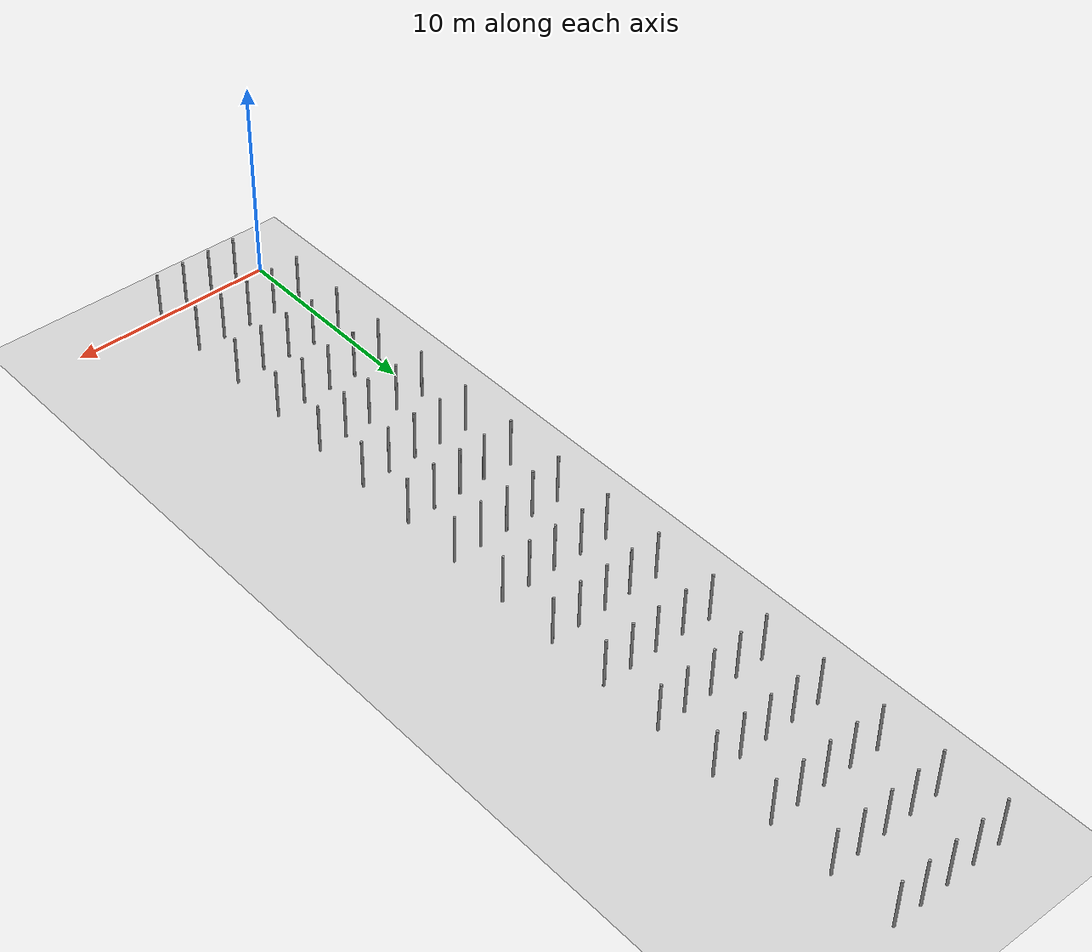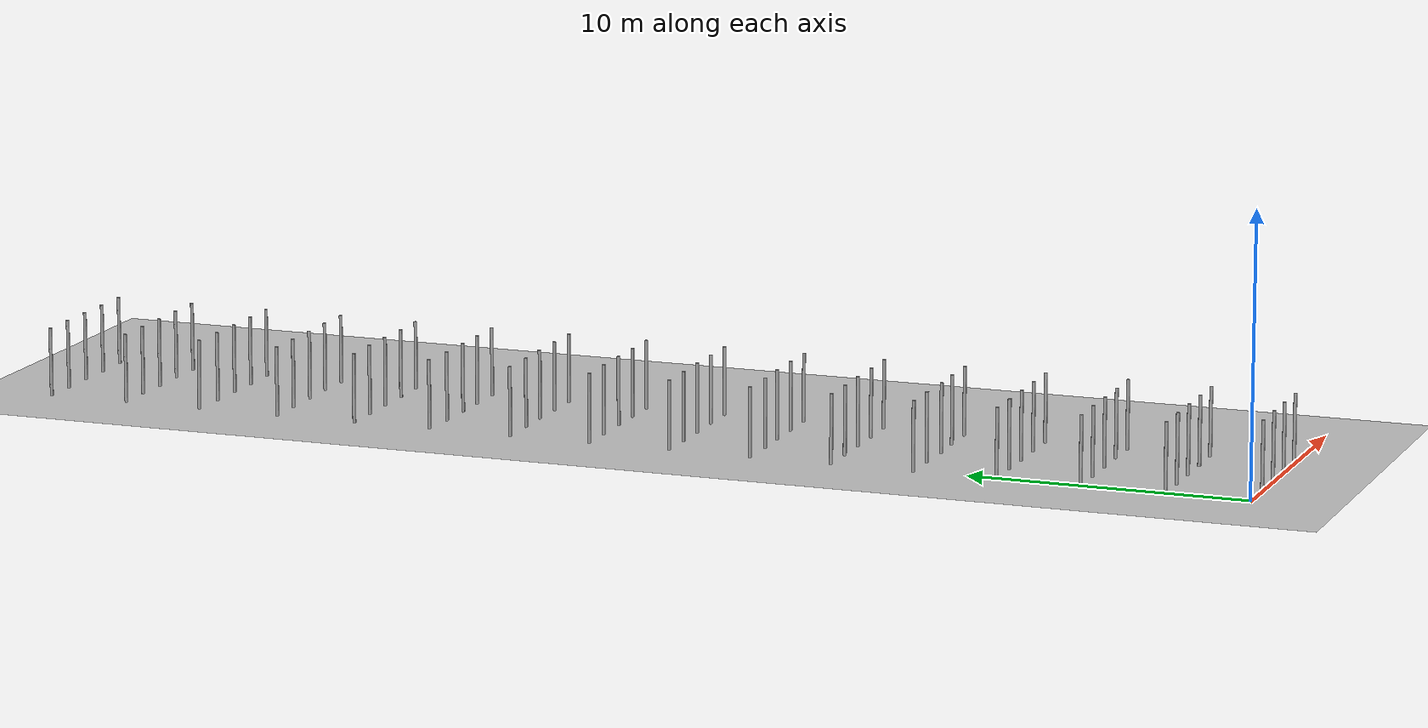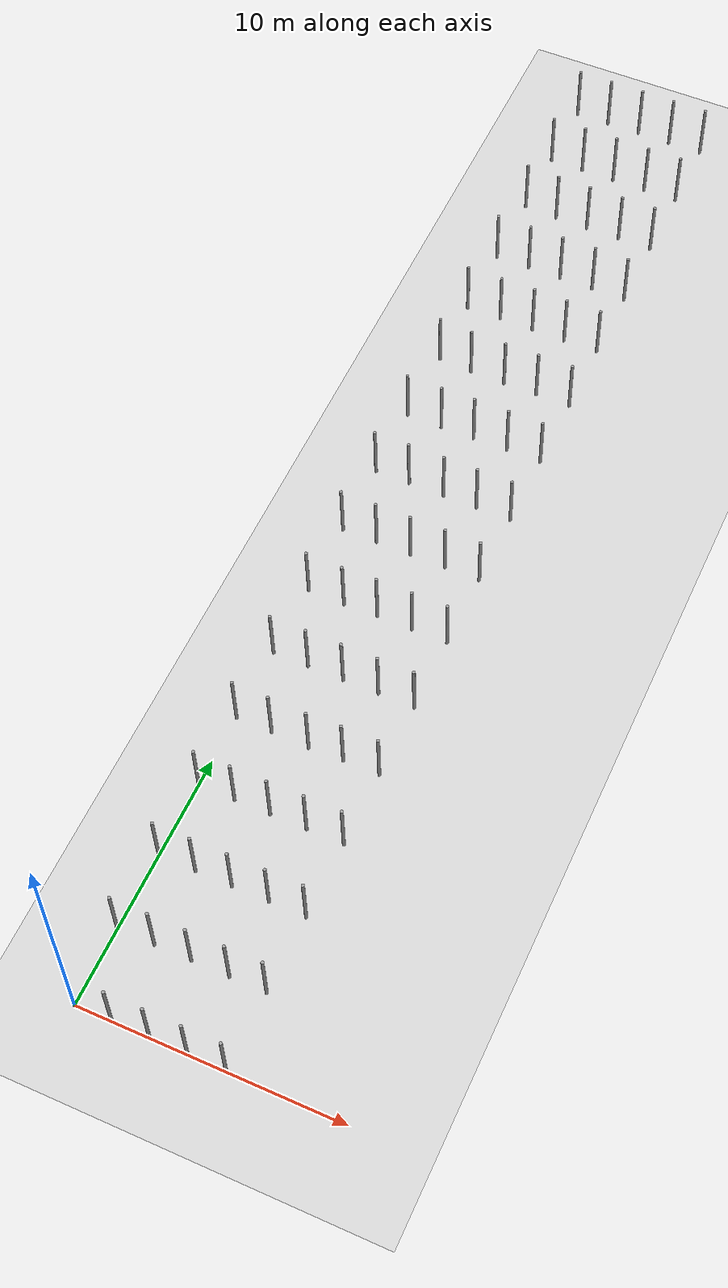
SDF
<sdf version="1.6">
 <world name="default">
  <light name="sun" type="directional">
   <pose>0 0 10 0 -0 0</pose>
   <diffuse>0.8 0.8 0.8 1</diffuse>
   <specular>0.1 0.1 0.1 1</specular>
   <attenuation>
    <range>1000</range>
    <constant>0.9</constant>
    <linear>0.01</linear>
    <quadratic>0.001</quadratic>
   </attenuation>
   <direction>-0.5 0.5 -1</direction>
  </light>
  <model name="ground_plane">
   <static>1</static>
   <link name="link">
    <collision name="collision">
     <geometry><plane><normal>0 0 1</normal><size>100 100</size></plane></geometry>
     <surface><friction><ode><mu>100</mu><mu2>50</mu2></ode></friction></surface>
    </collision>
    <visual name="visual">
     <cast_shadows>0</cast_shadows>
     <geometry><plane><normal>0 0 1</normal><size>100 100</size></plane></geometry>
     <material>
      <script><uri>file://media/materials/scripts/gazebo.material</uri><name>Gazebo/Grey</name></script>
     </material>
    </visual>
   </link>
  </model>
  <gravity>0 0 -9.8</gravity>
  <magnetic_field>6e-06 2.3e-05 -4.2e-05</magnetic_field>
  <atmosphere type="adiabatic"/>
  <physics name="default_physics" default="0" type="ode">
   <max_step_size>0.001</max_step_size>
   <real_time_factor>1</real_time_factor>
   <real_time_update_rate>1000</real_time_update_rate>
  </physics>
  <scene><ambient>0.4 0.4 0.4 1</ambient><background>0.7 0.7 0.7 1</background><shadows>1</shadows></scene>
  <spherical_coordinates>
   <surface_model>EARTH_WGS84</surface_model>
   <latitude_deg>0</latitude_deg>
   <longitude_deg>0</longitude_deg>
   <elevation>0</elevation>
   <heading_deg>0</heading_deg>
  </spherical_coordinates>
  <model name="pole_8">
   <link name="link_0">
    <inertial>
     <mass>0.0364582</mass>
     <inertia>
      <ixx>0.00312124</ixx>
      <ixy>0</ixy>
      <ixz>0</ixz>
      <iyy>0.00312124</iyy>
      <iyz>0</iyz>
      <izz>0.00016615</izz>
     </inertia>
    </inertial>
    <visual name="visual">
     <geometry><cylinder><radius>0.06</radius><length>2.5</length></cylinder></geometry>
     <material>
      <lighting>1</lighting>
      <script><uri>file://media/materials/scripts/gazebo.material</uri><name>Gazebo/Grey</name></script>
      <ambient>0.3 0.3 0.3 1</ambient>
      <diffuse>0.7 0.7 0.7 1</diffuse>
      <specular>0.01 0.01 0.01 1</specular>
      <emissive>0 0 0 1</emissive>
      <shader type="vertex"><normal_map>__default__</normal_map></shader>
     </material>
    </visual>
    <collision name="collision">
     <geometry><cylinder><radius>0.06</radius><length>2.5</length></cylinder></geometry>
     <surface>
      <friction>
       <ode><mu>1</mu><mu2>1</mu2><fdir1>0 0 0</fdir1><slip1>0</slip1><slip2>0</slip2></ode>
       <torsional>
        <coefficient>1</coefficient>
        <patch_radius>0</patch_radius>
        <surface_radius>0</surface_radius>
        <use_patch_radius>1</use_patch_radius>
        <ode><slip>0</slip></ode>
       </torsional>
      </friction>
      <bounce><restitution_coefficient>0</restitution_coefficient><threshold>1e+06</threshold></bounce>
      <contact>
       <collide_without_contact>0</collide_without_contact>
       <collide_without_contact_bitmask>1</collide_without_contact_bitmask>
       <collide_bitmask>1</collide_bitmask>
       <ode>
        <soft_cfm>0</soft_cfm>
        <soft_erp>0.2</soft_erp>
        <kp>1e+13</kp>
        <kd>1</kd>
        <max_vel>0.01</max_vel>
        <min_depth>0</min_depth>
       </ode>
       <bullet>
        <split_impulse>1</split_impulse>
        <split_impulse_penetration_threshold>-0.01</split_impulse_penetration_threshold>
        <soft_cfm>0</soft_cfm>
        <soft_erp>0.2</soft_erp>
        <kp>1e+13</kp>
        <kd>1</kd>
       </bullet>
      </contact>
     </surface>
    </collision>
   </link>
   <static>0</static>
   <pose>1.40457 0.004264 1.24999 0 -1e-06 -0.048179</pose>
  </model>
  <model name="pole_9">
   <link name="link_0">
    <inertial>
     <mass>0.0364582</mass>
     <inertia>
      <ixx>0.00312124</ixx>
      <ixy>0</ixy>
      <ixz>0</ixz>
      <iyy>0.00312124</iyy>
      <iyz>0</iyz>
      <izz>0.00016615</izz>
     </inertia>
    </inertial>
    <visual name="visual">
     <geometry><cylinder><radius>0.06</radius><length>2.5</length></cylinder></geometry>
     <material>
      <lighting>1</lighting>
      <script><uri>file://media/materials/scripts/gazebo.material</uri><name>Gazebo/Grey</name></script>
      <ambient>0.3 0.3 0.3 1</ambient>
      <diffuse>0.7 0.7 0.7 1</diffuse>
      <specular>0.01 0.01 0.01 1</specular>
      <emissive>0 0 0 1</emissive>
      <shader type="vertex"><normal_map>__default__</normal_map></shader>
     </material>
    </visual>
    <collision name="collision">
     <geometry><cylinder><radius>0.06</radius><length>2.5</length></cylinder></geometry>
     <surface>
      <friction>
       <ode><mu>1</mu><mu2>1</mu2><fdir1>0 0 0</fdir1><slip1>0</slip1><slip2>0</slip2></ode>
       <torsional>
        <coefficient>1</coefficient>
        <patch_radius>0</patch_radius>
        <surface_radius>0</surface_radius>
        <use_patch_radius>1</use_patch_radius>
        <ode><slip>0</slip></ode>
       </torsional>
      </friction>
      <bounce><restitution_coefficient>0</restitution_coefficient><threshold>1e+06</threshold></bounce>
      <contact>
       <collide_without_contact>0</collide_without_contact>
       <collide_without_contact_bitmask>1</collide_without_contact_bitmask>
       <collide_bitmask>1</collide_bitmask>
       <ode>
        <soft_cfm>0</soft_cfm>
        <soft_erp>0.2</soft_erp>
        <kp>1e+13</kp>
        <kd>1</kd>
        <max_vel>0.01</max_vel>
        <min_depth>0</min_depth>
       </ode>
       <bullet>
        <split_impulse>1</split_impulse>
        <split_impulse_penetration_threshold>-0.01</split_impulse_penetration_threshold>
        <soft_cfm>0</soft_cfm>
        <soft_erp>0.2</soft_erp>
        <kp>1e+13</kp>
        <kd>1</kd>
       </bullet>
      </contact>
     </surface>
    </collision>
   </link>
   <static>0</static>
   <pose>2.80839 0.00444 1.25 0 -1e-06 -0.064505</pose>
  </model>
  <model name="pole_10">
   <link name="link_0">
    <inertial>
     <mass>0.0364582</mass>
     <inertia>
      <ixx>0.00312124</ixx>
      <ixy>0</ixy>
      <ixz>0</ixz>
      <iyy>0.00312124</iyy>
      <iyz>0</iyz>
      <izz>0.00016615</izz>
     </inertia>
    </inertial>
    <visual name="visual">
     <geometry><cylinder><radius>0.06</radius><length>2.5</length></cylinder></geometry>
     <material>
      <lighting>1</lighting>
      <script><uri>file://media/materials/scripts/gazebo.material</uri><name>Gazebo/Grey</name></script>
      <ambient>0.3 0.3 0.3 1</ambient>
      <diffuse>0.7 0.7 0.7 1</diffuse>
      <specular>0.01 0.01 0.01 1</specular>
      <emissive>0 0 0 1</emissive>
      <shader type="vertex"><normal_map>__default__</normal_map></shader>
     </material>
    </visual>
    <collision name="collision">
     <geometry><cylinder><radius>0.06</radius><length>2.5</length></cylinder></geometry>
     <surface>
      <friction>
       <ode><mu>1</mu><mu2>1</mu2><fdir1>0 0 0</fdir1><slip1>0</slip1><slip2>0</slip2></ode>
       <torsional>
        <coefficient>1</coefficient>
        <patch_radius>0</patch_radius>
        <surface_radius>0</surface_radius>
        <use_patch_radius>1</use_patch_radius>
        <ode><slip>0</slip></ode>
       </torsional>
      </friction>
      <bounce><restitution_coefficient>0</restitution_coefficient><threshold>1e+06</threshold></bounce>
      <contact>
       <collide_without_contact>0</collide_without_contact>
       <collide_without_contact_bitmask>1</collide_without_contact_bitmask>
       <collide_bitmask>1</collide_bitmask>
       <ode>
        <soft_cfm>0</soft_cfm>
        <soft_erp>0.2</soft_erp>
        <kp>1e+13</kp>
        <kd>1</kd>
        <max_vel>0.01</max_vel>
        <min_depth>0</min_depth>
       </ode>
       <bullet>
        <split_impulse>1</split_impulse>
        <split_impulse_penetration_threshold>-0.01</split_impulse_penetration_threshold>
        <soft_cfm>0</soft_cfm>
        <soft_erp>0.2</soft_erp>
        <kp>1e+13</kp>
        <kd>1</kd>
       </bullet>
      </contact>
     </surface>
    </collision>
   </link>
   <static>0</static>
   <pose>4.20431 0.004243 1.24999 -1e-06 1e-06 -0.049195</pose>
  </model>
  <model name="pole_11">
   <link name="link_0">
    <inertial>
     <mass>0.0364582</mass>
     <inertia>
      <ixx>0.00312124</ixx>
      <ixy>0</ixy>
      <ixz>0</ixz>
      <iyy>0.00312124</iyy>
      <iyz>0</iyz>
      <izz>0.00016615</izz>
     </inertia>
    </inertial>
    <visual name="visual">
     <geometry><cylinder><radius>0.06</radius><length>2.5</length></cylinder></geometry>
     <material>
      <lighting>1</lighting>
      <script><uri>file://media/materials/scripts/gazebo.material</uri><name>Gazebo/Grey</name></script>
      <ambient>0.3 0.3 0.3 1</ambient>
      <diffuse>0.7 0.7 0.7 1</diffuse>
      <specular>0.01 0.01 0.01 1</specular>
      <emissive>0 0 0 1</emissive>
      <shader type="vertex"><normal_map>__default__</normal_map></shader>
     </material>
    </visual>
    <collision name="collision">
     <geometry><cylinder><radius>0.06</radius><length>2.5</length></cylinder></geometry>
     <surface>
      <friction>
       <ode><mu>1</mu><mu2>1</mu2><fdir1>0 0 0</fdir1><slip1>0</slip1><slip2>0</slip2></ode>
       <torsional>
        <coefficient>1</coefficient>
        <patch_radius>0</patch_radius>
        <surface_radius>0</surface_radius>
        <use_patch_radius>1</use_patch_radius>
        <ode><slip>0</slip></ode>
       </torsional>
      </friction>
      <bounce><restitution_coefficient>0</restitution_coefficient><threshold>1e+06</threshold></bounce>
      <contact>
       <collide_without_contact>0</collide_without_contact>
       <collide_without_contact_bitmask>1</collide_without_contact_bitmask>
       <collide_bitmask>1</collide_bitmask>
       <ode>
        <soft_cfm>0</soft_cfm>
        <soft_erp>0.2</soft_erp>
        <kp>1e+13</kp>
        <kd>1</kd>
        <max_vel>0.01</max_vel>
        <min_depth>0</min_depth>
       </ode>
       <bullet>
        <split_impulse>1</split_impulse>
        <split_impulse_penetration_threshold>-0.01</split_impulse_penetration_threshold>
        <soft_cfm>0</soft_cfm>
        <soft_erp>0.2</soft_erp>
        <kp>1e+13</kp>
        <kd>1</kd>
       </bullet>
      </contact>
     </surface>
    </collision>
   </link>
   <static>0</static>
   <pose>5.61661 0.003918 1.24999 0 -1e-06 -0.050677</pose>
  </model>
  <model name="pole_11_clone">
   <link name="link_0">
    <inertial>
     <mass>0.0364582</mass>
     <inertia>
      <ixx>0.00312124</ixx>
      <ixy>0</ixy>
      <ixz>0</ixz>
      <iyy>0.00312124</iyy>
      <iyz>0</iyz>
      <izz>0.00016615</izz>
     </inertia>
    </inertial>
    <visual name="visual">
     <geometry><cylinder><radius>0.06</radius><length>2.5</length></cylinder></geometry>
     <material>
      <lighting>1</lighting>
      <script><uri>file://media/materials/scripts/gazebo.material</uri><name>Gazebo/Grey</name></script>
      <ambient>0.3 0.3 0.3 1</ambient>
      <diffuse>0.7 0.7 0.7 1</diffuse>
      <specular>0.01 0.01 0.01 1</specular>
      <emissive>0 0 0 1</emissive>
      <shader type="vertex"><normal_map>__default__</normal_map></shader>
     </material>
    </visual>
    <collision name="collision">
     <geometry><cylinder><radius>0.06</radius><length>2.5</length></cylinder></geometry>
     <surface>
      <friction>
       <ode><mu>1</mu><mu2>1</mu2><fdir1>0 0 0</fdir1><slip1>0</slip1><slip2>0</slip2></ode>
       <torsional>
        <coefficient>1</coefficient>
        <patch_radius>0</patch_radius>
        <surface_radius>0</surface_radius>
        <use_patch_radius>1</use_patch_radius>
        <ode><slip>0</slip></ode>
       </torsional>
      </friction>
      <bounce><restitution_coefficient>0</restitution_coefficient><threshold>1e+06</threshold></bounce>
      <contact>
       <collide_without_contact>0</collide_without_contact>
       <collide_without_contact_bitmask>1</collide_without_contact_bitmask>
       <collide_bitmask>1</collide_bitmask>
       <ode>
        <soft_cfm>0</soft_cfm>
        <soft_erp>0.2</soft_erp>
        <kp>1e+13</kp>
        <kd>1</kd>
        <max_vel>0.01</max_vel>
        <min_depth>0</min_depth>
       </ode>
       <bullet>
        <split_impulse>1</split_impulse>
        <split_impulse_penetration_threshold>-0.01</split_impulse_penetration_threshold>
        <soft_cfm>0</soft_cfm>
        <soft_erp>0.2</soft_erp>
        <kp>1e+13</kp>
        <kd>1</kd>
       </bullet>
      </contact>
     </surface>
    </collision>
   </link>
   <static>0</static>
   <pose>0.000573 2.98414 1.25 -0 1e-06 -0.046742</pose>
  </model>
  <model name="pole">
   <link name="link_0">
    <inertial>
     <mass>0.0364582</mass>
     <inertia>
      <ixx>0.00312124</ixx>
      <ixy>0</ixy>
      <ixz>0</ixz>
      <iyy>0.00312124</iyy>
      <iyz>0</iyz>
      <izz>0.00016615</izz>
     </inertia>
    </inertial>
    <visual name="visual">
     <geometry><cylinder><radius>0.06</radius><length>2.5</length></cylinder></geometry>
     <material>
      <lighting>1</lighting>
      <script><uri>file://media/materials/scripts/gazebo.material</uri><name>Gazebo/Grey</name></script>
      <ambient>0.3 0.3 0.3 1</ambient>
      <diffuse>0.7 0.7 0.7 1</diffuse>
      <specular>0.01 0.01 0.01 1</specular>
      <emissive>0 0 0 1</emissive>
      <shader type="vertex"><normal_map>__default__</normal_map></shader>
     </material>
    </visual>
    <collision name="collision">
     <geometry><cylinder><radius>0.06</radius><length>2.5</length></cylinder></geometry>
     <surface>
      <friction>
       <ode><mu>1</mu><mu2>1</mu2><fdir1>0 0 0</fdir1><slip1>0</slip1><slip2>0</slip2></ode>
       <torsional>
        <coefficient>1</coefficient>
        <patch_radius>0</patch_radius>
        <surface_radius>0</surface_radius>
        <use_patch_radius>1</use_patch_radius>
        <ode><slip>0</slip></ode>
       </torsional>
      </friction>
      <bounce><restitution_coefficient>0</restitution_coefficient><threshold>1e+06</threshold></bounce>
      <contact>
       <collide_without_contact>0</collide_without_contact>
       <collide_without_contact_bitmask>1</collide_without_contact_bitmask>
       <collide_bitmask>1</collide_bitmask>
       <ode>
        <soft_cfm>0</soft_cfm>
        <soft_erp>0.2</soft_erp>
        <kp>1e+13</kp>
        <kd>1</kd>
        <max_vel>0.01</max_vel>
        <min_depth>0</min_depth>
       </ode>
       <bullet>
        <split_impulse>1</split_impulse>
        <split_impulse_penetration_threshold>-0.01</split_impulse_penetration_threshold>
        <soft_cfm>0</soft_cfm>
        <soft_erp>0.2</soft_erp>
        <kp>1e+13</kp>
        <kd>1</kd>
       </bullet>
      </contact>
     </surface>
    </collision>
   </link>
   <static>0</static>
   <pose>0.007094 5.96374 1.24999 0 -1e-06 -0.04613</pose>
  </model>
  <model name="pole_0">
   <link name="link_0">
    <inertial>
     <mass>0.0364582</mass>
     <inertia>
      <ixx>0.00312124</ixx>
      <ixy>0</ixy>
      <ixz>0</ixz>
      <iyy>0.00312124</iyy>
      <iyz>0</iyz>
      <izz>0.00016615</izz>
     </inertia>
    </inertial>
    <visual name="visual">
     <geometry><cylinder><radius>0.06</radius><length>2.5</length></cylinder></geometry>
     <material>
      <lighting>1</lighting>
      <script><uri>file://media/materials/scripts/gazebo.material</uri><name>Gazebo/Grey</name></script>
      <ambient>0.3 0.3 0.3 1</ambient>
      <diffuse>0.7 0.7 0.7 1</diffuse>
      <specular>0.01 0.01 0.01 1</specular>
      <emissive>0 0 0 1</emissive>
      <shader type="vertex"><normal_map>__default__</normal_map></shader>
     </material>
    </visual>
    <collision name="collision">
     <geometry><cylinder><radius>0.06</radius><length>2.5</length></cylinder></geometry>
     <surface>
      <friction>
       <ode><mu>1</mu><mu2>1</mu2><fdir1>0 0 0</fdir1><slip1>0</slip1><slip2>0</slip2></ode>
       <torsional>
        <coefficient>1</coefficient>
        <patch_radius>0</patch_radius>
        <surface_radius>0</surface_radius>
        <use_patch_radius>1</use_patch_radius>
        <ode><slip>0</slip></ode>
       </torsional>
      </friction>
      <bounce><restitution_coefficient>0</restitution_coefficient><threshold>1e+06</threshold></bounce>
      <contact>
       <collide_without_contact>0</collide_without_contact>
       <collide_without_contact_bitmask>1</collide_without_contact_bitmask>
       <collide_bitmask>1</collide_bitmask>
       <ode>
        <soft_cfm>0</soft_cfm>
        <soft_erp>0.2</soft_erp>
        <kp>1e+13</kp>
        <kd>1</kd>
        <max_vel>0.01</max_vel>
        <min_depth>0</min_depth>
       </ode>
       <bullet>
        <split_impulse>1</split_impulse>
        <split_impulse_penetration_threshold>-0.01</split_impulse_penetration_threshold>
        <soft_cfm>0</soft_cfm>
        <soft_erp>0.2</soft_erp>
        <kp>1e+13</kp>
        <kd>1</kd>
       </bullet>
      </contact>
     </surface>
    </collision>
   </link>
   <static>0</static>
   <pose>0.013875 8.94382 1.24999 0 1e-06 -0.045325</pose>
  </model>
  <model name="pole_1">
   <link name="link_0">
    <inertial>
     <mass>0.0364582</mass>
     <inertia>
      <ixx>0.00312124</ixx>
      <ixy>0</ixy>
      <ixz>0</ixz>
      <iyy>0.00312124</iyy>
      <iyz>0</iyz>
      <izz>0.00016615</izz>
     </inertia>
    </inertial>
    <visual name="visual">
     <geometry><cylinder><radius>0.06</radius><length>2.5</length></cylinder></geometry>
     <material>
      <lighting>1</lighting>
      <script><uri>file://media/materials/scripts/gazebo.material</uri><name>Gazebo/Grey</name></script>
      <ambient>0.3 0.3 0.3 1</ambient>
      <diffuse>0.7 0.7 0.7 1</diffuse>
      <specular>0.01 0.01 0.01 1</specular>
      <emissive>0 0 0 1</emissive>
      <shader type="vertex"><normal_map>__default__</normal_map></shader>
     </material>
    </visual>
    <collision name="collision">
     <geometry><cylinder><radius>0.06</radius><length>2.5</length></cylinder></geometry>
     <surface>
      <friction>
       <ode><mu>1</mu><mu2>1</mu2><fdir1>0 0 0</fdir1><slip1>0</slip1><slip2>0</slip2></ode>
       <torsional>
        <coefficient>1</coefficient>
        <patch_radius>0</patch_radius>
        <surface_radius>0</surface_radius>
        <use_patch_radius>1</use_patch_radius>
        <ode><slip>0</slip></ode>
       </torsional>
      </friction>
      <bounce><restitution_coefficient>0</restitution_coefficient><threshold>1e+06</threshold></bounce>
      <contact>
       <collide_without_contact>0</collide_without_contact>
       <collide_without_contact_bitmask>1</collide_without_contact_bitmask>
       <collide_bitmask>1</collide_bitmask>
       <ode>
        <soft_cfm>0</soft_cfm>
        <soft_erp>0.2</soft_erp>
        <kp>1e+13</kp>
        <kd>1</kd>
        <max_vel>0.01</max_vel>
        <min_depth>0</min_depth>
       </ode>
       <bullet>
        <split_impulse>1</split_impulse>
        <split_impulse_penetration_threshold>-0.01</split_impulse_penetration_threshold>
        <soft_cfm>0</soft_cfm>
        <soft_erp>0.2</soft_erp>
        <kp>1e+13</kp>
        <kd>1</kd>
       </bullet>
      </contact>
     </surface>
    </collision>
   </link>
   <static>0</static>
   <pose>-0.007707 11.9242 1.24999 -0 1e-06 -0.04844</pose>
  </model>
  <model name="pole_2">
   <link name="link_0">
    <inertial>
     <mass>0.0364582</mass>
     <inertia>
      <ixx>0.00312124</ixx>
      <ixy>0</ixy>
      <ixz>0</ixz>
      <iyy>0.00312124</iyy>
      <iyz>0</iyz>
      <izz>0.00016615</izz>
     </inertia>
    </inertial>
    <visual name="visual">
     <geometry><cylinder><radius>0.06</radius><length>2.5</length></cylinder></geometry>
     <material>
      <lighting>1</lighting>
      <script><uri>file://media/materials/scripts/gazebo.material</uri><name>Gazebo/Grey</name></script>
      <ambient>0.3 0.3 0.3 1</ambient>
      <diffuse>0.7 0.7 0.7 1</diffuse>
      <specular>0.01 0.01 0.01 1</specular>
      <emissive>0 0 0 1</emissive>
      <shader type="vertex"><normal_map>__default__</normal_map></shader>
     </material>
    </visual>
    <collision name="collision">
     <geometry><cylinder><radius>0.06</radius><length>2.5</length></cylinder></geometry>
     <surface>
      <friction>
       <ode><mu>1</mu><mu2>1</mu2><fdir1>0 0 0</fdir1><slip1>0</slip1><slip2>0</slip2></ode>
       <torsional>
        <coefficient>1</coefficient>
        <patch_radius>0</patch_radius>
        <surface_radius>0</surface_radius>
        <use_patch_radius>1</use_patch_radius>
        <ode><slip>0</slip></ode>
       </torsional>
      </friction>
      <bounce><restitution_coefficient>0</restitution_coefficient><threshold>1e+06</threshold></bounce>
      <contact>
       <collide_without_contact>0</collide_without_contact>
       <collide_without_contact_bitmask>1</collide_without_contact_bitmask>
       <collide_bitmask>1</collide_bitmask>
       <ode>
        <soft_cfm>0</soft_cfm>
        <soft_erp>0.2</soft_erp>
        <kp>1e+13</kp>
        <kd>1</kd>
        <max_vel>0.01</max_vel>
        <min_depth>0</min_depth>
       </ode>
       <bullet>
        <split_impulse>1</split_impulse>
        <split_impulse_penetration_threshold>-0.01</split_impulse_penetration_threshold>
        <soft_cfm>0</soft_cfm>
        <soft_erp>0.2</soft_erp>
        <kp>1e+13</kp>
        <kd>1</kd>
       </bullet>
      </contact>
     </surface>
    </collision>
   </link>
   <static>0</static>
   <pose>0.000392 14.8969 1.24999 0 1e-06 0.189233</pose>
  </model>
  <model name="pole_3">
   <link name="link_0">
    <inertial>
     <mass>0.0364582</mass>
     <inertia>
      <ixx>0.00312124</ixx>
      <ixy>0</ixy>
      <ixz>0</ixz>
      <iyy>0.00312124</iyy>
      <iyz>0</iyz>
      <izz>0.00016615</izz>
     </inertia>
    </inertial>
    <visual name="visual">
     <geometry><cylinder><radius>0.06</radius><length>2.5</length></cylinder></geometry>
     <material>
      <lighting>1</lighting>
      <script><uri>file://media/materials/scripts/gazebo.material</uri><name>Gazebo/Grey</name></script>
      <ambient>0.3 0.3 0.3 1</ambient>
      <diffuse>0.7 0.7 0.7 1</diffuse>
      <specular>0.01 0.01 0.01 1</specular>
      <emissive>0 0 0 1</emissive>
      <shader type="vertex"><normal_map>__default__</normal_map></shader>
     </material>
    </visual>
    <collision name="collision">
     <geometry><cylinder><radius>0.06</radius><length>2.5</length></cylinder></geometry>
     <surface>
      <friction>
       <ode><mu>1</mu><mu2>1</mu2><fdir1>0 0 0</fdir1><slip1>0</slip1><slip2>0</slip2></ode>
       <torsional>
        <coefficient>1</coefficient>
        <patch_radius>0</patch_radius>
        <surface_radius>0</surface_radius>
        <use_patch_radius>1</use_patch_radius>
        <ode><slip>0</slip></ode>
       </torsional>
      </friction>
      <bounce><restitution_coefficient>0</restitution_coefficient><threshold>1e+06</threshold></bounce>
      <contact>
       <collide_without_contact>0</collide_without_contact>
       <collide_without_contact_bitmask>1</collide_without_contact_bitmask>
       <collide_bitmask>1</collide_bitmask>
       <ode>
        <soft_cfm>0</soft_cfm>
        <soft_erp>0.2</soft_erp>
        <kp>1e+13</kp>
        <kd>1</kd>
        <max_vel>0.01</max_vel>
        <min_depth>0</min_depth>
       </ode>
       <bullet>
        <split_impulse>1</split_impulse>
        <split_impulse_penetration_threshold>-0.01</split_impulse_penetration_threshold>
        <soft_cfm>0</soft_cfm>
        <soft_erp>0.2</soft_erp>
        <kp>1e+13</kp>
        <kd>1</kd>
       </bullet>
      </contact>
     </surface>
    </collision>
   </link>
   <static>0</static>
   <pose>1.40508 2.9838 1.25 -1e-06 1e-06 -0.042412</pose>
  </model>
  <model name="pole_5">
   <link name="link_0">
    <inertial>
     <mass>0.0364582</mass>
     <inertia>
      <ixx>0.00312124</ixx>
      <ixy>0</ixy>
      <ixz>0</ixz>
      <iyy>0.00312124</iyy>
      <iyz>0</iyz>
      <izz>0.00016615</izz>
     </inertia>
    </inertial>
    <visual name="visual">
     <geometry><cylinder><radius>0.06</radius><length>2.5</length></cylinder></geometry>
     <material>
      <lighting>1</lighting>
      <script><uri>file://media/materials/scripts/gazebo.material</uri><name>Gazebo/Grey</name></script>
      <ambient>0.3 0.3 0.3 1</ambient>
      <diffuse>0.7 0.7 0.7 1</diffuse>
      <specular>0.01 0.01 0.01 1</specular>
      <emissive>0 0 0 1</emissive>
      <shader type="vertex"><normal_map>__default__</normal_map></shader>
     </material>
    </visual>
    <collision name="collision">
     <geometry><cylinder><radius>0.06</radius><length>2.5</length></cylinder></geometry>
     <surface>
      <friction>
       <ode><mu>1</mu><mu2>1</mu2><fdir1>0 0 0</fdir1><slip1>0</slip1><slip2>0</slip2></ode>
       <torsional>
        <coefficient>1</coefficient>
        <patch_radius>0</patch_radius>
        <surface_radius>0</surface_radius>
        <use_patch_radius>1</use_patch_radius>
        <ode><slip>0</slip></ode>
       </torsional>
      </friction>
      <bounce><restitution_coefficient>0</restitution_coefficient><threshold>1e+06</threshold></bounce>
      <contact>
       <collide_without_contact>0</collide_without_contact>
       <collide_without_contact_bitmask>1</collide_without_contact_bitmask>
       <collide_bitmask>1</collide_bitmask>
       <ode>
        <soft_cfm>0</soft_cfm>
        <soft_erp>0.2</soft_erp>
        <kp>1e+13</kp>
        <kd>1</kd>
        <max_vel>0.01</max_vel>
        <min_depth>0</min_depth>
       </ode>
       <bullet>
        <split_impulse>1</split_impulse>
        <split_impulse_penetration_threshold>-0.01</split_impulse_penetration_threshold>
        <soft_cfm>0</soft_cfm>
        <soft_erp>0.2</soft_erp>
        <kp>1e+13</kp>
        <kd>1</kd>
       </bullet>
      </contact>
     </surface>
    </collision>
   </link>
   <static>0</static>
   <pose>2.79619 2.98388 1.25 -1e-06 1e-06 -0.042405</pose>
  </model>
  <model name="pole_6">
   <link name="link_0">
    <inertial>
     <mass>0.0364582</mass>
     <inertia>
      <ixx>0.00312124</ixx>
      <ixy>0</ixy>
      <ixz>0</ixz>
      <iyy>0.00312124</iyy>
      <iyz>0</iyz>
      <izz>0.00016615</izz>
     </inertia>
    </inertial>
    <visual name="visual">
     <geometry><cylinder><radius>0.06</radius><length>2.5</length></cylinder></geometry>
     <material>
      <lighting>1</lighting>
      <script><uri>file://media/materials/scripts/gazebo.material</uri><name>Gazebo/Grey</name></script>
      <ambient>0.3 0.3 0.3 1</ambient>
      <diffuse>0.7 0.7 0.7 1</diffuse>
      <specular>0.01 0.01 0.01 1</specular>
      <emissive>0 0 0 1</emissive>
      <shader type="vertex"><normal_map>__default__</normal_map></shader>
     </material>
    </visual>
    <collision name="collision">
     <geometry><cylinder><radius>0.06</radius><length>2.5</length></cylinder></geometry>
     <surface>
      <friction>
       <ode><mu>1</mu><mu2>1</mu2><fdir1>0 0 0</fdir1><slip1>0</slip1><slip2>0</slip2></ode>
       <torsional>
        <coefficient>1</coefficient>
        <patch_radius>0</patch_radius>
        <surface_radius>0</surface_radius>
        <use_patch_radius>1</use_patch_radius>
        <ode><slip>0</slip></ode>
       </torsional>
      </friction>
      <bounce><restitution_coefficient>0</restitution_coefficient><threshold>1e+06</threshold></bounce>
      <contact>
       <collide_without_contact>0</collide_without_contact>
       <collide_without_contact_bitmask>1</collide_without_contact_bitmask>
       <collide_bitmask>1</collide_bitmask>
       <ode>
        <soft_cfm>0</soft_cfm>
        <soft_erp>0.2</soft_erp>
        <kp>1e+13</kp>
        <kd>1</kd>
        <max_vel>0.01</max_vel>
        <min_depth>0</min_depth>
       </ode>
       <bullet>
        <split_impulse>1</split_impulse>
        <split_impulse_penetration_threshold>-0.01</split_impulse_penetration_threshold>
        <soft_cfm>0</soft_cfm>
        <soft_erp>0.2</soft_erp>
        <kp>1e+13</kp>
        <kd>1</kd>
       </bullet>
      </contact>
     </surface>
    </collision>
   </link>
   <static>0</static>
   <pose>4.22276 2.98391 1.25 -1e-06 -0 -0.042741</pose>
  </model>
  <model name="pole_7">
   <link name="link_0">
    <inertial>
     <mass>0.0364582</mass>
     <inertia>
      <ixx>0.00312124</ixx>
      <ixy>0</ixy>
      <ixz>0</ixz>
      <iyy>0.00312124</iyy>
      <iyz>0</iyz>
      <izz>0.00016615</izz>
     </inertia>
    </inertial>
    <visual name="visual">
     <geometry><cylinder><radius>0.06</radius><length>2.5</length></cylinder></geometry>
     <material>
      <lighting>1</lighting>
      <script><uri>file://media/materials/scripts/gazebo.material</uri><name>Gazebo/Grey</name></script>
      <ambient>0.3 0.3 0.3 1</ambient>
      <diffuse>0.7 0.7 0.7 1</diffuse>
      <specular>0.01 0.01 0.01 1</specular>
      <emissive>0 0 0 1</emissive>
      <shader type="vertex"><normal_map>__default__</normal_map></shader>
     </material>
    </visual>
    <collision name="collision">
     <geometry><cylinder><radius>0.06</radius><length>2.5</length></cylinder></geometry>
     <surface>
      <friction>
       <ode><mu>1</mu><mu2>1</mu2><fdir1>0 0 0</fdir1><slip1>0</slip1><slip2>0</slip2></ode>
       <torsional>
        <coefficient>1</coefficient>
        <patch_radius>0</patch_radius>
        <surface_radius>0</surface_radius>
        <use_patch_radius>1</use_patch_radius>
        <ode><slip>0</slip></ode>
       </torsional>
      </friction>
      <bounce><restitution_coefficient>0</restitution_coefficient><threshold>1e+06</threshold></bounce>
      <contact>
       <collide_without_contact>0</collide_without_contact>
       <collide_without_contact_bitmask>1</collide_without_contact_bitmask>
       <collide_bitmask>1</collide_bitmask>
       <ode>
        <soft_cfm>0</soft_cfm>
        <soft_erp>0.2</soft_erp>
        <kp>1e+13</kp>
        <kd>1</kd>
        <max_vel>0.01</max_vel>
        <min_depth>0</min_depth>
       </ode>
       <bullet>
        <split_impulse>1</split_impulse>
        <split_impulse_penetration_threshold>-0.01</split_impulse_penetration_threshold>
        <soft_cfm>0</soft_cfm>
        <soft_erp>0.2</soft_erp>
        <kp>1e+13</kp>
        <kd>1</kd>
       </bullet>
      </contact>
     </surface>
    </collision>
   </link>
   <static>0</static>
   <pose>5.60767 2.98395 1.24999 -1e-06 -2e-06 -0.039307</pose>
  </model>
  <model name="pole_12">
   <link name="link_0">
    <inertial>
     <mass>0.0364582</mass>
     <inertia>
      <ixx>0.00312124</ixx>
      <ixy>0</ixy>
      <ixz>0</ixz>
      <iyy>0.00312124</iyy>
      <iyz>0</iyz>
      <izz>0.00016615</izz>
     </inertia>
    </inertial>
    <visual name="visual">
     <geometry><cylinder><radius>0.06</radius><length>2.5</length></cylinder></geometry>
     <material>
      <lighting>1</lighting>
      <script><uri>file://media/materials/scripts/gazebo.material</uri><name>Gazebo/Grey</name></script>
      <ambient>0.3 0.3 0.3 1</ambient>
      <diffuse>0.7 0.7 0.7 1</diffuse>
      <specular>0.01 0.01 0.01 1</specular>
      <emissive>0 0 0 1</emissive>
      <shader type="vertex"><normal_map>__default__</normal_map></shader>
     </material>
    </visual>
    <collision name="collision">
     <geometry><cylinder><radius>0.06</radius><length>2.5</length></cylinder></geometry>
     <surface>
      <friction>
       <ode><mu>1</mu><mu2>1</mu2><fdir1>0 0 0</fdir1><slip1>0</slip1><slip2>0</slip2></ode>
       <torsional>
        <coefficient>1</coefficient>
        <patch_radius>0</patch_radius>
        <surface_radius>0</surface_radius>
        <use_patch_radius>1</use_patch_radius>
        <ode><slip>0</slip></ode>
       </torsional>
      </friction>
      <bounce><restitution_coefficient>0</restitution_coefficient><threshold>1e+06</threshold></bounce>
      <contact>
       <collide_without_contact>0</collide_without_contact>
       <collide_without_contact_bitmask>1</collide_without_contact_bitmask>
       <collide_bitmask>1</collide_bitmask>
       <ode>
        <soft_cfm>0</soft_cfm>
        <soft_erp>0.2</soft_erp>
        <kp>1e+13</kp>
        <kd>1</kd>
        <max_vel>0.01</max_vel>
        <min_depth>0</min_depth>
       </ode>
       <bullet>
        <split_impulse>1</split_impulse>
        <split_impulse_penetration_threshold>-0.01</split_impulse_penetration_threshold>
        <soft_cfm>0</soft_cfm>
        <soft_erp>0.2</soft_erp>
        <kp>1e+13</kp>
        <kd>1</kd>
       </bullet>
      </contact>
     </surface>
    </collision>
   </link>
   <static>0</static>
   <pose>1.41393 5.9636 1.25 -1e-06 -0 -0.03918</pose>
  </model>
  <model name="pole_13">
   <link name="link_0">
    <inertial>
     <mass>0.0364582</mass>
     <inertia>
      <ixx>0.00312124</ixx>
      <ixy>0</ixy>
      <ixz>0</ixz>
      <iyy>0.00312124</iyy>
      <iyz>0</iyz>
      <izz>0.00016615</izz>
     </inertia>
    </inertial>
    <visual name="visual">
     <geometry><cylinder><radius>0.06</radius><length>2.5</length></cylinder></geometry>
     <material>
      <lighting>1</lighting>
      <script><uri>file://media/materials/scripts/gazebo.material</uri><name>Gazebo/Grey</name></script>
      <ambient>0.3 0.3 0.3 1</ambient>
      <diffuse>0.7 0.7 0.7 1</diffuse>
      <specular>0.01 0.01 0.01 1</specular>
      <emissive>0 0 0 1</emissive>
      <shader type="vertex"><normal_map>__default__</normal_map></shader>
     </material>
    </visual>
    <collision name="collision">
     <geometry><cylinder><radius>0.06</radius><length>2.5</length></cylinder></geometry>
     <surface>
      <friction>
       <ode><mu>1</mu><mu2>1</mu2><fdir1>0 0 0</fdir1><slip1>0</slip1><slip2>0</slip2></ode>
       <torsional>
        <coefficient>1</coefficient>
        <patch_radius>0</patch_radius>
        <surface_radius>0</surface_radius>
        <use_patch_radius>1</use_patch_radius>
        <ode><slip>0</slip></ode>
       </torsional>
      </friction>
      <bounce><restitution_coefficient>0</restitution_coefficient><threshold>1e+06</threshold></bounce>
      <contact>
       <collide_without_contact>0</collide_without_contact>
       <collide_without_contact_bitmask>1</collide_without_contact_bitmask>
       <collide_bitmask>1</collide_bitmask>
       <ode>
        <soft_cfm>0</soft_cfm>
        <soft_erp>0.2</soft_erp>
        <kp>1e+13</kp>
        <kd>1</kd>
        <max_vel>0.01</max_vel>
        <min_depth>0</min_depth>
       </ode>
       <bullet>
        <split_impulse>1</split_impulse>
        <split_impulse_penetration_threshold>-0.01</split_impulse_penetration_threshold>
        <soft_cfm>0</soft_cfm>
        <soft_erp>0.2</soft_erp>
        <kp>1e+13</kp>
        <kd>1</kd>
       </bullet>
      </contact>
     </surface>
    </collision>
   </link>
   <static>0</static>
   <pose>2.80842 5.96412 1.25 -1e-06 1e-06 -0.039661</pose>
  </model>
  <model name="pole_14">
   <link name="link_0">
    <inertial>
     <mass>0.0364582</mass>
     <inertia>
      <ixx>0.00312124</ixx>
      <ixy>0</ixy>
      <ixz>0</ixz>
      <iyy>0.00312124</iyy>
      <iyz>0</iyz>
      <izz>0.00016615</izz>
     </inertia>
    </inertial>
    <visual name="visual">
     <geometry><cylinder><radius>0.06</radius><length>2.5</length></cylinder></geometry>
     <material>
      <lighting>1</lighting>
      <script><uri>file://media/materials/scripts/gazebo.material</uri><name>Gazebo/Grey</name></script>
      <ambient>0.3 0.3 0.3 1</ambient>
      <diffuse>0.7 0.7 0.7 1</diffuse>
      <specular>0.01 0.01 0.01 1</specular>
      <emissive>0 0 0 1</emissive>
      <shader type="vertex"><normal_map>__default__</normal_map></shader>
     </material>
    </visual>
    <collision name="collision">
     <geometry><cylinder><radius>0.06</radius><length>2.5</length></cylinder></geometry>
     <surface>
      <friction>
       <ode><mu>1</mu><mu2>1</mu2><fdir1>0 0 0</fdir1><slip1>0</slip1><slip2>0</slip2></ode>
       <torsional>
        <coefficient>1</coefficient>
        <patch_radius>0</patch_radius>
        <surface_radius>0</surface_radius>
        <use_patch_radius>1</use_patch_radius>
        <ode><slip>0</slip></ode>
       </torsional>
      </friction>
      <bounce><restitution_coefficient>0</restitution_coefficient><threshold>1e+06</threshold></bounce>
      <contact>
       <collide_without_contact>0</collide_without_contact>
       <collide_without_contact_bitmask>1</collide_without_contact_bitmask>
       <collide_bitmask>1</collide_bitmask>
       <ode>
        <soft_cfm>0</soft_cfm>
        <soft_erp>0.2</soft_erp>
        <kp>1e+13</kp>
        <kd>1</kd>
        <max_vel>0.01</max_vel>
        <min_depth>0</min_depth>
       </ode>
       <bullet>
        <split_impulse>1</split_impulse>
        <split_impulse_penetration_threshold>-0.01</split_impulse_penetration_threshold>
        <soft_cfm>0</soft_cfm>
        <soft_erp>0.2</soft_erp>
        <kp>1e+13</kp>
        <kd>1</kd>
       </bullet>
      </contact>
     </surface>
    </collision>
   </link>
   <static>0</static>
   <pose>4.21992 5.96373 1.24999 1e-06 -1e-06 -0.040184</pose>
  </model>
  <model name="pole_15">
   <link name="link_0">
    <inertial>
     <mass>0.0364582</mass>
     <inertia>
      <ixx>0.00312124</ixx>
      <ixy>0</ixy>
      <ixz>0</ixz>
      <iyy>0.00312124</iyy>
      <iyz>0</iyz>
      <izz>0.00016615</izz>
     </inertia>
    </inertial>
    <visual name="visual">
     <geometry><cylinder><radius>0.06</radius><length>2.5</length></cylinder></geometry>
     <material>
      <lighting>1</lighting>
      <script><uri>file://media/materials/scripts/gazebo.material</uri><name>Gazebo/Grey</name></script>
      <ambient>0.3 0.3 0.3 1</ambient>
      <diffuse>0.7 0.7 0.7 1</diffuse>
      <specular>0.01 0.01 0.01 1</specular>
      <emissive>0 0 0 1</emissive>
      <shader type="vertex"><normal_map>__default__</normal_map></shader>
     </material>
    </visual>
    <collision name="collision">
     <geometry><cylinder><radius>0.06</radius><length>2.5</length></cylinder></geometry>
     <surface>
      <friction>
       <ode><mu>1</mu><mu2>1</mu2><fdir1>0 0 0</fdir1><slip1>0</slip1><slip2>0</slip2></ode>
       <torsional>
        <coefficient>1</coefficient>
        <patch_radius>0</patch_radius>
        <surface_radius>0</surface_radius>
        <use_patch_radius>1</use_patch_radius>
        <ode><slip>0</slip></ode>
       </torsional>
      </friction>
      <bounce><restitution_coefficient>0</restitution_coefficient><threshold>1e+06</threshold></bounce>
      <contact>
       <collide_without_contact>0</collide_without_contact>
       <collide_without_contact_bitmask>1</collide_without_contact_bitmask>
       <collide_bitmask>1</collide_bitmask>
       <ode>
        <soft_cfm>0</soft_cfm>
        <soft_erp>0.2</soft_erp>
        <kp>1e+13</kp>
        <kd>1</kd>
        <max_vel>0.01</max_vel>
        <min_depth>0</min_depth>
       </ode>
       <bullet>
        <split_impulse>1</split_impulse>
        <split_impulse_penetration_threshold>-0.01</split_impulse_penetration_threshold>
        <soft_cfm>0</soft_cfm>
        <soft_erp>0.2</soft_erp>
        <kp>1e+13</kp>
        <kd>1</kd>
       </bullet>
      </contact>
     </surface>
    </collision>
   </link>
   <static>0</static>
   <pose>5.62389 5.96385 1.24999 -1e-06 0 -0.039407</pose>
  </model>
  <model name="pole_16">
   <link name="link_0">
    <inertial>
     <mass>0.0364582</mass>
     <inertia>
      <ixx>0.00312124</ixx>
      <ixy>0</ixy>
      <ixz>0</ixz>
      <iyy>0.00312124</iyy>
      <iyz>0</iyz>
      <izz>0.00016615</izz>
     </inertia>
    </inertial>
    <visual name="visual">
     <geometry><cylinder><radius>0.06</radius><length>2.5</length></cylinder></geometry>
     <material>
      <lighting>1</lighting>
      <script><uri>file://media/materials/scripts/gazebo.material</uri><name>Gazebo/Grey</name></script>
      <ambient>0.3 0.3 0.3 1</ambient>
      <diffuse>0.7 0.7 0.7 1</diffuse>
      <specular>0.01 0.01 0.01 1</specular>
      <emissive>0 0 0 1</emissive>
      <shader type="vertex"><normal_map>__default__</normal_map></shader>
     </material>
    </visual>
    <collision name="collision">
     <geometry><cylinder><radius>0.06</radius><length>2.5</length></cylinder></geometry>
     <surface>
      <friction>
       <ode><mu>1</mu><mu2>1</mu2><fdir1>0 0 0</fdir1><slip1>0</slip1><slip2>0</slip2></ode>
       <torsional>
        <coefficient>1</coefficient>
        <patch_radius>0</patch_radius>
        <surface_radius>0</surface_radius>
        <use_patch_radius>1</use_patch_radius>
        <ode><slip>0</slip></ode>
       </torsional>
      </friction>
      <bounce><restitution_coefficient>0</restitution_coefficient><threshold>1e+06</threshold></bounce>
      <contact>
       <collide_without_contact>0</collide_without_contact>
       <collide_without_contact_bitmask>1</collide_without_contact_bitmask>
       <collide_bitmask>1</collide_bitmask>
       <ode>
        <soft_cfm>0</soft_cfm>
        <soft_erp>0.2</soft_erp>
        <kp>1e+13</kp>
        <kd>1</kd>
        <max_vel>0.01</max_vel>
        <min_depth>0</min_depth>
       </ode>
       <bullet>
        <split_impulse>1</split_impulse>
        <split_impulse_penetration_threshold>-0.01</split_impulse_penetration_threshold>
        <soft_cfm>0</soft_cfm>
        <soft_erp>0.2</soft_erp>
        <kp>1e+13</kp>
        <kd>1</kd>
       </bullet>
      </contact>
     </surface>
    </collision>
   </link>
   <static>0</static>
   <pose>1.41351 8.94323 1.24999 -1e-06 -0 -0.04476</pose>
  </model>
  <model name="pole_17">
   <link name="link_0">
    <inertial>
     <mass>0.0364582</mass>
     <inertia>
      <ixx>0.00312124</ixx>
      <ixy>0</ixy>
      <ixz>0</ixz>
      <iyy>0.00312124</iyy>
      <iyz>0</iyz>
      <izz>0.00016615</izz>
     </inertia>
    </inertial>
    <visual name="visual">
     <geometry><cylinder><radius>0.06</radius><length>2.5</length></cylinder></geometry>
     <material>
      <lighting>1</lighting>
      <script><uri>file://media/materials/scripts/gazebo.material</uri><name>Gazebo/Grey</name></script>
      <ambient>0.3 0.3 0.3 1</ambient>
      <diffuse>0.7 0.7 0.7 1</diffuse>
      <specular>0.01 0.01 0.01 1</specular>
      <emissive>0 0 0 1</emissive>
      <shader type="vertex"><normal_map>__default__</normal_map></shader>
     </material>
    </visual>
    <collision name="collision">
     <geometry><cylinder><radius>0.06</radius><length>2.5</length></cylinder></geometry>
     <surface>
      <friction>
       <ode><mu>1</mu><mu2>1</mu2><fdir1>0 0 0</fdir1><slip1>0</slip1><slip2>0</slip2></ode>
       <torsional>
        <coefficient>1</coefficient>
        <patch_radius>0</patch_radius>
        <surface_radius>0</surface_radius>
        <use_patch_radius>1</use_patch_radius>
        <ode><slip>0</slip></ode>
       </torsional>
      </friction>
      <bounce><restitution_coefficient>0</restitution_coefficient><threshold>1e+06</threshold></bounce>
      <contact>
       <collide_without_contact>0</collide_without_contact>
       <collide_without_contact_bitmask>1</collide_without_contact_bitmask>
       <collide_bitmask>1</collide_bitmask>
       <ode>
        <soft_cfm>0</soft_cfm>
        <soft_erp>0.2</soft_erp>
        <kp>1e+13</kp>
        <kd>1</kd>
        <max_vel>0.01</max_vel>
        <min_depth>0</min_depth>
       </ode>
       <bullet>
        <split_impulse>1</split_impulse>
        <split_impulse_penetration_threshold>-0.01</split_impulse_penetration_threshold>
        <soft_cfm>0</soft_cfm>
        <soft_erp>0.2</soft_erp>
        <kp>1e+13</kp>
        <kd>1</kd>
       </bullet>
      </contact>
     </surface>
    </collision>
   </link>
   <static>0</static>
   <pose>2.80023 8.94326 1.25 -1e-06 -0 -0.038507</pose>
  </model>
  <model name="pole_18">
   <link name="link_0">
    <inertial>
     <mass>0.0364582</mass>
     <inertia>
      <ixx>0.00312124</ixx>
      <ixy>0</ixy>
      <ixz>0</ixz>
      <iyy>0.00312124</iyy>
      <iyz>0</iyz>
      <izz>0.00016615</izz>
     </inertia>
    </inertial>
    <visual name="visual">
     <geometry><cylinder><radius>0.06</radius><length>2.5</length></cylinder></geometry>
     <material>
      <lighting>1</lighting>
      <script><uri>file://media/materials/scripts/gazebo.material</uri><name>Gazebo/Grey</name></script>
      <ambient>0.3 0.3 0.3 1</ambient>
      <diffuse>0.7 0.7 0.7 1</diffuse>
      <specular>0.01 0.01 0.01 1</specular>
      <emissive>0 0 0 1</emissive>
      <shader type="vertex"><normal_map>__default__</normal_map></shader>
     </material>
    </visual>
    <collision name="collision">
     <geometry><cylinder><radius>0.06</radius><length>2.5</length></cylinder></geometry>
     <surface>
      <friction>
       <ode><mu>1</mu><mu2>1</mu2><fdir1>0 0 0</fdir1><slip1>0</slip1><slip2>0</slip2></ode>
       <torsional>
        <coefficient>1</coefficient>
        <patch_radius>0</patch_radius>
        <surface_radius>0</surface_radius>
        <use_patch_radius>1</use_patch_radius>
        <ode><slip>0</slip></ode>
       </torsional>
      </friction>
      <bounce><restitution_coefficient>0</restitution_coefficient><threshold>1e+06</threshold></bounce>
      <contact>
       <collide_without_contact>0</collide_without_contact>
       <collide_without_contact_bitmask>1</collide_without_contact_bitmask>
       <collide_bitmask>1</collide_bitmask>
       <ode>
        <soft_cfm>0</soft_cfm>
        <soft_erp>0.2</soft_erp>
        <kp>1e+13</kp>
        <kd>1</kd>
        <max_vel>0.01</max_vel>
        <min_depth>0</min_depth>
       </ode>
       <bullet>
        <split_impulse>1</split_impulse>
        <split_impulse_penetration_threshold>-0.01</split_impulse_penetration_threshold>
        <soft_cfm>0</soft_cfm>
        <soft_erp>0.2</soft_erp>
        <kp>1e+13</kp>
        <kd>1</kd>
       </bullet>
      </contact>
     </surface>
    </collision>
   </link>
   <static>0</static>
   <pose>4.20419 8.94358 1.24999 0 -1e-06 -0.03679</pose>
  </model>
  <model name="pole_19">
   <link name="link_0">
    <inertial>
     <mass>0.0364582</mass>
     <inertia>
      <ixx>0.00312124</ixx>
      <ixy>0</ixy>
      <ixz>0</ixz>
      <iyy>0.00312124</iyy>
      <iyz>0</iyz>
      <izz>0.00016615</izz>
     </inertia>
    </inertial>
    <visual name="visual">
     <geometry><cylinder><radius>0.06</radius><length>2.5</length></cylinder></geometry>
     <material>
      <lighting>1</lighting>
      <script><uri>file://media/materials/scripts/gazebo.material</uri><name>Gazebo/Grey</name></script>
      <ambient>0.3 0.3 0.3 1</ambient>
      <diffuse>0.7 0.7 0.7 1</diffuse>
      <specular>0.01 0.01 0.01 1</specular>
      <emissive>0 0 0 1</emissive>
      <shader type="vertex"><normal_map>__default__</normal_map></shader>
     </material>
    </visual>
    <collision name="collision">
     <geometry><cylinder><radius>0.06</radius><length>2.5</length></cylinder></geometry>
     <surface>
      <friction>
       <ode><mu>1</mu><mu2>1</mu2><fdir1>0 0 0</fdir1><slip1>0</slip1><slip2>0</slip2></ode>
       <torsional>
        <coefficient>1</coefficient>
        <patch_radius>0</patch_radius>
        <surface_radius>0</surface_radius>
        <use_patch_radius>1</use_patch_radius>
        <ode><slip>0</slip></ode>
       </torsional>
      </friction>
      <bounce><restitution_coefficient>0</restitution_coefficient><threshold>1e+06</threshold></bounce>
      <contact>
       <collide_without_contact>0</collide_without_contact>
       <collide_without_contact_bitmask>1</collide_without_contact_bitmask>
       <collide_bitmask>1</collide_bitmask>
       <ode>
        <soft_cfm>0</soft_cfm>
        <soft_erp>0.2</soft_erp>
        <kp>1e+13</kp>
        <kd>1</kd>
        <max_vel>0.01</max_vel>
        <min_depth>0</min_depth>
       </ode>
       <bullet>
        <split_impulse>1</split_impulse>
        <split_impulse_penetration_threshold>-0.01</split_impulse_penetration_threshold>
        <soft_cfm>0</soft_cfm>
        <soft_erp>0.2</soft_erp>
        <kp>1e+13</kp>
        <kd>1</kd>
       </bullet>
      </contact>
     </surface>
    </collision>
   </link>
   <static>0</static>
   <pose>5.6297 8.94327 1.24999 -1e-06 -0 -0.037939</pose>
  </model>
  <model name="pole_20">
   <link name="link_0">
    <inertial>
     <mass>0.0364582</mass>
     <inertia>
      <ixx>0.00312124</ixx>
      <ixy>0</ixy>
      <ixz>0</ixz>
      <iyy>0.00312124</iyy>
      <iyz>0</iyz>
      <izz>0.00016615</izz>
     </inertia>
    </inertial>
    <visual name="visual">
     <geometry><cylinder><radius>0.06</radius><length>2.5</length></cylinder></geometry>
     <material>
      <lighting>1</lighting>
      <script><uri>file://media/materials/scripts/gazebo.material</uri><name>Gazebo/Grey</name></script>
      <ambient>0.3 0.3 0.3 1</ambient>
      <diffuse>0.7 0.7 0.7 1</diffuse>
      <specular>0.01 0.01 0.01 1</specular>
      <emissive>0 0 0 1</emissive>
      <shader type="vertex"><normal_map>__default__</normal_map></shader>
     </material>
    </visual>
    <collision name="collision">
     <geometry><cylinder><radius>0.06</radius><length>2.5</length></cylinder></geometry>
     <surface>
      <friction>
       <ode><mu>1</mu><mu2>1</mu2><fdir1>0 0 0</fdir1><slip1>0</slip1><slip2>0</slip2></ode>
       <torsional>
        <coefficient>1</coefficient>
        <patch_radius>0</patch_radius>
        <surface_radius>0</surface_radius>
        <use_patch_radius>1</use_patch_radius>
        <ode><slip>0</slip></ode>
       </torsional>
      </friction>
      <bounce><restitution_coefficient>0</restitution_coefficient><threshold>1e+06</threshold></bounce>
      <contact>
       <collide_without_contact>0</collide_without_contact>
       <collide_without_contact_bitmask>1</collide_without_contact_bitmask>
       <collide_bitmask>1</collide_bitmask>
       <ode>
        <soft_cfm>0</soft_cfm>
        <soft_erp>0.2</soft_erp>
        <kp>1e+13</kp>
        <kd>1</kd>
        <max_vel>0.01</max_vel>
        <min_depth>0</min_depth>
       </ode>
       <bullet>
        <split_impulse>1</split_impulse>
        <split_impulse_penetration_threshold>-0.01</split_impulse_penetration_threshold>
        <soft_cfm>0</soft_cfm>
        <soft_erp>0.2</soft_erp>
        <kp>1e+13</kp>
        <kd>1</kd>
       </bullet>
      </contact>
     </surface>
    </collision>
   </link>
   <static>0</static>
   <pose>1.39616 11.9034 1.25 -1e-06 3e-06 -0.033977</pose>
  </model>
  <model name="pole_21">
   <link name="link_0">
    <inertial>
     <mass>0.0364582</mass>
     <inertia>
      <ixx>0.00312124</ixx>
      <ixy>0</ixy>
      <ixz>0</ixz>
      <iyy>0.00312124</iyy>
      <iyz>0</iyz>
      <izz>0.00016615</izz>
     </inertia>
    </inertial>
    <visual name="visual">
     <geometry><cylinder><radius>0.06</radius><length>2.5</length></cylinder></geometry>
     <material>
      <lighting>1</lighting>
      <script><uri>file://media/materials/scripts/gazebo.material</uri><name>Gazebo/Grey</name></script>
      <ambient>0.3 0.3 0.3 1</ambient>
      <diffuse>0.7 0.7 0.7 1</diffuse>
      <specular>0.01 0.01 0.01 1</specular>
      <emissive>0 0 0 1</emissive>
      <shader type="vertex"><normal_map>__default__</normal_map></shader>
     </material>
    </visual>
    <collision name="collision">
     <geometry><cylinder><radius>0.06</radius><length>2.5</length></cylinder></geometry>
     <surface>
      <friction>
       <ode><mu>1</mu><mu2>1</mu2><fdir1>0 0 0</fdir1><slip1>0</slip1><slip2>0</slip2></ode>
       <torsional>
        <coefficient>1</coefficient>
        <patch_radius>0</patch_radius>
        <surface_radius>0</surface_radius>
        <use_patch_radius>1</use_patch_radius>
        <ode><slip>0</slip></ode>
       </torsional>
      </friction>
      <bounce><restitution_coefficient>0</restitution_coefficient><threshold>1e+06</threshold></bounce>
      <contact>
       <collide_without_contact>0</collide_without_contact>
       <collide_without_contact_bitmask>1</collide_without_contact_bitmask>
       <collide_bitmask>1</collide_bitmask>
       <ode>
        <soft_cfm>0</soft_cfm>
        <soft_erp>0.2</soft_erp>
        <kp>1e+13</kp>
        <kd>1</kd>
        <max_vel>0.01</max_vel>
        <min_depth>0</min_depth>
       </ode>
       <bullet>
        <split_impulse>1</split_impulse>
        <split_impulse_penetration_threshold>-0.01</split_impulse_penetration_threshold>
        <soft_cfm>0</soft_cfm>
        <soft_erp>0.2</soft_erp>
        <kp>1e+13</kp>
        <kd>1</kd>
       </bullet>
      </contact>
     </surface>
    </collision>
   </link>
   <static>0</static>
   <pose>2.87821 11.8603 1.24998 0.000146 0.000167 1.46733</pose>
  </model>
  <model name="pole_22">
   <link name="link_0">
    <inertial>
     <mass>0.0364582</mass>
     <inertia>
      <ixx>0.00312124</ixx>
      <ixy>0</ixy>
      <ixz>0</ixz>
      <iyy>0.00312124</iyy>
      <iyz>0</iyz>
      <izz>0.00016615</izz>
     </inertia>
    </inertial>
    <visual name="visual">
     <geometry><cylinder><radius>0.06</radius><length>2.5</length></cylinder></geometry>
     <material>
      <lighting>1</lighting>
      <script><uri>file://media/materials/scripts/gazebo.material</uri><name>Gazebo/Grey</name></script>
      <ambient>0.3 0.3 0.3 1</ambient>
      <diffuse>0.7 0.7 0.7 1</diffuse>
      <specular>0.01 0.01 0.01 1</specular>
      <emissive>0 0 0 1</emissive>
      <shader type="vertex"><normal_map>__default__</normal_map></shader>
     </material>
    </visual>
    <collision name="collision">
     <geometry><cylinder><radius>0.06</radius><length>2.5</length></cylinder></geometry>
     <surface>
      <friction>
       <ode><mu>1</mu><mu2>1</mu2><fdir1>0 0 0</fdir1><slip1>0</slip1><slip2>0</slip2></ode>
       <torsional>
        <coefficient>1</coefficient>
        <patch_radius>0</patch_radius>
        <surface_radius>0</surface_radius>
        <use_patch_radius>1</use_patch_radius>
        <ode><slip>0</slip></ode>
       </torsional>
      </friction>
      <bounce><restitution_coefficient>0</restitution_coefficient><threshold>1e+06</threshold></bounce>
      <contact>
       <collide_without_contact>0</collide_without_contact>
       <collide_without_contact_bitmask>1</collide_without_contact_bitmask>
       <collide_bitmask>1</collide_bitmask>
       <ode>
        <soft_cfm>0</soft_cfm>
        <soft_erp>0.2</soft_erp>
        <kp>1e+13</kp>
        <kd>1</kd>
        <max_vel>0.01</max_vel>
        <min_depth>0</min_depth>
       </ode>
       <bullet>
        <split_impulse>1</split_impulse>
        <split_impulse_penetration_threshold>-0.01</split_impulse_penetration_threshold>
        <soft_cfm>0</soft_cfm>
        <soft_erp>0.2</soft_erp>
        <kp>1e+13</kp>
        <kd>1</kd>
       </bullet>
      </contact>
     </surface>
    </collision>
   </link>
   <static>0</static>
   <pose>4.21245 11.9034 1.24999 1e-06 -3e-06 -0.03421</pose>
  </model>
  <model name="pole_23">
   <link name="link_0">
    <inertial>
     <mass>0.0364582</mass>
     <inertia>
      <ixx>0.00312124</ixx>
      <ixy>0</ixy>
      <ixz>0</ixz>
      <iyy>0.00312124</iyy>
      <iyz>0</iyz>
      <izz>0.00016615</izz>
     </inertia>
    </inertial>
    <visual name="visual">
     <geometry><cylinder><radius>0.06</radius><length>2.5</length></cylinder></geometry>
     <material>
      <lighting>1</lighting>
      <script><uri>file://media/materials/scripts/gazebo.material</uri><name>Gazebo/Grey</name></script>
      <ambient>0.3 0.3 0.3 1</ambient>
      <diffuse>0.7 0.7 0.7 1</diffuse>
      <specular>0.01 0.01 0.01 1</specular>
      <emissive>0 0 0 1</emissive>
      <shader type="vertex"><normal_map>__default__</normal_map></shader>
     </material>
    </visual>
    <collision name="collision">
     <geometry><cylinder><radius>0.06</radius><length>2.5</length></cylinder></geometry>
     <surface>
      <friction>
       <ode><mu>1</mu><mu2>1</mu2><fdir1>0 0 0</fdir1><slip1>0</slip1><slip2>0</slip2></ode>
       <torsional>
        <coefficient>1</coefficient>
        <patch_radius>0</patch_radius>
        <surface_radius>0</surface_radius>
        <use_patch_radius>1</use_patch_radius>
        <ode><slip>0</slip></ode>
       </torsional>
      </friction>
      <bounce><restitution_coefficient>0</restitution_coefficient><threshold>1e+06</threshold></bounce>
      <contact>
       <collide_without_contact>0</collide_without_contact>
       <collide_without_contact_bitmask>1</collide_without_contact_bitmask>
       <collide_bitmask>1</collide_bitmask>
       <ode>
        <soft_cfm>0</soft_cfm>
        <soft_erp>0.2</soft_erp>
        <kp>1e+13</kp>
        <kd>1</kd>
        <max_vel>0.01</max_vel>
        <min_depth>0</min_depth>
       </ode>
       <bullet>
        <split_impulse>1</split_impulse>
        <split_impulse_penetration_threshold>-0.01</split_impulse_penetration_threshold>
        <soft_cfm>0</soft_cfm>
        <soft_erp>0.2</soft_erp>
        <kp>1e+13</kp>
        <kd>1</kd>
       </bullet>
      </contact>
     </surface>
    </collision>
   </link>
   <static>0</static>
   <pose>5.61646 11.9032 1.25 -1e-06 -1e-06 -0.035479</pose>
  </model>
  <model name="pole_24">
   <link name="link_0">
    <inertial>
     <mass>0.0364582</mass>
     <inertia>
      <ixx>0.00312124</ixx>
      <ixy>0</ixy>
      <ixz>0</ixz>
      <iyy>0.00312124</iyy>
      <iyz>0</iyz>
      <izz>0.00016615</izz>
     </inertia>
    </inertial>
    <visual name="visual">
     <geometry><cylinder><radius>0.06</radius><length>2.5</length></cylinder></geometry>
     <material>
      <lighting>1</lighting>
      <script><uri>file://media/materials/scripts/gazebo.material</uri><name>Gazebo/Grey</name></script>
      <ambient>0.3 0.3 0.3 1</ambient>
      <diffuse>0.7 0.7 0.7 1</diffuse>
      <specular>0.01 0.01 0.01 1</specular>
      <emissive>0 0 0 1</emissive>
      <shader type="vertex"><normal_map>__default__</normal_map></shader>
     </material>
    </visual>
    <collision name="collision">
     <geometry><cylinder><radius>0.06</radius><length>2.5</length></cylinder></geometry>
     <surface>
      <friction>
       <ode><mu>1</mu><mu2>1</mu2><fdir1>0 0 0</fdir1><slip1>0</slip1><slip2>0</slip2></ode>
       <torsional>
        <coefficient>1</coefficient>
        <patch_radius>0</patch_radius>
        <surface_radius>0</surface_radius>
        <use_patch_radius>1</use_patch_radius>
        <ode><slip>0</slip></ode>
       </torsional>
      </friction>
      <bounce><restitution_coefficient>0</restitution_coefficient><threshold>1e+06</threshold></bounce>
      <contact>
       <collide_without_contact>0</collide_without_contact>
       <collide_without_contact_bitmask>1</collide_without_contact_bitmask>
       <collide_bitmask>1</collide_bitmask>
       <ode>
        <soft_cfm>0</soft_cfm>
        <soft_erp>0.2</soft_erp>
        <kp>1e+13</kp>
        <kd>1</kd>
        <max_vel>0.01</max_vel>
        <min_depth>0</min_depth>
       </ode>
       <bullet>
        <split_impulse>1</split_impulse>
        <split_impulse_penetration_threshold>-0.01</split_impulse_penetration_threshold>
        <soft_cfm>0</soft_cfm>
        <soft_erp>0.2</soft_erp>
        <kp>1e+13</kp>
        <kd>1</kd>
       </bullet>
      </contact>
     </surface>
    </collision>
   </link>
   <static>0</static>
   <pose>1.40464 14.8833 1.25 -1e-06 1e-06 -0.009749</pose>
  </model>
  <model name="pole_25">
   <link name="link_0">
    <inertial>
     <mass>0.0364582</mass>
     <inertia>
      <ixx>0.00312124</ixx>
      <ixy>0</ixy>
      <ixz>0</ixz>
      <iyy>0.00312124</iyy>
      <iyz>0</iyz>
      <izz>0.00016615</izz>
     </inertia>
    </inertial>
    <visual name="visual">
     <geometry><cylinder><radius>0.06</radius><length>2.5</length></cylinder></geometry>
     <material>
      <lighting>1</lighting>
      <script><uri>file://media/materials/scripts/gazebo.material</uri><name>Gazebo/Grey</name></script>
      <ambient>0.3 0.3 0.3 1</ambient>
      <diffuse>0.7 0.7 0.7 1</diffuse>
      <specular>0.01 0.01 0.01 1</specular>
      <emissive>0 0 0 1</emissive>
      <shader type="vertex"><normal_map>__default__</normal_map></shader>
     </material>
    </visual>
    <collision name="collision">
     <geometry><cylinder><radius>0.06</radius><length>2.5</length></cylinder></geometry>
     <surface>
      <friction>
       <ode><mu>1</mu><mu2>1</mu2><fdir1>0 0 0</fdir1><slip1>0</slip1><slip2>0</slip2></ode>
       <torsional>
        <coefficient>1</coefficient>
        <patch_radius>0</patch_radius>
        <surface_radius>0</surface_radius>
        <use_patch_radius>1</use_patch_radius>
        <ode><slip>0</slip></ode>
       </torsional>
      </friction>
      <bounce><restitution_coefficient>0</restitution_coefficient><threshold>1e+06</threshold></bounce>
      <contact>
       <collide_without_contact>0</collide_without_contact>
       <collide_without_contact_bitmask>1</collide_without_contact_bitmask>
       <collide_bitmask>1</collide_bitmask>
       <ode>
        <soft_cfm>0</soft_cfm>
        <soft_erp>0.2</soft_erp>
        <kp>1e+13</kp>
        <kd>1</kd>
        <max_vel>0.01</max_vel>
        <min_depth>0</min_depth>
       </ode>
       <bullet>
        <split_impulse>1</split_impulse>
        <split_impulse_penetration_threshold>-0.01</split_impulse_penetration_threshold>
        <soft_cfm>0</soft_cfm>
        <soft_erp>0.2</soft_erp>
        <kp>1e+13</kp>
        <kd>1</kd>
       </bullet>
      </contact>
     </surface>
    </collision>
   </link>
   <static>0</static>
   <pose>2.80811 14.8827 1.25 -1e-06 -0 -0.041015</pose>
  </model>
  <model name="pole_26">
   <link name="link_0">
    <inertial>
     <mass>0.0364582</mass>
     <inertia>
      <ixx>0.00312124</ixx>
      <ixy>0</ixy>
      <ixz>0</ixz>
      <iyy>0.00312124</iyy>
      <iyz>0</iyz>
      <izz>0.00016615</izz>
     </inertia>
    </inertial>
    <visual name="visual">
     <geometry><cylinder><radius>0.06</radius><length>2.5</length></cylinder></geometry>
     <material>
      <lighting>1</lighting>
      <script><uri>file://media/materials/scripts/gazebo.material</uri><name>Gazebo/Grey</name></script>
      <ambient>0.3 0.3 0.3 1</ambient>
      <diffuse>0.7 0.7 0.7 1</diffuse>
      <specular>0.01 0.01 0.01 1</specular>
      <emissive>0 0 0 1</emissive>
      <shader type="vertex"><normal_map>__default__</normal_map></shader>
     </material>
    </visual>
    <collision name="collision">
     <geometry><cylinder><radius>0.06</radius><length>2.5</length></cylinder></geometry>
     <surface>
      <friction>
       <ode><mu>1</mu><mu2>1</mu2><fdir1>0 0 0</fdir1><slip1>0</slip1><slip2>0</slip2></ode>
       <torsional>
        <coefficient>1</coefficient>
        <patch_radius>0</patch_radius>
        <surface_radius>0</surface_radius>
        <use_patch_radius>1</use_patch_radius>
        <ode><slip>0</slip></ode>
       </torsional>
      </friction>
      <bounce><restitution_coefficient>0</restitution_coefficient><threshold>1e+06</threshold></bounce>
      <contact>
       <collide_without_contact>0</collide_without_contact>
       <collide_without_contact_bitmask>1</collide_without_contact_bitmask>
       <collide_bitmask>1</collide_bitmask>
       <ode>
        <soft_cfm>0</soft_cfm>
        <soft_erp>0.2</soft_erp>
        <kp>1e+13</kp>
        <kd>1</kd>
        <max_vel>0.01</max_vel>
        <min_depth>0</min_depth>
       </ode>
       <bullet>
        <split_impulse>1</split_impulse>
        <split_impulse_penetration_threshold>-0.01</split_impulse_penetration_threshold>
        <soft_cfm>0</soft_cfm>
        <soft_erp>0.2</soft_erp>
        <kp>1e+13</kp>
        <kd>1</kd>
       </bullet>
      </contact>
     </surface>
    </collision>
   </link>
   <static>0</static>
   <pose>4.21244 14.8827 1.25 -1e-06 1e-06 -0.036623</pose>
  </model>
  <model name="pole_27">
   <link name="link_0">
    <inertial>
     <mass>0.0364582</mass>
     <inertia>
      <ixx>0.00312124</ixx>
      <ixy>0</ixy>
      <ixz>0</ixz>
      <iyy>0.00312124</iyy>
      <iyz>0</iyz>
      <izz>0.00016615</izz>
     </inertia>
    </inertial>
    <visual name="visual">
     <geometry><cylinder><radius>0.06</radius><length>2.5</length></cylinder></geometry>
     <material>
      <lighting>1</lighting>
      <script><uri>file://media/materials/scripts/gazebo.material</uri><name>Gazebo/Grey</name></script>
      <ambient>0.3 0.3 0.3 1</ambient>
      <diffuse>0.7 0.7 0.7 1</diffuse>
      <specular>0.01 0.01 0.01 1</specular>
      <emissive>0 0 0 1</emissive>
      <shader type="vertex"><normal_map>__default__</normal_map></shader>
     </material>
    </visual>
    <collision name="collision">
     <geometry><cylinder><radius>0.06</radius><length>2.5</length></cylinder></geometry>
     <surface>
      <friction>
       <ode><mu>1</mu><mu2>1</mu2><fdir1>0 0 0</fdir1><slip1>0</slip1><slip2>0</slip2></ode>
       <torsional>
        <coefficient>1</coefficient>
        <patch_radius>0</patch_radius>
        <surface_radius>0</surface_radius>
        <use_patch_radius>1</use_patch_radius>
        <ode><slip>0</slip></ode>
       </torsional>
      </friction>
      <bounce><restitution_coefficient>0</restitution_coefficient><threshold>1e+06</threshold></bounce>
      <contact>
       <collide_without_contact>0</collide_without_contact>
       <collide_without_contact_bitmask>1</collide_without_contact_bitmask>
       <collide_bitmask>1</collide_bitmask>
       <ode>
        <soft_cfm>0</soft_cfm>
        <soft_erp>0.2</soft_erp>
        <kp>1e+13</kp>
        <kd>1</kd>
        <max_vel>0.01</max_vel>
        <min_depth>0</min_depth>
       </ode>
       <bullet>
        <split_impulse>1</split_impulse>
        <split_impulse_penetration_threshold>-0.01</split_impulse_penetration_threshold>
        <soft_cfm>0</soft_cfm>
        <soft_erp>0.2</soft_erp>
        <kp>1e+13</kp>
        <kd>1</kd>
       </bullet>
      </contact>
     </surface>
    </collision>
   </link>
   <static>0</static>
   <pose>5.62044 14.883 1.24999 -1e-06 -0 -0.036206</pose>
  </model>
  <model name="pole_4">
   <link name="link_0">
    <inertial>
     <mass>0.0364582</mass>
     <inertia>
      <ixx>0.00312124</ixx>
      <ixy>0</ixy>
      <ixz>0</ixz>
      <iyy>0.00312124</iyy>
      <iyz>0</iyz>
      <izz>0.00016615</izz>
     </inertia>
    </inertial>
    <visual name="visual">
     <geometry><cylinder><radius>0.06</radius><length>2.5</length></cylinder></geometry>
     <material>
      <lighting>1</lighting>
      <script><uri>file://media/materials/scripts/gazebo.material</uri><name>Gazebo/Grey</name></script>
      <ambient>0.3 0.3 0.3 1</ambient>
      <diffuse>0.7 0.7 0.7 1</diffuse>
      <specular>0.01 0.01 0.01 1</specular>
      <emissive>0 0 0 1</emissive>
      <shader type="vertex"><normal_map>__default__</normal_map></shader>
     </material>
    </visual>
    <collision name="collision">
     <geometry><cylinder><radius>0.06</radius><length>2.5</length></cylinder></geometry>
     <surface>
      <friction>
       <ode><mu>1</mu><mu2>1</mu2><fdir1>0 0 0</fdir1><slip1>0</slip1><slip2>0</slip2></ode>
       <torsional>
        <coefficient>1</coefficient>
        <patch_radius>0</patch_radius>
        <surface_radius>0</surface_radius>
        <use_patch_radius>1</use_patch_radius>
        <ode><slip>0</slip></ode>
       </torsional>
      </friction>
      <bounce><restitution_coefficient>0</restitution_coefficient><threshold>1e+06</threshold></bounce>
      <contact>
       <collide_without_contact>0</collide_without_contact>
       <collide_without_contact_bitmask>1</collide_without_contact_bitmask>
       <collide_bitmask>1</collide_bitmask>
       <ode>
        <soft_cfm>0</soft_cfm>
        <soft_erp>0.2</soft_erp>
        <kp>1e+13</kp>
        <kd>1</kd>
        <max_vel>0.01</max_vel>
        <min_depth>0</min_depth>
       </ode>
       <bullet>
        <split_impulse>1</split_impulse>
        <split_impulse_penetration_threshold>-0.01</split_impulse_penetration_threshold>
        <soft_cfm>0</soft_cfm>
        <soft_erp>0.2</soft_erp>
        <kp>1e+13</kp>
        <kd>1</kd>
       </bullet>
      </contact>
     </surface>
    </collision>
   </link>
   <static>0</static>
   <pose>0.00735 0.002738 1.25 -1e-06 1e-06 -0.032123</pose>
  </model>
  <model name="pole_28">
   <link name="link_0">
    <inertial>
     <mass>0.0364582</mass>
     <inertia>
      <ixx>0.00312124</ixx>
      <ixy>0</ixy>
      <ixz>0</ixz>
      <iyy>0.00312124</iyy>
      <iyz>0</iyz>
      <izz>0.00016615</izz>
     </inertia>
    </inertial>
    <visual name="visual">
     <geometry><cylinder><radius>0.06</radius><length>2.5</length></cylinder></geometry>
     <material>
      <lighting>1</lighting>
      <script><uri>file://media/materials/scripts/gazebo.material</uri><name>Gazebo/Grey</name></script>
      <ambient>0.3 0.3 0.3 1</ambient>
      <diffuse>0.7 0.7 0.7 1</diffuse>
      <specular>0.01 0.01 0.01 1</specular>
      <emissive>0 0 0 1</emissive>
      <shader type="vertex"><normal_map>__default__</normal_map></shader>
     </material>
    </visual>
    <collision name="collision">
     <geometry><cylinder><radius>0.06</radius><length>2.5</length></cylinder></geometry>
     <surface>
      <friction>
       <ode><mu>1</mu><mu2>1</mu2><fdir1>0 0 0</fdir1><slip1>0</slip1><slip2>0</slip2></ode>
       <torsional>
        <coefficient>1</coefficient>
        <patch_radius>0</patch_radius>
        <surface_radius>0</surface_radius>
        <use_patch_radius>1</use_patch_radius>
        <ode><slip>0</slip></ode>
       </torsional>
      </friction>
      <bounce><restitution_coefficient>0</restitution_coefficient><threshold>1e+06</threshold></bounce>
      <contact>
       <collide_without_contact>0</collide_without_contact>
       <collide_without_contact_bitmask>1</collide_without_contact_bitmask>
       <collide_bitmask>1</collide_bitmask>
       <ode>
        <soft_cfm>0</soft_cfm>
        <soft_erp>0.2</soft_erp>
        <kp>1e+13</kp>
        <kd>1</kd>
        <max_vel>0.01</max_vel>
        <min_depth>0</min_depth>
       </ode>
       <bullet>
        <split_impulse>1</split_impulse>
        <split_impulse_penetration_threshold>-0.01</split_impulse_penetration_threshold>
        <soft_cfm>0</soft_cfm>
        <soft_erp>0.2</soft_erp>
        <kp>1e+13</kp>
        <kd>1</kd>
       </bullet>
      </contact>
     </surface>
    </collision>
   </link>
   <static>0</static>
   <pose>0.000404 17.8626 1.24999 0 -1e-06 -0.030451</pose>
  </model>
  <model name="pole_29">
   <link name="link_0">
    <inertial>
     <mass>0.0364582</mass>
     <inertia>
      <ixx>0.00312124</ixx>
      <ixy>0</ixy>
      <ixz>0</ixz>
      <iyy>0.00312124</iyy>
      <iyz>0</iyz>
      <izz>0.00016615</izz>
     </inertia>
    </inertial>
    <visual name="visual">
     <geometry><cylinder><radius>0.06</radius><length>2.5</length></cylinder></geometry>
     <material>
      <lighting>1</lighting>
      <script><uri>file://media/materials/scripts/gazebo.material</uri><name>Gazebo/Grey</name></script>
      <ambient>0.3 0.3 0.3 1</ambient>
      <diffuse>0.7 0.7 0.7 1</diffuse>
      <specular>0.01 0.01 0.01 1</specular>
      <emissive>0 0 0 1</emissive>
      <shader type="vertex"><normal_map>__default__</normal_map></shader>
     </material>
    </visual>
    <collision name="collision">
     <geometry><cylinder><radius>0.06</radius><length>2.5</length></cylinder></geometry>
     <surface>
      <friction>
       <ode><mu>1</mu><mu2>1</mu2><fdir1>0 0 0</fdir1><slip1>0</slip1><slip2>0</slip2></ode>
       <torsional>
        <coefficient>1</coefficient>
        <patch_radius>0</patch_radius>
        <surface_radius>0</surface_radius>
        <use_patch_radius>1</use_patch_radius>
        <ode><slip>0</slip></ode>
       </torsional>
      </friction>
      <bounce><restitution_coefficient>0</restitution_coefficient><threshold>1e+06</threshold></bounce>
      <contact>
       <collide_without_contact>0</collide_without_contact>
       <collide_without_contact_bitmask>1</collide_without_contact_bitmask>
       <collide_bitmask>1</collide_bitmask>
       <ode>
        <soft_cfm>0</soft_cfm>
        <soft_erp>0.2</soft_erp>
        <kp>1e+13</kp>
        <kd>1</kd>
        <max_vel>0.01</max_vel>
        <min_depth>0</min_depth>
       </ode>
       <bullet>
        <split_impulse>1</split_impulse>
        <split_impulse_penetration_threshold>-0.01</split_impulse_penetration_threshold>
        <soft_cfm>0</soft_cfm>
        <soft_erp>0.2</soft_erp>
        <kp>1e+13</kp>
        <kd>1</kd>
       </bullet>
      </contact>
     </surface>
    </collision>
   </link>
   <static>0</static>
   <pose>1.45736 17.827 1.25 1e-06 1e-06 1.22699</pose>
  </model>
  <model name="pole_30">
   <link name="link_0">
    <inertial>
     <mass>0.0364582</mass>
     <inertia>
      <ixx>0.00312124</ixx>
      <ixy>0</ixy>
      <ixz>0</ixz>
      <iyy>0.00312124</iyy>
      <iyz>0</iyz>
      <izz>0.00016615</izz>
     </inertia>
    </inertial>
    <visual name="visual">
     <geometry><cylinder><radius>0.06</radius><length>2.5</length></cylinder></geometry>
     <material>
      <lighting>1</lighting>
      <script><uri>file://media/materials/scripts/gazebo.material</uri><name>Gazebo/Grey</name></script>
      <ambient>0.3 0.3 0.3 1</ambient>
      <diffuse>0.7 0.7 0.7 1</diffuse>
      <specular>0.01 0.01 0.01 1</specular>
      <emissive>0 0 0 1</emissive>
      <shader type="vertex"><normal_map>__default__</normal_map></shader>
     </material>
    </visual>
    <collision name="collision">
     <geometry><cylinder><radius>0.06</radius><length>2.5</length></cylinder></geometry>
     <surface>
      <friction>
       <ode><mu>1</mu><mu2>1</mu2><fdir1>0 0 0</fdir1><slip1>0</slip1><slip2>0</slip2></ode>
       <torsional>
        <coefficient>1</coefficient>
        <patch_radius>0</patch_radius>
        <surface_radius>0</surface_radius>
        <use_patch_radius>1</use_patch_radius>
        <ode><slip>0</slip></ode>
       </torsional>
      </friction>
      <bounce><restitution_coefficient>0</restitution_coefficient><threshold>1e+06</threshold></bounce>
      <contact>
       <collide_without_contact>0</collide_without_contact>
       <collide_without_contact_bitmask>1</collide_without_contact_bitmask>
       <collide_bitmask>1</collide_bitmask>
       <ode>
        <soft_cfm>0</soft_cfm>
        <soft_erp>0.2</soft_erp>
        <kp>1e+13</kp>
        <kd>1</kd>
        <max_vel>0.01</max_vel>
        <min_depth>0</min_depth>
       </ode>
       <bullet>
        <split_impulse>1</split_impulse>
        <split_impulse_penetration_threshold>-0.01</split_impulse_penetration_threshold>
        <soft_cfm>0</soft_cfm>
        <soft_erp>0.2</soft_erp>
        <kp>1e+13</kp>
        <kd>1</kd>
       </bullet>
      </contact>
     </surface>
    </collision>
   </link>
   <static>0</static>
   <pose>2.80029 17.8636 1.24999 -0 1e-06 -0.084277</pose>
  </model>
  <model name="pole_31">
   <link name="link_0">
    <inertial>
     <mass>0.0364582</mass>
     <inertia>
      <ixx>0.00312124</ixx>
      <ixy>0</ixy>
      <ixz>0</ixz>
      <iyy>0.00312124</iyy>
      <iyz>0</iyz>
      <izz>0.00016615</izz>
     </inertia>
    </inertial>
    <visual name="visual">
     <geometry><cylinder><radius>0.06</radius><length>2.5</length></cylinder></geometry>
     <material>
      <lighting>1</lighting>
      <script><uri>file://media/materials/scripts/gazebo.material</uri><name>Gazebo/Grey</name></script>
      <ambient>0.3 0.3 0.3 1</ambient>
      <diffuse>0.7 0.7 0.7 1</diffuse>
      <specular>0.01 0.01 0.01 1</specular>
      <emissive>0 0 0 1</emissive>
      <shader type="vertex"><normal_map>__default__</normal_map></shader>
     </material>
    </visual>
    <collision name="collision">
     <geometry><cylinder><radius>0.06</radius><length>2.5</length></cylinder></geometry>
     <surface>
      <friction>
       <ode><mu>1</mu><mu2>1</mu2><fdir1>0 0 0</fdir1><slip1>0</slip1><slip2>0</slip2></ode>
       <torsional>
        <coefficient>1</coefficient>
        <patch_radius>0</patch_radius>
        <surface_radius>0</surface_radius>
        <use_patch_radius>1</use_patch_radius>
        <ode><slip>0</slip></ode>
       </torsional>
      </friction>
      <bounce><restitution_coefficient>0</restitution_coefficient><threshold>1e+06</threshold></bounce>
      <contact>
       <collide_without_contact>0</collide_without_contact>
       <collide_without_contact_bitmask>1</collide_without_contact_bitmask>
       <collide_bitmask>1</collide_bitmask>
       <ode>
        <soft_cfm>0</soft_cfm>
        <soft_erp>0.2</soft_erp>
        <kp>1e+13</kp>
        <kd>1</kd>
        <max_vel>0.01</max_vel>
        <min_depth>0</min_depth>
       </ode>
       <bullet>
        <split_impulse>1</split_impulse>
        <split_impulse_penetration_threshold>-0.01</split_impulse_penetration_threshold>
        <soft_cfm>0</soft_cfm>
        <soft_erp>0.2</soft_erp>
        <kp>1e+13</kp>
        <kd>1</kd>
       </bullet>
      </contact>
     </surface>
    </collision>
   </link>
   <static>0</static>
   <pose>4.20037 17.8624 1.25 -1e-06 1e-06 -0.02719</pose>
  </model>
  <model name="pole_32">
   <link name="link_0">
    <inertial>
     <mass>0.0364582</mass>
     <inertia>
      <ixx>0.00312124</ixx>
      <ixy>0</ixy>
      <ixz>0</ixz>
      <iyy>0.00312124</iyy>
      <iyz>0</iyz>
      <izz>0.00016615</izz>
     </inertia>
    </inertial>
    <visual name="visual">
     <geometry><cylinder><radius>0.06</radius><length>2.5</length></cylinder></geometry>
     <material>
      <lighting>1</lighting>
      <script><uri>file://media/materials/scripts/gazebo.material</uri><name>Gazebo/Grey</name></script>
      <ambient>0.3 0.3 0.3 1</ambient>
      <diffuse>0.7 0.7 0.7 1</diffuse>
      <specular>0.01 0.01 0.01 1</specular>
      <emissive>0 0 0 1</emissive>
      <shader type="vertex"><normal_map>__default__</normal_map></shader>
     </material>
    </visual>
    <collision name="collision">
     <geometry><cylinder><radius>0.06</radius><length>2.5</length></cylinder></geometry>
     <surface>
      <friction>
       <ode><mu>1</mu><mu2>1</mu2><fdir1>0 0 0</fdir1><slip1>0</slip1><slip2>0</slip2></ode>
       <torsional>
        <coefficient>1</coefficient>
        <patch_radius>0</patch_radius>
        <surface_radius>0</surface_radius>
        <use_patch_radius>1</use_patch_radius>
        <ode><slip>0</slip></ode>
       </torsional>
      </friction>
      <bounce><restitution_coefficient>0</restitution_coefficient><threshold>1e+06</threshold></bounce>
      <contact>
       <collide_without_contact>0</collide_without_contact>
       <collide_without_contact_bitmask>1</collide_without_contact_bitmask>
       <collide_bitmask>1</collide_bitmask>
       <ode>
        <soft_cfm>0</soft_cfm>
        <soft_erp>0.2</soft_erp>
        <kp>1e+13</kp>
        <kd>1</kd>
        <max_vel>0.01</max_vel>
        <min_depth>0</min_depth>
       </ode>
       <bullet>
        <split_impulse>1</split_impulse>
        <split_impulse_penetration_threshold>-0.01</split_impulse_penetration_threshold>
        <soft_cfm>0</soft_cfm>
        <soft_erp>0.2</soft_erp>
        <kp>1e+13</kp>
        <kd>1</kd>
       </bullet>
      </contact>
     </surface>
    </collision>
   </link>
   <static>0</static>
   <pose>5.60032 17.8622 1.25 0 -1e-06 -0.02439</pose>
  </model>
  <model name="pole_33">
   <link name="link_0">
    <inertial>
     <mass>0.0364582</mass>
     <inertia>
      <ixx>0.00312124</ixx>
      <ixy>0</ixy>
      <ixz>0</ixz>
      <iyy>0.00312124</iyy>
      <iyz>0</iyz>
      <izz>0.00016615</izz>
     </inertia>
    </inertial>
    <visual name="visual">
     <geometry><cylinder><radius>0.06</radius><length>2.5</length></cylinder></geometry>
     <material>
      <lighting>1</lighting>
      <script><uri>file://media/materials/scripts/gazebo.material</uri><name>Gazebo/Grey</name></script>
      <ambient>0.3 0.3 0.3 1</ambient>
      <diffuse>0.7 0.7 0.7 1</diffuse>
      <specular>0.01 0.01 0.01 1</specular>
      <emissive>0 0 0 1</emissive>
      <shader type="vertex"><normal_map>__default__</normal_map></shader>
     </material>
    </visual>
    <collision name="collision">
     <geometry><cylinder><radius>0.06</radius><length>2.5</length></cylinder></geometry>
     <surface>
      <friction>
       <ode><mu>1</mu><mu2>1</mu2><fdir1>0 0 0</fdir1><slip1>0</slip1><slip2>0</slip2></ode>
       <torsional>
        <coefficient>1</coefficient>
        <patch_radius>0</patch_radius>
        <surface_radius>0</surface_radius>
        <use_patch_radius>1</use_patch_radius>
        <ode><slip>0</slip></ode>
       </torsional>
      </friction>
      <bounce><restitution_coefficient>0</restitution_coefficient><threshold>1e+06</threshold></bounce>
      <contact>
       <collide_without_contact>0</collide_without_contact>
       <collide_without_contact_bitmask>1</collide_without_contact_bitmask>
       <collide_bitmask>1</collide_bitmask>
       <ode>
        <soft_cfm>0</soft_cfm>
        <soft_erp>0.2</soft_erp>
        <kp>1e+13</kp>
        <kd>1</kd>
        <max_vel>0.01</max_vel>
        <min_depth>0</min_depth>
       </ode>
       <bullet>
        <split_impulse>1</split_impulse>
        <split_impulse_penetration_threshold>-0.01</split_impulse_penetration_threshold>
        <soft_cfm>0</soft_cfm>
        <soft_erp>0.2</soft_erp>
        <kp>1e+13</kp>
        <kd>1</kd>
       </bullet>
      </contact>
     </surface>
    </collision>
   </link>
   <static>0</static>
   <pose>0.000371 20.8426 1.25 -1e-06 1e-06 -0.030239</pose>
  </model>
  <model name="pole_34">
   <link name="link_0">
    <inertial>
     <mass>0.0364582</mass>
     <inertia>
      <ixx>0.00312124</ixx>
      <ixy>0</ixy>
      <ixz>0</ixz>
      <iyy>0.00312124</iyy>
      <iyz>0</iyz>
      <izz>0.00016615</izz>
     </inertia>
    </inertial>
    <visual name="visual">
     <geometry><cylinder><radius>0.06</radius><length>2.5</length></cylinder></geometry>
     <material>
      <lighting>1</lighting>
      <script><uri>file://media/materials/scripts/gazebo.material</uri><name>Gazebo/Grey</name></script>
      <ambient>0.3 0.3 0.3 1</ambient>
      <diffuse>0.7 0.7 0.7 1</diffuse>
      <specular>0.01 0.01 0.01 1</specular>
      <emissive>0 0 0 1</emissive>
      <shader type="vertex"><normal_map>__default__</normal_map></shader>
     </material>
    </visual>
    <collision name="collision">
     <geometry><cylinder><radius>0.06</radius><length>2.5</length></cylinder></geometry>
     <surface>
      <friction>
       <ode><mu>1</mu><mu2>1</mu2><fdir1>0 0 0</fdir1><slip1>0</slip1><slip2>0</slip2></ode>
       <torsional>
        <coefficient>1</coefficient>
        <patch_radius>0</patch_radius>
        <surface_radius>0</surface_radius>
        <use_patch_radius>1</use_patch_radius>
        <ode><slip>0</slip></ode>
       </torsional>
      </friction>
      <bounce><restitution_coefficient>0</restitution_coefficient><threshold>1e+06</threshold></bounce>
      <contact>
       <collide_without_contact>0</collide_without_contact>
       <collide_without_contact_bitmask>1</collide_without_contact_bitmask>
       <collide_bitmask>1</collide_bitmask>
       <ode>
        <soft_cfm>0</soft_cfm>
        <soft_erp>0.2</soft_erp>
        <kp>1e+13</kp>
        <kd>1</kd>
        <max_vel>0.01</max_vel>
        <min_depth>0</min_depth>
       </ode>
       <bullet>
        <split_impulse>1</split_impulse>
        <split_impulse_penetration_threshold>-0.01</split_impulse_penetration_threshold>
        <soft_cfm>0</soft_cfm>
        <soft_erp>0.2</soft_erp>
        <kp>1e+13</kp>
        <kd>1</kd>
       </bullet>
      </contact>
     </surface>
    </collision>
   </link>
   <static>0</static>
   <pose>1.40033 20.8422 1.24999 -1e-06 1e-06 -0.022816</pose>
  </model>
  <model name="pole_35">
   <link name="link_0">
    <inertial>
     <mass>0.0364582</mass>
     <inertia>
      <ixx>0.00312124</ixx>
      <ixy>0</ixy>
      <ixz>0</ixz>
      <iyy>0.00312124</iyy>
      <iyz>0</iyz>
      <izz>0.00016615</izz>
     </inertia>
    </inertial>
    <visual name="visual">
     <geometry><cylinder><radius>0.06</radius><length>2.5</length></cylinder></geometry>
     <material>
      <lighting>1</lighting>
      <script><uri>file://media/materials/scripts/gazebo.material</uri><name>Gazebo/Grey</name></script>
      <ambient>0.3 0.3 0.3 1</ambient>
      <diffuse>0.7 0.7 0.7 1</diffuse>
      <specular>0.01 0.01 0.01 1</specular>
      <emissive>0 0 0 1</emissive>
      <shader type="vertex"><normal_map>__default__</normal_map></shader>
     </material>
    </visual>
    <collision name="collision">
     <geometry><cylinder><radius>0.06</radius><length>2.5</length></cylinder></geometry>
     <surface>
      <friction>
       <ode><mu>1</mu><mu2>1</mu2><fdir1>0 0 0</fdir1><slip1>0</slip1><slip2>0</slip2></ode>
       <torsional>
        <coefficient>1</coefficient>
        <patch_radius>0</patch_radius>
        <surface_radius>0</surface_radius>
        <use_patch_radius>1</use_patch_radius>
        <ode><slip>0</slip></ode>
       </torsional>
      </friction>
      <bounce><restitution_coefficient>0</restitution_coefficient><threshold>1e+06</threshold></bounce>
      <contact>
       <collide_without_contact>0</collide_without_contact>
       <collide_without_contact_bitmask>1</collide_without_contact_bitmask>
       <collide_bitmask>1</collide_bitmask>
       <ode>
        <soft_cfm>0</soft_cfm>
        <soft_erp>0.2</soft_erp>
        <kp>1e+13</kp>
        <kd>1</kd>
        <max_vel>0.01</max_vel>
        <min_depth>0</min_depth>
       </ode>
       <bullet>
        <split_impulse>1</split_impulse>
        <split_impulse_penetration_threshold>-0.01</split_impulse_penetration_threshold>
        <soft_cfm>0</soft_cfm>
        <soft_erp>0.2</soft_erp>
        <kp>1e+13</kp>
        <kd>1</kd>
       </bullet>
      </contact>
     </surface>
    </collision>
   </link>
   <static>0</static>
   <pose>2.8003 20.8422 1.24999 -1e-06 1e-06 -0.024794</pose>
  </model>
  <model name="pole_36">
   <link name="link_0">
    <inertial>
     <mass>0.0364582</mass>
     <inertia>
      <ixx>0.00312124</ixx>
      <ixy>0</ixy>
      <ixz>0</ixz>
      <iyy>0.00312124</iyy>
      <iyz>0</iyz>
      <izz>0.00016615</izz>
     </inertia>
    </inertial>
    <visual name="visual">
     <geometry><cylinder><radius>0.06</radius><length>2.5</length></cylinder></geometry>
     <material>
      <lighting>1</lighting>
      <script><uri>file://media/materials/scripts/gazebo.material</uri><name>Gazebo/Grey</name></script>
      <ambient>0.3 0.3 0.3 1</ambient>
      <diffuse>0.7 0.7 0.7 1</diffuse>
      <specular>0.01 0.01 0.01 1</specular>
      <emissive>0 0 0 1</emissive>
      <shader type="vertex"><normal_map>__default__</normal_map></shader>
     </material>
    </visual>
    <collision name="collision">
     <geometry><cylinder><radius>0.06</radius><length>2.5</length></cylinder></geometry>
     <surface>
      <friction>
       <ode><mu>1</mu><mu2>1</mu2><fdir1>0 0 0</fdir1><slip1>0</slip1><slip2>0</slip2></ode>
       <torsional>
        <coefficient>1</coefficient>
        <patch_radius>0</patch_radius>
        <surface_radius>0</surface_radius>
        <use_patch_radius>1</use_patch_radius>
        <ode><slip>0</slip></ode>
       </torsional>
      </friction>
      <bounce><restitution_coefficient>0</restitution_coefficient><threshold>1e+06</threshold></bounce>
      <contact>
       <collide_without_contact>0</collide_without_contact>
       <collide_without_contact_bitmask>1</collide_without_contact_bitmask>
       <collide_bitmask>1</collide_bitmask>
       <ode>
        <soft_cfm>0</soft_cfm>
        <soft_erp>0.2</soft_erp>
        <kp>1e+13</kp>
        <kd>1</kd>
        <max_vel>0.01</max_vel>
        <min_depth>0</min_depth>
       </ode>
       <bullet>
        <split_impulse>1</split_impulse>
        <split_impulse_penetration_threshold>-0.01</split_impulse_penetration_threshold>
        <soft_cfm>0</soft_cfm>
        <soft_erp>0.2</soft_erp>
        <kp>1e+13</kp>
        <kd>1</kd>
       </bullet>
      </contact>
     </surface>
    </collision>
   </link>
   <static>0</static>
   <pose>4.20033 20.8422 1.25 1e-06 4e-06 -0.025341</pose>
  </model>
  <model name="pole_37">
   <link name="link_0">
    <inertial>
     <mass>0.0364582</mass>
     <inertia>
      <ixx>0.00312124</ixx>
      <ixy>0</ixy>
      <ixz>0</ixz>
      <iyy>0.00312124</iyy>
      <iyz>0</iyz>
      <izz>0.00016615</izz>
     </inertia>
    </inertial>
    <visual name="visual">
     <geometry><cylinder><radius>0.06</radius><length>2.5</length></cylinder></geometry>
     <material>
      <lighting>1</lighting>
      <script><uri>file://media/materials/scripts/gazebo.material</uri><name>Gazebo/Grey</name></script>
      <ambient>0.3 0.3 0.3 1</ambient>
      <diffuse>0.7 0.7 0.7 1</diffuse>
      <specular>0.01 0.01 0.01 1</specular>
      <emissive>0 0 0 1</emissive>
      <shader type="vertex"><normal_map>__default__</normal_map></shader>
     </material>
    </visual>
    <collision name="collision">
     <geometry><cylinder><radius>0.06</radius><length>2.5</length></cylinder></geometry>
     <surface>
      <friction>
       <ode><mu>1</mu><mu2>1</mu2><fdir1>0 0 0</fdir1><slip1>0</slip1><slip2>0</slip2></ode>
       <torsional>
        <coefficient>1</coefficient>
        <patch_radius>0</patch_radius>
        <surface_radius>0</surface_radius>
        <use_patch_radius>1</use_patch_radius>
        <ode><slip>0</slip></ode>
       </torsional>
      </friction>
      <bounce><restitution_coefficient>0</restitution_coefficient><threshold>1e+06</threshold></bounce>
      <contact>
       <collide_without_contact>0</collide_without_contact>
       <collide_without_contact_bitmask>1</collide_without_contact_bitmask>
       <collide_bitmask>1</collide_bitmask>
       <ode>
        <soft_cfm>0</soft_cfm>
        <soft_erp>0.2</soft_erp>
        <kp>1e+13</kp>
        <kd>1</kd>
        <max_vel>0.01</max_vel>
        <min_depth>0</min_depth>
       </ode>
       <bullet>
        <split_impulse>1</split_impulse>
        <split_impulse_penetration_threshold>-0.01</split_impulse_penetration_threshold>
        <soft_cfm>0</soft_cfm>
        <soft_erp>0.2</soft_erp>
        <kp>1e+13</kp>
        <kd>1</kd>
       </bullet>
      </contact>
     </surface>
    </collision>
   </link>
   <static>0</static>
   <pose>5.60032 20.8424 1.24999 0 -1e-06 -0.025215</pose>
  </model>
  <model name="pole_38">
   <link name="link_0">
    <inertial>
     <mass>0.0364582</mass>
     <inertia>
      <ixx>0.00312124</ixx>
      <ixy>0</ixy>
      <ixz>0</ixz>
      <iyy>0.00312124</iyy>
      <iyz>0</iyz>
      <izz>0.00016615</izz>
     </inertia>
    </inertial>
    <visual name="visual">
     <geometry><cylinder><radius>0.06</radius><length>2.5</length></cylinder></geometry>
     <material>
      <lighting>1</lighting>
      <script><uri>file://media/materials/scripts/gazebo.material</uri><name>Gazebo/Grey</name></script>
      <ambient>0.3 0.3 0.3 1</ambient>
      <diffuse>0.7 0.7 0.7 1</diffuse>
      <specular>0.01 0.01 0.01 1</specular>
      <emissive>0 0 0 1</emissive>
      <shader type="vertex"><normal_map>__default__</normal_map></shader>
     </material>
    </visual>
    <collision name="collision">
     <geometry><cylinder><radius>0.06</radius><length>2.5</length></cylinder></geometry>
     <surface>
      <friction>
       <ode><mu>1</mu><mu2>1</mu2><fdir1>0 0 0</fdir1><slip1>0</slip1><slip2>0</slip2></ode>
       <torsional>
        <coefficient>1</coefficient>
        <patch_radius>0</patch_radius>
        <surface_radius>0</surface_radius>
        <use_patch_radius>1</use_patch_radius>
        <ode><slip>0</slip></ode>
       </torsional>
      </friction>
      <bounce><restitution_coefficient>0</restitution_coefficient><threshold>1e+06</threshold></bounce>
      <contact>
       <collide_without_contact>0</collide_without_contact>
       <collide_without_contact_bitmask>1</collide_without_contact_bitmask>
       <collide_bitmask>1</collide_bitmask>
       <ode>
        <soft_cfm>0</soft_cfm>
        <soft_erp>0.2</soft_erp>
        <kp>1e+13</kp>
        <kd>1</kd>
        <max_vel>0.01</max_vel>
        <min_depth>0</min_depth>
       </ode>
       <bullet>
        <split_impulse>1</split_impulse>
        <split_impulse_penetration_threshold>-0.01</split_impulse_penetration_threshold>
        <soft_cfm>0</soft_cfm>
        <soft_erp>0.2</soft_erp>
        <kp>1e+13</kp>
        <kd>1</kd>
       </bullet>
      </contact>
     </surface>
    </collision>
   </link>
   <static>0</static>
   <pose>0.000304 23.8223 1.25 -1e-06 -0 -0.023561</pose>
  </model>
  <model name="pole_39">
   <link name="link_0">
    <inertial>
     <mass>0.0364582</mass>
     <inertia>
      <ixx>0.00312124</ixx>
      <ixy>0</ixy>
      <ixz>0</ixz>
      <iyy>0.00312124</iyy>
      <iyz>0</iyz>
      <izz>0.00016615</izz>
     </inertia>
    </inertial>
    <visual name="visual">
     <geometry><cylinder><radius>0.06</radius><length>2.5</length></cylinder></geometry>
     <material>
      <lighting>1</lighting>
      <script><uri>file://media/materials/scripts/gazebo.material</uri><name>Gazebo/Grey</name></script>
      <ambient>0.3 0.3 0.3 1</ambient>
      <diffuse>0.7 0.7 0.7 1</diffuse>
      <specular>0.01 0.01 0.01 1</specular>
      <emissive>0 0 0 1</emissive>
      <shader type="vertex"><normal_map>__default__</normal_map></shader>
     </material>
    </visual>
    <collision name="collision">
     <geometry><cylinder><radius>0.06</radius><length>2.5</length></cylinder></geometry>
     <surface>
      <friction>
       <ode><mu>1</mu><mu2>1</mu2><fdir1>0 0 0</fdir1><slip1>0</slip1><slip2>0</slip2></ode>
       <torsional>
        <coefficient>1</coefficient>
        <patch_radius>0</patch_radius>
        <surface_radius>0</surface_radius>
        <use_patch_radius>1</use_patch_radius>
        <ode><slip>0</slip></ode>
       </torsional>
      </friction>
      <bounce><restitution_coefficient>0</restitution_coefficient><threshold>1e+06</threshold></bounce>
      <contact>
       <collide_without_contact>0</collide_without_contact>
       <collide_without_contact_bitmask>1</collide_without_contact_bitmask>
       <collide_bitmask>1</collide_bitmask>
       <ode>
        <soft_cfm>0</soft_cfm>
        <soft_erp>0.2</soft_erp>
        <kp>1e+13</kp>
        <kd>1</kd>
        <max_vel>0.01</max_vel>
        <min_depth>0</min_depth>
       </ode>
       <bullet>
        <split_impulse>1</split_impulse>
        <split_impulse_penetration_threshold>-0.01</split_impulse_penetration_threshold>
        <soft_cfm>0</soft_cfm>
        <soft_erp>0.2</soft_erp>
        <kp>1e+13</kp>
        <kd>1</kd>
       </bullet>
      </contact>
     </surface>
    </collision>
   </link>
   <static>0</static>
   <pose>1.39636 23.8231 1.24999 0 0 -0.024543</pose>
  </model>
  <model name="pole_40">
   <link name="link_0">
    <inertial>
     <mass>0.0364582</mass>
     <inertia>
      <ixx>0.00312124</ixx>
      <ixy>0</ixy>
      <ixz>0</ixz>
      <iyy>0.00312124</iyy>
      <iyz>0</iyz>
      <izz>0.00016615</izz>
     </inertia>
    </inertial>
    <visual name="visual">
     <geometry><cylinder><radius>0.06</radius><length>2.5</length></cylinder></geometry>
     <material>
      <lighting>1</lighting>
      <script><uri>file://media/materials/scripts/gazebo.material</uri><name>Gazebo/Grey</name></script>
      <ambient>0.3 0.3 0.3 1</ambient>
      <diffuse>0.7 0.7 0.7 1</diffuse>
      <specular>0.01 0.01 0.01 1</specular>
      <emissive>0 0 0 1</emissive>
      <shader type="vertex"><normal_map>__default__</normal_map></shader>
     </material>
    </visual>
    <collision name="collision">
     <geometry><cylinder><radius>0.06</radius><length>2.5</length></cylinder></geometry>
     <surface>
      <friction>
       <ode><mu>1</mu><mu2>1</mu2><fdir1>0 0 0</fdir1><slip1>0</slip1><slip2>0</slip2></ode>
       <torsional>
        <coefficient>1</coefficient>
        <patch_radius>0</patch_radius>
        <surface_radius>0</surface_radius>
        <use_patch_radius>1</use_patch_radius>
        <ode><slip>0</slip></ode>
       </torsional>
      </friction>
      <bounce><restitution_coefficient>0</restitution_coefficient><threshold>1e+06</threshold></bounce>
      <contact>
       <collide_without_contact>0</collide_without_contact>
       <collide_without_contact_bitmask>1</collide_without_contact_bitmask>
       <collide_bitmask>1</collide_bitmask>
       <ode>
        <soft_cfm>0</soft_cfm>
        <soft_erp>0.2</soft_erp>
        <kp>1e+13</kp>
        <kd>1</kd>
        <max_vel>0.01</max_vel>
        <min_depth>0</min_depth>
       </ode>
       <bullet>
        <split_impulse>1</split_impulse>
        <split_impulse_penetration_threshold>-0.01</split_impulse_penetration_threshold>
        <soft_cfm>0</soft_cfm>
        <soft_erp>0.2</soft_erp>
        <kp>1e+13</kp>
        <kd>1</kd>
       </bullet>
      </contact>
     </surface>
    </collision>
   </link>
   <static>0</static>
   <pose>2.83824 23.819 1.25 1e-06 1e-06 0.771699</pose>
  </model>
  <model name="pole_41">
   <link name="link_0">
    <inertial>
     <mass>0.0364582</mass>
     <inertia>
      <ixx>0.00312124</ixx>
      <ixy>0</ixy>
      <ixz>0</ixz>
      <iyy>0.00312124</iyy>
      <iyz>0</iyz>
      <izz>0.00016615</izz>
     </inertia>
    </inertial>
    <visual name="visual">
     <geometry><cylinder><radius>0.06</radius><length>2.5</length></cylinder></geometry>
     <material>
      <lighting>1</lighting>
      <script><uri>file://media/materials/scripts/gazebo.material</uri><name>Gazebo/Grey</name></script>
      <ambient>0.3 0.3 0.3 1</ambient>
      <diffuse>0.7 0.7 0.7 1</diffuse>
      <specular>0.01 0.01 0.01 1</specular>
      <emissive>0 0 0 1</emissive>
      <shader type="vertex"><normal_map>__default__</normal_map></shader>
     </material>
    </visual>
    <collision name="collision">
     <geometry><cylinder><radius>0.06</radius><length>2.5</length></cylinder></geometry>
     <surface>
      <friction>
       <ode><mu>1</mu><mu2>1</mu2><fdir1>0 0 0</fdir1><slip1>0</slip1><slip2>0</slip2></ode>
       <torsional>
        <coefficient>1</coefficient>
        <patch_radius>0</patch_radius>
        <surface_radius>0</surface_radius>
        <use_patch_radius>1</use_patch_radius>
        <ode><slip>0</slip></ode>
       </torsional>
      </friction>
      <bounce><restitution_coefficient>0</restitution_coefficient><threshold>1e+06</threshold></bounce>
      <contact>
       <collide_without_contact>0</collide_without_contact>
       <collide_without_contact_bitmask>1</collide_without_contact_bitmask>
       <collide_bitmask>1</collide_bitmask>
       <ode>
        <soft_cfm>0</soft_cfm>
        <soft_erp>0.2</soft_erp>
        <kp>1e+13</kp>
        <kd>1</kd>
        <max_vel>0.01</max_vel>
        <min_depth>0</min_depth>
       </ode>
       <bullet>
        <split_impulse>1</split_impulse>
        <split_impulse_penetration_threshold>-0.01</split_impulse_penetration_threshold>
        <soft_cfm>0</soft_cfm>
        <soft_erp>0.2</soft_erp>
        <kp>1e+13</kp>
        <kd>1</kd>
       </bullet>
      </contact>
     </surface>
    </collision>
   </link>
   <static>0</static>
   <pose>4.20029 23.8221 1.25 -1e-06 -0 -0.025712</pose>
  </model>
  <model name="pole_42">
   <link name="link_0">
    <inertial>
     <mass>0.0364582</mass>
     <inertia>
      <ixx>0.00312124</ixx>
      <ixy>0</ixy>
      <ixz>0</ixz>
      <iyy>0.00312124</iyy>
      <iyz>0</iyz>
      <izz>0.00016615</izz>
     </inertia>
    </inertial>
    <visual name="visual">
     <geometry><cylinder><radius>0.06</radius><length>2.5</length></cylinder></geometry>
     <material>
      <lighting>1</lighting>
      <script><uri>file://media/materials/scripts/gazebo.material</uri><name>Gazebo/Grey</name></script>
      <ambient>0.3 0.3 0.3 1</ambient>
      <diffuse>0.7 0.7 0.7 1</diffuse>
      <specular>0.01 0.01 0.01 1</specular>
      <emissive>0 0 0 1</emissive>
      <shader type="vertex"><normal_map>__default__</normal_map></shader>
     </material>
    </visual>
    <collision name="collision">
     <geometry><cylinder><radius>0.06</radius><length>2.5</length></cylinder></geometry>
     <surface>
      <friction>
       <ode><mu>1</mu><mu2>1</mu2><fdir1>0 0 0</fdir1><slip1>0</slip1><slip2>0</slip2></ode>
       <torsional>
        <coefficient>1</coefficient>
        <patch_radius>0</patch_radius>
        <surface_radius>0</surface_radius>
        <use_patch_radius>1</use_patch_radius>
        <ode><slip>0</slip></ode>
       </torsional>
      </friction>
      <bounce><restitution_coefficient>0</restitution_coefficient><threshold>1e+06</threshold></bounce>
      <contact>
       <collide_without_contact>0</collide_without_contact>
       <collide_without_contact_bitmask>1</collide_without_contact_bitmask>
       <collide_bitmask>1</collide_bitmask>
       <ode>
        <soft_cfm>0</soft_cfm>
        <soft_erp>0.2</soft_erp>
        <kp>1e+13</kp>
        <kd>1</kd>
        <max_vel>0.01</max_vel>
        <min_depth>0</min_depth>
       </ode>
       <bullet>
        <split_impulse>1</split_impulse>
        <split_impulse_penetration_threshold>-0.01</split_impulse_penetration_threshold>
        <soft_cfm>0</soft_cfm>
        <soft_erp>0.2</soft_erp>
        <kp>1e+13</kp>
        <kd>1</kd>
       </bullet>
      </contact>
     </surface>
    </collision>
   </link>
   <static>0</static>
   <pose>5.60025 23.8215 1.25 -1e-06 -1e-06 -0.022426</pose>
  </model>
  <model name="pole_43">
   <link name="link_0">
    <inertial>
     <mass>0.0364582</mass>
     <inertia>
      <ixx>0.00312124</ixx>
      <ixy>0</ixy>
      <ixz>0</ixz>
      <iyy>0.00312124</iyy>
      <iyz>0</iyz>
      <izz>0.00016615</izz>
     </inertia>
    </inertial>
    <visual name="visual">
     <geometry><cylinder><radius>0.06</radius><length>2.5</length></cylinder></geometry>
     <material>
      <lighting>1</lighting>
      <script><uri>file://media/materials/scripts/gazebo.material</uri><name>Gazebo/Grey</name></script>
      <ambient>0.3 0.3 0.3 1</ambient>
      <diffuse>0.7 0.7 0.7 1</diffuse>
      <specular>0.01 0.01 0.01 1</specular>
      <emissive>0 0 0 1</emissive>
      <shader type="vertex"><normal_map>__default__</normal_map></shader>
     </material>
    </visual>
    <collision name="collision">
     <geometry><cylinder><radius>0.06</radius><length>2.5</length></cylinder></geometry>
     <surface>
      <friction>
       <ode><mu>1</mu><mu2>1</mu2><fdir1>0 0 0</fdir1><slip1>0</slip1><slip2>0</slip2></ode>
       <torsional>
        <coefficient>1</coefficient>
        <patch_radius>0</patch_radius>
        <surface_radius>0</surface_radius>
        <use_patch_radius>1</use_patch_radius>
        <ode><slip>0</slip></ode>
       </torsional>
      </friction>
      <bounce><restitution_coefficient>0</restitution_coefficient><threshold>1e+06</threshold></bounce>
      <contact>
       <collide_without_contact>0</collide_without_contact>
       <collide_without_contact_bitmask>1</collide_without_contact_bitmask>
       <collide_bitmask>1</collide_bitmask>
       <ode>
        <soft_cfm>0</soft_cfm>
        <soft_erp>0.2</soft_erp>
        <kp>1e+13</kp>
        <kd>1</kd>
        <max_vel>0.01</max_vel>
        <min_depth>0</min_depth>
       </ode>
       <bullet>
        <split_impulse>1</split_impulse>
        <split_impulse_penetration_threshold>-0.01</split_impulse_penetration_threshold>
        <soft_cfm>0</soft_cfm>
        <soft_erp>0.2</soft_erp>
        <kp>1e+13</kp>
        <kd>1</kd>
       </bullet>
      </contact>
     </surface>
    </collision>
   </link>
   <static>0</static>
   <pose>0.000266 26.8019 1.25 0 0 -0.022232</pose>
  </model>
  <model name="pole_44">
   <link name="link_0">
    <inertial>
     <mass>0.0364582</mass>
     <inertia>
      <ixx>0.00312124</ixx>
      <ixy>0</ixy>
      <ixz>0</ixz>
      <iyy>0.00312124</iyy>
      <iyz>0</iyz>
      <izz>0.00016615</izz>
     </inertia>
    </inertial>
    <visual name="visual">
     <geometry><cylinder><radius>0.06</radius><length>2.5</length></cylinder></geometry>
     <material>
      <lighting>1</lighting>
      <script><uri>file://media/materials/scripts/gazebo.material</uri><name>Gazebo/Grey</name></script>
      <ambient>0.3 0.3 0.3 1</ambient>
      <diffuse>0.7 0.7 0.7 1</diffuse>
      <specular>0.01 0.01 0.01 1</specular>
      <emissive>0 0 0 1</emissive>
      <shader type="vertex"><normal_map>__default__</normal_map></shader>
     </material>
    </visual>
    <collision name="collision">
     <geometry><cylinder><radius>0.06</radius><length>2.5</length></cylinder></geometry>
     <surface>
      <friction>
       <ode><mu>1</mu><mu2>1</mu2><fdir1>0 0 0</fdir1><slip1>0</slip1><slip2>0</slip2></ode>
       <torsional>
        <coefficient>1</coefficient>
        <patch_radius>0</patch_radius>
        <surface_radius>0</surface_radius>
        <use_patch_radius>1</use_patch_radius>
        <ode><slip>0</slip></ode>
       </torsional>
      </friction>
      <bounce><restitution_coefficient>0</restitution_coefficient><threshold>1e+06</threshold></bounce>
      <contact>
       <collide_without_contact>0</collide_without_contact>
       <collide_without_contact_bitmask>1</collide_without_contact_bitmask>
       <collide_bitmask>1</collide_bitmask>
       <ode>
        <soft_cfm>0</soft_cfm>
        <soft_erp>0.2</soft_erp>
        <kp>1e+13</kp>
        <kd>1</kd>
        <max_vel>0.01</max_vel>
        <min_depth>0</min_depth>
       </ode>
       <bullet>
        <split_impulse>1</split_impulse>
        <split_impulse_penetration_threshold>-0.01</split_impulse_penetration_threshold>
        <soft_cfm>0</soft_cfm>
        <soft_erp>0.2</soft_erp>
        <kp>1e+13</kp>
        <kd>1</kd>
       </bullet>
      </contact>
     </surface>
    </collision>
   </link>
   <static>0</static>
   <pose>1.43802 26.778 1.25 -1e-06 0 0.807051</pose>
  </model>
  <model name="pole_45">
   <link name="link_0">
    <inertial>
     <mass>0.0364582</mass>
     <inertia>
      <ixx>0.00312124</ixx>
      <ixy>0</ixy>
      <ixz>0</ixz>
      <iyy>0.00312124</iyy>
      <iyz>0</iyz>
      <izz>0.00016615</izz>
     </inertia>
    </inertial>
    <visual name="visual">
     <geometry><cylinder><radius>0.06</radius><length>2.5</length></cylinder></geometry>
     <material>
      <lighting>1</lighting>
      <script><uri>file://media/materials/scripts/gazebo.material</uri><name>Gazebo/Grey</name></script>
      <ambient>0.3 0.3 0.3 1</ambient>
      <diffuse>0.7 0.7 0.7 1</diffuse>
      <specular>0.01 0.01 0.01 1</specular>
      <emissive>0 0 0 1</emissive>
      <shader type="vertex"><normal_map>__default__</normal_map></shader>
     </material>
    </visual>
    <collision name="collision">
     <geometry><cylinder><radius>0.06</radius><length>2.5</length></cylinder></geometry>
     <surface>
      <friction>
       <ode><mu>1</mu><mu2>1</mu2><fdir1>0 0 0</fdir1><slip1>0</slip1><slip2>0</slip2></ode>
       <torsional>
        <coefficient>1</coefficient>
        <patch_radius>0</patch_radius>
        <surface_radius>0</surface_radius>
        <use_patch_radius>1</use_patch_radius>
        <ode><slip>0</slip></ode>
       </torsional>
      </friction>
      <bounce><restitution_coefficient>0</restitution_coefficient><threshold>1e+06</threshold></bounce>
      <contact>
       <collide_without_contact>0</collide_without_contact>
       <collide_without_contact_bitmask>1</collide_without_contact_bitmask>
       <collide_bitmask>1</collide_bitmask>
       <ode>
        <soft_cfm>0</soft_cfm>
        <soft_erp>0.2</soft_erp>
        <kp>1e+13</kp>
        <kd>1</kd>
        <max_vel>0.01</max_vel>
        <min_depth>0</min_depth>
       </ode>
       <bullet>
        <split_impulse>1</split_impulse>
        <split_impulse_penetration_threshold>-0.01</split_impulse_penetration_threshold>
        <soft_cfm>0</soft_cfm>
        <soft_erp>0.2</soft_erp>
        <kp>1e+13</kp>
        <kd>1</kd>
       </bullet>
      </contact>
     </surface>
    </collision>
   </link>
   <static>0</static>
   <pose>2.80022 26.8018 1.24999 -1e-06 1e-06 -0.023082</pose>
  </model>
  <model name="pole_46">
   <link name="link_0">
    <inertial>
     <mass>0.0364582</mass>
     <inertia>
      <ixx>0.00312124</ixx>
      <ixy>0</ixy>
      <ixz>0</ixz>
      <iyy>0.00312124</iyy>
      <iyz>0</iyz>
      <izz>0.00016615</izz>
     </inertia>
    </inertial>
    <visual name="visual">
     <geometry><cylinder><radius>0.06</radius><length>2.5</length></cylinder></geometry>
     <material>
      <lighting>1</lighting>
      <script><uri>file://media/materials/scripts/gazebo.material</uri><name>Gazebo/Grey</name></script>
      <ambient>0.3 0.3 0.3 1</ambient>
      <diffuse>0.7 0.7 0.7 1</diffuse>
      <specular>0.01 0.01 0.01 1</specular>
      <emissive>0 0 0 1</emissive>
      <shader type="vertex"><normal_map>__default__</normal_map></shader>
     </material>
    </visual>
    <collision name="collision">
     <geometry><cylinder><radius>0.06</radius><length>2.5</length></cylinder></geometry>
     <surface>
      <friction>
       <ode><mu>1</mu><mu2>1</mu2><fdir1>0 0 0</fdir1><slip1>0</slip1><slip2>0</slip2></ode>
       <torsional>
        <coefficient>1</coefficient>
        <patch_radius>0</patch_radius>
        <surface_radius>0</surface_radius>
        <use_patch_radius>1</use_patch_radius>
        <ode><slip>0</slip></ode>
       </torsional>
      </friction>
      <bounce><restitution_coefficient>0</restitution_coefficient><threshold>1e+06</threshold></bounce>
      <contact>
       <collide_without_contact>0</collide_without_contact>
       <collide_without_contact_bitmask>1</collide_without_contact_bitmask>
       <collide_bitmask>1</collide_bitmask>
       <ode>
        <soft_cfm>0</soft_cfm>
        <soft_erp>0.2</soft_erp>
        <kp>1e+13</kp>
        <kd>1</kd>
        <max_vel>0.01</max_vel>
        <min_depth>0</min_depth>
       </ode>
       <bullet>
        <split_impulse>1</split_impulse>
        <split_impulse_penetration_threshold>-0.01</split_impulse_penetration_threshold>
        <soft_cfm>0</soft_cfm>
        <soft_erp>0.2</soft_erp>
        <kp>1e+13</kp>
        <kd>1</kd>
       </bullet>
      </contact>
     </surface>
    </collision>
   </link>
   <static>0</static>
   <pose>4.20027 26.8019 1.25 -1e-06 -0 -0.022714</pose>
  </model>
  <model name="pole_47">
   <link name="link_0">
    <inertial>
     <mass>0.0364582</mass>
     <inertia>
      <ixx>0.00312124</ixx>
      <ixy>0</ixy>
      <ixz>0</ixz>
      <iyy>0.00312124</iyy>
      <iyz>0</iyz>
      <izz>0.00016615</izz>
     </inertia>
    </inertial>
    <visual name="visual">
     <geometry><cylinder><radius>0.06</radius><length>2.5</length></cylinder></geometry>
     <material>
      <lighting>1</lighting>
      <script><uri>file://media/materials/scripts/gazebo.material</uri><name>Gazebo/Grey</name></script>
      <ambient>0.3 0.3 0.3 1</ambient>
      <diffuse>0.7 0.7 0.7 1</diffuse>
      <specular>0.01 0.01 0.01 1</specular>
      <emissive>0 0 0 1</emissive>
      <shader type="vertex"><normal_map>__default__</normal_map></shader>
     </material>
    </visual>
    <collision name="collision">
     <geometry><cylinder><radius>0.06</radius><length>2.5</length></cylinder></geometry>
     <surface>
      <friction>
       <ode><mu>1</mu><mu2>1</mu2><fdir1>0 0 0</fdir1><slip1>0</slip1><slip2>0</slip2></ode>
       <torsional>
        <coefficient>1</coefficient>
        <patch_radius>0</patch_radius>
        <surface_radius>0</surface_radius>
        <use_patch_radius>1</use_patch_radius>
        <ode><slip>0</slip></ode>
       </torsional>
      </friction>
      <bounce><restitution_coefficient>0</restitution_coefficient><threshold>1e+06</threshold></bounce>
      <contact>
       <collide_without_contact>0</collide_without_contact>
       <collide_without_contact_bitmask>1</collide_without_contact_bitmask>
       <collide_bitmask>1</collide_bitmask>
       <ode>
        <soft_cfm>0</soft_cfm>
        <soft_erp>0.2</soft_erp>
        <kp>1e+13</kp>
        <kd>1</kd>
        <max_vel>0.01</max_vel>
        <min_depth>0</min_depth>
       </ode>
       <bullet>
        <split_impulse>1</split_impulse>
        <split_impulse_penetration_threshold>-0.01</split_impulse_penetration_threshold>
        <soft_cfm>0</soft_cfm>
        <soft_erp>0.2</soft_erp>
        <kp>1e+13</kp>
        <kd>1</kd>
       </bullet>
      </contact>
     </surface>
    </collision>
   </link>
   <static>0</static>
   <pose>5.60022 26.8017 1.24999 0 -1e-06 -0.020001</pose>
  </model>
  <model name="pole_48">
   <link name="link_0">
    <inertial>
     <mass>0.0364582</mass>
     <inertia>
      <ixx>0.00312124</ixx>
      <ixy>0</ixy>
      <ixz>0</ixz>
      <iyy>0.00312124</iyy>
      <iyz>0</iyz>
      <izz>0.00016615</izz>
     </inertia>
    </inertial>
    <visual name="visual">
     <geometry><cylinder><radius>0.06</radius><length>2.5</length></cylinder></geometry>
     <material>
      <lighting>1</lighting>
      <script><uri>file://media/materials/scripts/gazebo.material</uri><name>Gazebo/Grey</name></script>
      <ambient>0.3 0.3 0.3 1</ambient>
      <diffuse>0.7 0.7 0.7 1</diffuse>
      <specular>0.01 0.01 0.01 1</specular>
      <emissive>0 0 0 1</emissive>
      <shader type="vertex"><normal_map>__default__</normal_map></shader>
     </material>
    </visual>
    <collision name="collision">
     <geometry><cylinder><radius>0.06</radius><length>2.5</length></cylinder></geometry>
     <surface>
      <friction>
       <ode><mu>1</mu><mu2>1</mu2><fdir1>0 0 0</fdir1><slip1>0</slip1><slip2>0</slip2></ode>
       <torsional>
        <coefficient>1</coefficient>
        <patch_radius>0</patch_radius>
        <surface_radius>0</surface_radius>
        <use_patch_radius>1</use_patch_radius>
        <ode><slip>0</slip></ode>
       </torsional>
      </friction>
      <bounce><restitution_coefficient>0</restitution_coefficient><threshold>1e+06</threshold></bounce>
      <contact>
       <collide_without_contact>0</collide_without_contact>
       <collide_without_contact_bitmask>1</collide_without_contact_bitmask>
       <collide_bitmask>1</collide_bitmask>
       <ode>
        <soft_cfm>0</soft_cfm>
        <soft_erp>0.2</soft_erp>
        <kp>1e+13</kp>
        <kd>1</kd>
        <max_vel>0.01</max_vel>
        <min_depth>0</min_depth>
       </ode>
       <bullet>
        <split_impulse>1</split_impulse>
        <split_impulse_penetration_threshold>-0.01</split_impulse_penetration_threshold>
        <soft_cfm>0</soft_cfm>
        <soft_erp>0.2</soft_erp>
        <kp>1e+13</kp>
        <kd>1</kd>
       </bullet>
      </contact>
     </surface>
    </collision>
   </link>
   <static>0</static>
   <pose>0.023451 29.8794 1.24999 -1e-06 -1e-06 -1.87476</pose>
  </model>
  <model name="pole_49">
   <link name="link_0">
    <inertial>
     <mass>0.0364582</mass>
     <inertia>
      <ixx>0.00312124</ixx>
      <ixy>0</ixy>
      <ixz>0</ixz>
      <iyy>0.00312124</iyy>
      <iyz>0</iyz>
      <izz>0.00016615</izz>
     </inertia>
    </inertial>
    <visual name="visual">
     <geometry><cylinder><radius>0.06</radius><length>2.5</length></cylinder></geometry>
     <material>
      <lighting>1</lighting>
      <script><uri>file://media/materials/scripts/gazebo.material</uri><name>Gazebo/Grey</name></script>
      <ambient>0.3 0.3 0.3 1</ambient>
      <diffuse>0.7 0.7 0.7 1</diffuse>
      <specular>0.01 0.01 0.01 1</specular>
      <emissive>0 0 0 1</emissive>
      <shader type="vertex"><normal_map>__default__</normal_map></shader>
     </material>
    </visual>
    <collision name="collision">
     <geometry><cylinder><radius>0.06</radius><length>2.5</length></cylinder></geometry>
     <surface>
      <friction>
       <ode><mu>1</mu><mu2>1</mu2><fdir1>0 0 0</fdir1><slip1>0</slip1><slip2>0</slip2></ode>
       <torsional>
        <coefficient>1</coefficient>
        <patch_radius>0</patch_radius>
        <surface_radius>0</surface_radius>
        <use_patch_radius>1</use_patch_radius>
        <ode><slip>0</slip></ode>
       </torsional>
      </friction>
      <bounce><restitution_coefficient>0</restitution_coefficient><threshold>1e+06</threshold></bounce>
      <contact>
       <collide_without_contact>0</collide_without_contact>
       <collide_without_contact_bitmask>1</collide_without_contact_bitmask>
       <collide_bitmask>1</collide_bitmask>
       <ode>
        <soft_cfm>0</soft_cfm>
        <soft_erp>0.2</soft_erp>
        <kp>1e+13</kp>
        <kd>1</kd>
        <max_vel>0.01</max_vel>
        <min_depth>0</min_depth>
       </ode>
       <bullet>
        <split_impulse>1</split_impulse>
        <split_impulse_penetration_threshold>-0.01</split_impulse_penetration_threshold>
        <soft_cfm>0</soft_cfm>
        <soft_erp>0.2</soft_erp>
        <kp>1e+13</kp>
        <kd>1</kd>
       </bullet>
      </contact>
     </surface>
    </collision>
   </link>
   <static>0</static>
   <pose>1.40025 29.7819 1.25 -1e-06 1e-06 -0.020906</pose>
  </model>
  <model name="pole_50">
   <link name="link_0">
    <inertial>
     <mass>0.0364582</mass>
     <inertia>
      <ixx>0.00312124</ixx>
      <ixy>0</ixy>
      <ixz>0</ixz>
      <iyy>0.00312124</iyy>
      <iyz>0</iyz>
      <izz>0.00016615</izz>
     </inertia>
    </inertial>
    <visual name="visual">
     <geometry><cylinder><radius>0.06</radius><length>2.5</length></cylinder></geometry>
     <material>
      <lighting>1</lighting>
      <script><uri>file://media/materials/scripts/gazebo.material</uri><name>Gazebo/Grey</name></script>
      <ambient>0.3 0.3 0.3 1</ambient>
      <diffuse>0.7 0.7 0.7 1</diffuse>
      <specular>0.01 0.01 0.01 1</specular>
      <emissive>0 0 0 1</emissive>
      <shader type="vertex"><normal_map>__default__</normal_map></shader>
     </material>
    </visual>
    <collision name="collision">
     <geometry><cylinder><radius>0.06</radius><length>2.5</length></cylinder></geometry>
     <surface>
      <friction>
       <ode><mu>1</mu><mu2>1</mu2><fdir1>0 0 0</fdir1><slip1>0</slip1><slip2>0</slip2></ode>
       <torsional>
        <coefficient>1</coefficient>
        <patch_radius>0</patch_radius>
        <surface_radius>0</surface_radius>
        <use_patch_radius>1</use_patch_radius>
        <ode><slip>0</slip></ode>
       </torsional>
      </friction>
      <bounce><restitution_coefficient>0</restitution_coefficient><threshold>1e+06</threshold></bounce>
      <contact>
       <collide_without_contact>0</collide_without_contact>
       <collide_without_contact_bitmask>1</collide_without_contact_bitmask>
       <collide_bitmask>1</collide_bitmask>
       <ode>
        <soft_cfm>0</soft_cfm>
        <soft_erp>0.2</soft_erp>
        <kp>1e+13</kp>
        <kd>1</kd>
        <max_vel>0.01</max_vel>
        <min_depth>0</min_depth>
       </ode>
       <bullet>
        <split_impulse>1</split_impulse>
        <split_impulse_penetration_threshold>-0.01</split_impulse_penetration_threshold>
        <soft_cfm>0</soft_cfm>
        <soft_erp>0.2</soft_erp>
        <kp>1e+13</kp>
        <kd>1</kd>
       </bullet>
      </contact>
     </surface>
    </collision>
   </link>
   <static>0</static>
   <pose>2.83008 29.7636 1.24998 -3.2e-05 0.000219 0.603714</pose>
  </model>
  <model name="pole_51">
   <link name="link_0">
    <inertial>
     <mass>0.0364582</mass>
     <inertia>
      <ixx>0.00312124</ixx>
      <ixy>0</ixy>
      <ixz>0</ixz>
      <iyy>0.00312124</iyy>
      <iyz>0</iyz>
      <izz>0.00016615</izz>
     </inertia>
    </inertial>
    <visual name="visual">
     <geometry><cylinder><radius>0.06</radius><length>2.5</length></cylinder></geometry>
     <material>
      <lighting>1</lighting>
      <script><uri>file://media/materials/scripts/gazebo.material</uri><name>Gazebo/Grey</name></script>
      <ambient>0.3 0.3 0.3 1</ambient>
      <diffuse>0.7 0.7 0.7 1</diffuse>
      <specular>0.01 0.01 0.01 1</specular>
      <emissive>0 0 0 1</emissive>
      <shader type="vertex"><normal_map>__default__</normal_map></shader>
     </material>
    </visual>
    <collision name="collision">
     <geometry><cylinder><radius>0.06</radius><length>2.5</length></cylinder></geometry>
     <surface>
      <friction>
       <ode><mu>1</mu><mu2>1</mu2><fdir1>0 0 0</fdir1><slip1>0</slip1><slip2>0</slip2></ode>
       <torsional>
        <coefficient>1</coefficient>
        <patch_radius>0</patch_radius>
        <surface_radius>0</surface_radius>
        <use_patch_radius>1</use_patch_radius>
        <ode><slip>0</slip></ode>
       </torsional>
      </friction>
      <bounce><restitution_coefficient>0</restitution_coefficient><threshold>1e+06</threshold></bounce>
      <contact>
       <collide_without_contact>0</collide_without_contact>
       <collide_without_contact_bitmask>1</collide_without_contact_bitmask>
       <collide_bitmask>1</collide_bitmask>
       <ode>
        <soft_cfm>0</soft_cfm>
        <soft_erp>0.2</soft_erp>
        <kp>1e+13</kp>
        <kd>1</kd>
        <max_vel>0.01</max_vel>
        <min_depth>0</min_depth>
       </ode>
       <bullet>
        <split_impulse>1</split_impulse>
        <split_impulse_penetration_threshold>-0.01</split_impulse_penetration_threshold>
        <soft_cfm>0</soft_cfm>
        <soft_erp>0.2</soft_erp>
        <kp>1e+13</kp>
        <kd>1</kd>
       </bullet>
      </contact>
     </surface>
    </collision>
   </link>
   <static>0</static>
   <pose>4.20024 29.7816 1.25 -1e-06 -1e-06 -0.017392</pose>
  </model>
  <model name="pole_52">
   <link name="link_0">
    <inertial>
     <mass>0.0364582</mass>
     <inertia>
      <ixx>0.00312124</ixx>
      <ixy>0</ixy>
      <ixz>0</ixz>
      <iyy>0.00312124</iyy>
      <iyz>0</iyz>
      <izz>0.00016615</izz>
     </inertia>
    </inertial>
    <visual name="visual">
     <geometry><cylinder><radius>0.06</radius><length>2.5</length></cylinder></geometry>
     <material>
      <lighting>1</lighting>
      <script><uri>file://media/materials/scripts/gazebo.material</uri><name>Gazebo/Grey</name></script>
      <ambient>0.3 0.3 0.3 1</ambient>
      <diffuse>0.7 0.7 0.7 1</diffuse>
      <specular>0.01 0.01 0.01 1</specular>
      <emissive>0 0 0 1</emissive>
      <shader type="vertex"><normal_map>__default__</normal_map></shader>
     </material>
    </visual>
    <collision name="collision">
     <geometry><cylinder><radius>0.06</radius><length>2.5</length></cylinder></geometry>
     <surface>
      <friction>
       <ode><mu>1</mu><mu2>1</mu2><fdir1>0 0 0</fdir1><slip1>0</slip1><slip2>0</slip2></ode>
       <torsional>
        <coefficient>1</coefficient>
        <patch_radius>0</patch_radius>
        <surface_radius>0</surface_radius>
        <use_patch_radius>1</use_patch_radius>
        <ode><slip>0</slip></ode>
       </torsional>
      </friction>
      <bounce><restitution_coefficient>0</restitution_coefficient><threshold>1e+06</threshold></bounce>
      <contact>
       <collide_without_contact>0</collide_without_contact>
       <collide_without_contact_bitmask>1</collide_without_contact_bitmask>
       <collide_bitmask>1</collide_bitmask>
       <ode>
        <soft_cfm>0</soft_cfm>
        <soft_erp>0.2</soft_erp>
        <kp>1e+13</kp>
        <kd>1</kd>
        <max_vel>0.01</max_vel>
        <min_depth>0</min_depth>
       </ode>
       <bullet>
        <split_impulse>1</split_impulse>
        <split_impulse_penetration_threshold>-0.01</split_impulse_penetration_threshold>
        <soft_cfm>0</soft_cfm>
        <soft_erp>0.2</soft_erp>
        <kp>1e+13</kp>
        <kd>1</kd>
       </bullet>
      </contact>
     </surface>
    </collision>
   </link>
   <static>0</static>
   <pose>5.60019 29.7815 1.24999 -1e-06 -0 -0.014844</pose>
  </model>
  <model name="pole_53">
   <link name="link_0">
    <inertial>
     <mass>0.0364582</mass>
     <inertia>
      <ixx>0.00312124</ixx>
      <ixy>0</ixy>
      <ixz>0</ixz>
      <iyy>0.00312124</iyy>
      <iyz>0</iyz>
      <izz>0.00016615</izz>
     </inertia>
    </inertial>
    <visual name="visual">
     <geometry><cylinder><radius>0.06</radius><length>2.5</length></cylinder></geometry>
     <material>
      <lighting>1</lighting>
      <script><uri>file://media/materials/scripts/gazebo.material</uri><name>Gazebo/Grey</name></script>
      <ambient>0.3 0.3 0.3 1</ambient>
      <diffuse>0.7 0.7 0.7 1</diffuse>
      <specular>0.01 0.01 0.01 1</specular>
      <emissive>0 0 0 1</emissive>
      <shader type="vertex"><normal_map>__default__</normal_map></shader>
     </material>
    </visual>
    <collision name="collision">
     <geometry><cylinder><radius>0.06</radius><length>2.5</length></cylinder></geometry>
     <surface>
      <friction>
       <ode><mu>1</mu><mu2>1</mu2><fdir1>0 0 0</fdir1><slip1>0</slip1><slip2>0</slip2></ode>
       <torsional>
        <coefficient>1</coefficient>
        <patch_radius>0</patch_radius>
        <surface_radius>0</surface_radius>
        <use_patch_radius>1</use_patch_radius>
        <ode><slip>0</slip></ode>
       </torsional>
      </friction>
      <bounce><restitution_coefficient>0</restitution_coefficient><threshold>1e+06</threshold></bounce>
      <contact>
       <collide_without_contact>0</collide_without_contact>
       <collide_without_contact_bitmask>1</collide_without_contact_bitmask>
       <collide_bitmask>1</collide_bitmask>
       <ode>
        <soft_cfm>0</soft_cfm>
        <soft_erp>0.2</soft_erp>
        <kp>1e+13</kp>
        <kd>1</kd>
        <max_vel>0.01</max_vel>
        <min_depth>0</min_depth>
       </ode>
       <bullet>
        <split_impulse>1</split_impulse>
        <split_impulse_penetration_threshold>-0.01</split_impulse_penetration_threshold>
        <soft_cfm>0</soft_cfm>
        <soft_erp>0.2</soft_erp>
        <kp>1e+13</kp>
        <kd>1</kd>
       </bullet>
      </contact>
     </surface>
    </collision>
   </link>
   <static>0</static>
   <pose>-0.022564 32.7478 1.24999 -1e-06 -0 -0.447956</pose>
  </model>
  <model name="pole_54">
   <link name="link_0">
    <inertial>
     <mass>0.0364582</mass>
     <inertia>
      <ixx>0.00312124</ixx>
      <ixy>0</ixy>
      <ixz>0</ixz>
      <iyy>0.00312124</iyy>
      <iyz>0</iyz>
      <izz>0.00016615</izz>
     </inertia>
    </inertial>
    <visual name="visual">
     <geometry><cylinder><radius>0.06</radius><length>2.5</length></cylinder></geometry>
     <material>
      <lighting>1</lighting>
      <script><uri>file://media/materials/scripts/gazebo.material</uri><name>Gazebo/Grey</name></script>
      <ambient>0.3 0.3 0.3 1</ambient>
      <diffuse>0.7 0.7 0.7 1</diffuse>
      <specular>0.01 0.01 0.01 1</specular>
      <emissive>0 0 0 1</emissive>
      <shader type="vertex"><normal_map>__default__</normal_map></shader>
     </material>
    </visual>
    <collision name="collision">
     <geometry><cylinder><radius>0.06</radius><length>2.5</length></cylinder></geometry>
     <surface>
      <friction>
       <ode><mu>1</mu><mu2>1</mu2><fdir1>0 0 0</fdir1><slip1>0</slip1><slip2>0</slip2></ode>
       <torsional>
        <coefficient>1</coefficient>
        <patch_radius>0</patch_radius>
        <surface_radius>0</surface_radius>
        <use_patch_radius>1</use_patch_radius>
        <ode><slip>0</slip></ode>
       </torsional>
      </friction>
      <bounce><restitution_coefficient>0</restitution_coefficient><threshold>1e+06</threshold></bounce>
      <contact>
       <collide_without_contact>0</collide_without_contact>
       <collide_without_contact_bitmask>1</collide_without_contact_bitmask>
       <collide_bitmask>1</collide_bitmask>
       <ode>
        <soft_cfm>0</soft_cfm>
        <soft_erp>0.2</soft_erp>
        <kp>1e+13</kp>
        <kd>1</kd>
        <max_vel>0.01</max_vel>
        <min_depth>0</min_depth>
       </ode>
       <bullet>
        <split_impulse>1</split_impulse>
        <split_impulse_penetration_threshold>-0.01</split_impulse_penetration_threshold>
        <soft_cfm>0</soft_cfm>
        <soft_erp>0.2</soft_erp>
        <kp>1e+13</kp>
        <kd>1</kd>
       </bullet>
      </contact>
     </surface>
    </collision>
   </link>
   <static>0</static>
   <pose>1.40015 32.7611 1.25 -1e-06 -0 -0.011338</pose>
  </model>
  <model name="pole_55">
   <link name="link_0">
    <inertial>
     <mass>0.0364582</mass>
     <inertia>
      <ixx>0.00312124</ixx>
      <ixy>0</ixy>
      <ixz>0</ixz>
      <iyy>0.00312124</iyy>
      <iyz>0</iyz>
      <izz>0.00016615</izz>
     </inertia>
    </inertial>
    <visual name="visual">
     <geometry><cylinder><radius>0.06</radius><length>2.5</length></cylinder></geometry>
     <material>
      <lighting>1</lighting>
      <script><uri>file://media/materials/scripts/gazebo.material</uri><name>Gazebo/Grey</name></script>
      <ambient>0.3 0.3 0.3 1</ambient>
      <diffuse>0.7 0.7 0.7 1</diffuse>
      <specular>0.01 0.01 0.01 1</specular>
      <emissive>0 0 0 1</emissive>
      <shader type="vertex"><normal_map>__default__</normal_map></shader>
     </material>
    </visual>
    <collision name="collision">
     <geometry><cylinder><radius>0.06</radius><length>2.5</length></cylinder></geometry>
     <surface>
      <friction>
       <ode><mu>1</mu><mu2>1</mu2><fdir1>0 0 0</fdir1><slip1>0</slip1><slip2>0</slip2></ode>
       <torsional>
        <coefficient>1</coefficient>
        <patch_radius>0</patch_radius>
        <surface_radius>0</surface_radius>
        <use_patch_radius>1</use_patch_radius>
        <ode><slip>0</slip></ode>
       </torsional>
      </friction>
      <bounce><restitution_coefficient>0</restitution_coefficient><threshold>1e+06</threshold></bounce>
      <contact>
       <collide_without_contact>0</collide_without_contact>
       <collide_without_contact_bitmask>1</collide_without_contact_bitmask>
       <collide_bitmask>1</collide_bitmask>
       <ode>
        <soft_cfm>0</soft_cfm>
        <soft_erp>0.2</soft_erp>
        <kp>1e+13</kp>
        <kd>1</kd>
        <max_vel>0.01</max_vel>
        <min_depth>0</min_depth>
       </ode>
       <bullet>
        <split_impulse>1</split_impulse>
        <split_impulse_penetration_threshold>-0.01</split_impulse_penetration_threshold>
        <soft_cfm>0</soft_cfm>
        <soft_erp>0.2</soft_erp>
        <kp>1e+13</kp>
        <kd>1</kd>
       </bullet>
      </contact>
     </surface>
    </collision>
   </link>
   <static>0</static>
   <pose>2.80021 32.7615 1.24999 -1e-06 -0 -0.01904</pose>
  </model>
  <model name="pole_56">
   <link name="link_0">
    <inertial>
     <mass>0.0364582</mass>
     <inertia>
      <ixx>0.00312124</ixx>
      <ixy>0</ixy>
      <ixz>0</ixz>
      <iyy>0.00312124</iyy>
      <iyz>0</iyz>
      <izz>0.00016615</izz>
     </inertia>
    </inertial>
    <visual name="visual">
     <geometry><cylinder><radius>0.06</radius><length>2.5</length></cylinder></geometry>
     <material>
      <lighting>1</lighting>
      <script><uri>file://media/materials/scripts/gazebo.material</uri><name>Gazebo/Grey</name></script>
      <ambient>0.3 0.3 0.3 1</ambient>
      <diffuse>0.7 0.7 0.7 1</diffuse>
      <specular>0.01 0.01 0.01 1</specular>
      <emissive>0 0 0 1</emissive>
      <shader type="vertex"><normal_map>__default__</normal_map></shader>
     </material>
    </visual>
    <collision name="collision">
     <geometry><cylinder><radius>0.06</radius><length>2.5</length></cylinder></geometry>
     <surface>
      <friction>
       <ode><mu>1</mu><mu2>1</mu2><fdir1>0 0 0</fdir1><slip1>0</slip1><slip2>0</slip2></ode>
       <torsional>
        <coefficient>1</coefficient>
        <patch_radius>0</patch_radius>
        <surface_radius>0</surface_radius>
        <use_patch_radius>1</use_patch_radius>
        <ode><slip>0</slip></ode>
       </torsional>
      </friction>
      <bounce><restitution_coefficient>0</restitution_coefficient><threshold>1e+06</threshold></bounce>
      <contact>
       <collide_without_contact>0</collide_without_contact>
       <collide_without_contact_bitmask>1</collide_without_contact_bitmask>
       <collide_bitmask>1</collide_bitmask>
       <ode>
        <soft_cfm>0</soft_cfm>
        <soft_erp>0.2</soft_erp>
        <kp>1e+13</kp>
        <kd>1</kd>
        <max_vel>0.01</max_vel>
        <min_depth>0</min_depth>
       </ode>
       <bullet>
        <split_impulse>1</split_impulse>
        <split_impulse_penetration_threshold>-0.01</split_impulse_penetration_threshold>
        <soft_cfm>0</soft_cfm>
        <soft_erp>0.2</soft_erp>
        <kp>1e+13</kp>
        <kd>1</kd>
       </bullet>
      </contact>
     </surface>
    </collision>
   </link>
   <static>0</static>
   <pose>4.18045 32.7498 1.24999 0 -1e-06 -0.358052</pose>
  </model>
  <model name="pole_57">
   <link name="link_0">
    <inertial>
     <mass>0.0364582</mass>
     <inertia>
      <ixx>0.00312124</ixx>
      <ixy>0</ixy>
      <ixz>0</ixz>
      <iyy>0.00312124</iyy>
      <iyz>0</iyz>
      <izz>0.00016615</izz>
     </inertia>
    </inertial>
    <visual name="visual">
     <geometry><cylinder><radius>0.06</radius><length>2.5</length></cylinder></geometry>
     <material>
      <lighting>1</lighting>
      <script><uri>file://media/materials/scripts/gazebo.material</uri><name>Gazebo/Grey</name></script>
      <ambient>0.3 0.3 0.3 1</ambient>
      <diffuse>0.7 0.7 0.7 1</diffuse>
      <specular>0.01 0.01 0.01 1</specular>
      <emissive>0 0 0 1</emissive>
      <shader type="vertex"><normal_map>__default__</normal_map></shader>
     </material>
    </visual>
    <collision name="collision">
     <geometry><cylinder><radius>0.06</radius><length>2.5</length></cylinder></geometry>
     <surface>
      <friction>
       <ode><mu>1</mu><mu2>1</mu2><fdir1>0 0 0</fdir1><slip1>0</slip1><slip2>0</slip2></ode>
       <torsional>
        <coefficient>1</coefficient>
        <patch_radius>0</patch_radius>
        <surface_radius>0</surface_radius>
        <use_patch_radius>1</use_patch_radius>
        <ode><slip>0</slip></ode>
       </torsional>
      </friction>
      <bounce><restitution_coefficient>0</restitution_coefficient><threshold>1e+06</threshold></bounce>
      <contact>
       <collide_without_contact>0</collide_without_contact>
       <collide_without_contact_bitmask>1</collide_without_contact_bitmask>
       <collide_bitmask>1</collide_bitmask>
       <ode>
        <soft_cfm>0</soft_cfm>
        <soft_erp>0.2</soft_erp>
        <kp>1e+13</kp>
        <kd>1</kd>
        <max_vel>0.01</max_vel>
        <min_depth>0</min_depth>
       </ode>
       <bullet>
        <split_impulse>1</split_impulse>
        <split_impulse_penetration_threshold>-0.01</split_impulse_penetration_threshold>
        <soft_cfm>0</soft_cfm>
        <soft_erp>0.2</soft_erp>
        <kp>1e+13</kp>
        <kd>1</kd>
       </bullet>
      </contact>
     </surface>
    </collision>
   </link>
   <static>0</static>
   <pose>5.58433 32.7611 1.25 -1e-06 0 -0.014667</pose>
  </model>
  <model name="pole_58">
   <link name="link_0">
    <inertial>
     <mass>0.0364582</mass>
     <inertia>
      <ixx>0.00312124</ixx>
      <ixy>0</ixy>
      <ixz>0</ixz>
      <iyy>0.00312124</iyy>
      <iyz>0</iyz>
      <izz>0.00016615</izz>
     </inertia>
    </inertial>
    <visual name="visual">
     <geometry><cylinder><radius>0.06</radius><length>2.5</length></cylinder></geometry>
     <material>
      <lighting>1</lighting>
      <script><uri>file://media/materials/scripts/gazebo.material</uri><name>Gazebo/Grey</name></script>
      <ambient>0.3 0.3 0.3 1</ambient>
      <diffuse>0.7 0.7 0.7 1</diffuse>
      <specular>0.01 0.01 0.01 1</specular>
      <emissive>0 0 0 1</emissive>
      <shader type="vertex"><normal_map>__default__</normal_map></shader>
     </material>
    </visual>
    <collision name="collision">
     <geometry><cylinder><radius>0.06</radius><length>2.5</length></cylinder></geometry>
     <surface>
      <friction>
       <ode><mu>1</mu><mu2>1</mu2><fdir1>0 0 0</fdir1><slip1>0</slip1><slip2>0</slip2></ode>
       <torsional>
        <coefficient>1</coefficient>
        <patch_radius>0</patch_radius>
        <surface_radius>0</surface_radius>
        <use_patch_radius>1</use_patch_radius>
        <ode><slip>0</slip></ode>
       </torsional>
      </friction>
      <bounce><restitution_coefficient>0</restitution_coefficient><threshold>1e+06</threshold></bounce>
      <contact>
       <collide_without_contact>0</collide_without_contact>
       <collide_without_contact_bitmask>1</collide_without_contact_bitmask>
       <collide_bitmask>1</collide_bitmask>
       <ode>
        <soft_cfm>0</soft_cfm>
        <soft_erp>0.2</soft_erp>
        <kp>1e+13</kp>
        <kd>1</kd>
        <max_vel>0.01</max_vel>
        <min_depth>0</min_depth>
       </ode>
       <bullet>
        <split_impulse>1</split_impulse>
        <split_impulse_penetration_threshold>-0.01</split_impulse_penetration_threshold>
        <soft_cfm>0</soft_cfm>
        <soft_erp>0.2</soft_erp>
        <kp>1e+13</kp>
        <kd>1</kd>
       </bullet>
      </contact>
     </surface>
    </collision>
   </link>
   <static>0</static>
   <pose>0.000131 35.7409 1.25 -1e-06 1e-06 -0.010508</pose>
  </model>
  <model name="pole_59">
   <link name="link_0">
    <inertial>
     <mass>0.0364582</mass>
     <inertia>
      <ixx>0.00312124</ixx>
      <ixy>0</ixy>
      <ixz>0</ixz>
      <iyy>0.00312124</iyy>
      <iyz>0</iyz>
      <izz>0.00016615</izz>
     </inertia>
    </inertial>
    <visual name="visual">
     <geometry><cylinder><radius>0.06</radius><length>2.5</length></cylinder></geometry>
     <material>
      <lighting>1</lighting>
      <script><uri>file://media/materials/scripts/gazebo.material</uri><name>Gazebo/Grey</name></script>
      <ambient>0.3 0.3 0.3 1</ambient>
      <diffuse>0.7 0.7 0.7 1</diffuse>
      <specular>0.01 0.01 0.01 1</specular>
      <emissive>0 0 0 1</emissive>
      <shader type="vertex"><normal_map>__default__</normal_map></shader>
     </material>
    </visual>
    <collision name="collision">
     <geometry><cylinder><radius>0.06</radius><length>2.5</length></cylinder></geometry>
     <surface>
      <friction>
       <ode><mu>1</mu><mu2>1</mu2><fdir1>0 0 0</fdir1><slip1>0</slip1><slip2>0</slip2></ode>
       <torsional>
        <coefficient>1</coefficient>
        <patch_radius>0</patch_radius>
        <surface_radius>0</surface_radius>
        <use_patch_radius>1</use_patch_radius>
        <ode><slip>0</slip></ode>
       </torsional>
      </friction>
      <bounce><restitution_coefficient>0</restitution_coefficient><threshold>1e+06</threshold></bounce>
      <contact>
       <collide_without_contact>0</collide_without_contact>
       <collide_without_contact_bitmask>1</collide_without_contact_bitmask>
       <collide_bitmask>1</collide_bitmask>
       <ode>
        <soft_cfm>0</soft_cfm>
        <soft_erp>0.2</soft_erp>
        <kp>1e+13</kp>
        <kd>1</kd>
        <max_vel>0.01</max_vel>
        <min_depth>0</min_depth>
       </ode>
       <bullet>
        <split_impulse>1</split_impulse>
        <split_impulse_penetration_threshold>-0.01</split_impulse_penetration_threshold>
        <soft_cfm>0</soft_cfm>
        <soft_erp>0.2</soft_erp>
        <kp>1e+13</kp>
        <kd>1</kd>
       </bullet>
      </contact>
     </surface>
    </collision>
   </link>
   <static>0</static>
   <pose>1.40912 35.7371 1.24999 -1e-06 0 0.098633</pose>
  </model>
  <model name="pole_60">
   <link name="link_0">
    <inertial>
     <mass>0.0364582</mass>
     <inertia>
      <ixx>0.00312124</ixx>
      <ixy>0</ixy>
      <ixz>0</ixz>
      <iyy>0.00312124</iyy>
      <iyz>0</iyz>
      <izz>0.00016615</izz>
     </inertia>
    </inertial>
    <visual name="visual">
     <geometry><cylinder><radius>0.06</radius><length>2.5</length></cylinder></geometry>
     <material>
      <lighting>1</lighting>
      <script><uri>file://media/materials/scripts/gazebo.material</uri><name>Gazebo/Grey</name></script>
      <ambient>0.3 0.3 0.3 1</ambient>
      <diffuse>0.7 0.7 0.7 1</diffuse>
      <specular>0.01 0.01 0.01 1</specular>
      <emissive>0 0 0 1</emissive>
      <shader type="vertex"><normal_map>__default__</normal_map></shader>
     </material>
    </visual>
    <collision name="collision">
     <geometry><cylinder><radius>0.06</radius><length>2.5</length></cylinder></geometry>
     <surface>
      <friction>
       <ode><mu>1</mu><mu2>1</mu2><fdir1>0 0 0</fdir1><slip1>0</slip1><slip2>0</slip2></ode>
       <torsional>
        <coefficient>1</coefficient>
        <patch_radius>0</patch_radius>
        <surface_radius>0</surface_radius>
        <use_patch_radius>1</use_patch_radius>
        <ode><slip>0</slip></ode>
       </torsional>
      </friction>
      <bounce><restitution_coefficient>0</restitution_coefficient><threshold>1e+06</threshold></bounce>
      <contact>
       <collide_without_contact>0</collide_without_contact>
       <collide_without_contact_bitmask>1</collide_without_contact_bitmask>
       <collide_bitmask>1</collide_bitmask>
       <ode>
        <soft_cfm>0</soft_cfm>
        <soft_erp>0.2</soft_erp>
        <kp>1e+13</kp>
        <kd>1</kd>
        <max_vel>0.01</max_vel>
        <min_depth>0</min_depth>
       </ode>
       <bullet>
        <split_impulse>1</split_impulse>
        <split_impulse_penetration_threshold>-0.01</split_impulse_penetration_threshold>
        <soft_cfm>0</soft_cfm>
        <soft_erp>0.2</soft_erp>
        <kp>1e+13</kp>
        <kd>1</kd>
       </bullet>
      </contact>
     </surface>
    </collision>
   </link>
   <static>0</static>
   <pose>2.80016 35.721 1.24999 0 -1e-06 -0.01333</pose>
  </model>
  <model name="pole_61">
   <link name="link_0">
    <inertial>
     <mass>0.0364582</mass>
     <inertia>
      <ixx>0.00312124</ixx>
      <ixy>0</ixy>
      <ixz>0</ixz>
      <iyy>0.00312124</iyy>
      <iyz>0</iyz>
      <izz>0.00016615</izz>
     </inertia>
    </inertial>
    <visual name="visual">
     <geometry><cylinder><radius>0.06</radius><length>2.5</length></cylinder></geometry>
     <material>
      <lighting>1</lighting>
      <script><uri>file://media/materials/scripts/gazebo.material</uri><name>Gazebo/Grey</name></script>
      <ambient>0.3 0.3 0.3 1</ambient>
      <diffuse>0.7 0.7 0.7 1</diffuse>
      <specular>0.01 0.01 0.01 1</specular>
      <emissive>0 0 0 1</emissive>
      <shader type="vertex"><normal_map>__default__</normal_map></shader>
     </material>
    </visual>
    <collision name="collision">
     <geometry><cylinder><radius>0.06</radius><length>2.5</length></cylinder></geometry>
     <surface>
      <friction>
       <ode><mu>1</mu><mu2>1</mu2><fdir1>0 0 0</fdir1><slip1>0</slip1><slip2>0</slip2></ode>
       <torsional>
        <coefficient>1</coefficient>
        <patch_radius>0</patch_radius>
        <surface_radius>0</surface_radius>
        <use_patch_radius>1</use_patch_radius>
        <ode><slip>0</slip></ode>
       </torsional>
      </friction>
      <bounce><restitution_coefficient>0</restitution_coefficient><threshold>1e+06</threshold></bounce>
      <contact>
       <collide_without_contact>0</collide_without_contact>
       <collide_without_contact_bitmask>1</collide_without_contact_bitmask>
       <collide_bitmask>1</collide_bitmask>
       <ode>
        <soft_cfm>0</soft_cfm>
        <soft_erp>0.2</soft_erp>
        <kp>1e+13</kp>
        <kd>1</kd>
        <max_vel>0.01</max_vel>
        <min_depth>0</min_depth>
       </ode>
       <bullet>
        <split_impulse>1</split_impulse>
        <split_impulse_penetration_threshold>-0.01</split_impulse_penetration_threshold>
        <soft_cfm>0</soft_cfm>
        <soft_erp>0.2</soft_erp>
        <kp>1e+13</kp>
        <kd>1</kd>
       </bullet>
      </contact>
     </surface>
    </collision>
   </link>
   <static>0</static>
   <pose>4.20054 35.7411 1.25 -1e-06 1e-06 -0.000555</pose>
  </model>
  <model name="pole_62">
   <link name="link_0">
    <inertial>
     <mass>0.0364582</mass>
     <inertia>
      <ixx>0.00312124</ixx>
      <ixy>0</ixy>
      <ixz>0</ixz>
      <iyy>0.00312124</iyy>
      <iyz>0</iyz>
      <izz>0.00016615</izz>
     </inertia>
    </inertial>
    <visual name="visual">
     <geometry><cylinder><radius>0.06</radius><length>2.5</length></cylinder></geometry>
     <material>
      <lighting>1</lighting>
      <script><uri>file://media/materials/scripts/gazebo.material</uri><name>Gazebo/Grey</name></script>
      <ambient>0.3 0.3 0.3 1</ambient>
      <diffuse>0.7 0.7 0.7 1</diffuse>
      <specular>0.01 0.01 0.01 1</specular>
      <emissive>0 0 0 1</emissive>
      <shader type="vertex"><normal_map>__default__</normal_map></shader>
     </material>
    </visual>
    <collision name="collision">
     <geometry><cylinder><radius>0.06</radius><length>2.5</length></cylinder></geometry>
     <surface>
      <friction>
       <ode><mu>1</mu><mu2>1</mu2><fdir1>0 0 0</fdir1><slip1>0</slip1><slip2>0</slip2></ode>
       <torsional>
        <coefficient>1</coefficient>
        <patch_radius>0</patch_radius>
        <surface_radius>0</surface_radius>
        <use_patch_radius>1</use_patch_radius>
        <ode><slip>0</slip></ode>
       </torsional>
      </friction>
      <bounce><restitution_coefficient>0</restitution_coefficient><threshold>1e+06</threshold></bounce>
      <contact>
       <collide_without_contact>0</collide_without_contact>
       <collide_without_contact_bitmask>1</collide_without_contact_bitmask>
       <collide_bitmask>1</collide_bitmask>
       <ode>
        <soft_cfm>0</soft_cfm>
        <soft_erp>0.2</soft_erp>
        <kp>1e+13</kp>
        <kd>1</kd>
        <max_vel>0.01</max_vel>
        <min_depth>0</min_depth>
       </ode>
       <bullet>
        <split_impulse>1</split_impulse>
        <split_impulse_penetration_threshold>-0.01</split_impulse_penetration_threshold>
        <soft_cfm>0</soft_cfm>
        <soft_erp>0.2</soft_erp>
        <kp>1e+13</kp>
        <kd>1</kd>
       </bullet>
      </contact>
     </surface>
    </collision>
   </link>
   <static>0</static>
   <pose>5.60012 35.7208 1.24999 -0 1e-06 -0.010703</pose>
  </model>
  <model name="pole_63">
   <link name="link_0">
    <inertial>
     <mass>0.0364582</mass>
     <inertia>
      <ixx>0.00312124</ixx>
      <ixy>0</ixy>
      <ixz>0</ixz>
      <iyy>0.00312124</iyy>
      <iyz>0</iyz>
      <izz>0.00016615</izz>
     </inertia>
    </inertial>
    <visual name="visual">
     <geometry><cylinder><radius>0.06</radius><length>2.5</length></cylinder></geometry>
     <material>
      <lighting>1</lighting>
      <script><uri>file://media/materials/scripts/gazebo.material</uri><name>Gazebo/Grey</name></script>
      <ambient>0.3 0.3 0.3 1</ambient>
      <diffuse>0.7 0.7 0.7 1</diffuse>
      <specular>0.01 0.01 0.01 1</specular>
      <emissive>0 0 0 1</emissive>
      <shader type="vertex"><normal_map>__default__</normal_map></shader>
     </material>
    </visual>
    <collision name="collision">
     <geometry><cylinder><radius>0.06</radius><length>2.5</length></cylinder></geometry>
     <surface>
      <friction>
       <ode><mu>1</mu><mu2>1</mu2><fdir1>0 0 0</fdir1><slip1>0</slip1><slip2>0</slip2></ode>
       <torsional>
        <coefficient>1</coefficient>
        <patch_radius>0</patch_radius>
        <surface_radius>0</surface_radius>
        <use_patch_radius>1</use_patch_radius>
        <ode><slip>0</slip></ode>
       </torsional>
      </friction>
      <bounce><restitution_coefficient>0</restitution_coefficient><threshold>1e+06</threshold></bounce>
      <contact>
       <collide_without_contact>0</collide_without_contact>
       <collide_without_contact_bitmask>1</collide_without_contact_bitmask>
       <collide_bitmask>1</collide_bitmask>
       <ode>
        <soft_cfm>0</soft_cfm>
        <soft_erp>0.2</soft_erp>
        <kp>1e+13</kp>
        <kd>1</kd>
        <max_vel>0.01</max_vel>
        <min_depth>0</min_depth>
       </ode>
       <bullet>
        <split_impulse>1</split_impulse>
        <split_impulse_penetration_threshold>-0.01</split_impulse_penetration_threshold>
        <soft_cfm>0</soft_cfm>
        <soft_erp>0.2</soft_erp>
        <kp>1e+13</kp>
        <kd>1</kd>
       </bullet>
      </contact>
     </surface>
    </collision>
   </link>
   <static>0</static>
   <pose>0.020997 38.7869 1.25065 0.010609 0.006385 0.39489</pose>
  </model>
  <model name="pole_64">
   <link name="link_0">
    <inertial>
     <mass>0.0364582</mass>
     <inertia>
      <ixx>0.00312124</ixx>
      <ixy>0</ixy>
      <ixz>0</ixz>
      <iyy>0.00312124</iyy>
      <iyz>0</iyz>
      <izz>0.00016615</izz>
     </inertia>
    </inertial>
    <visual name="visual">
     <geometry><cylinder><radius>0.06</radius><length>2.5</length></cylinder></geometry>
     <material>
      <lighting>1</lighting>
      <script><uri>file://media/materials/scripts/gazebo.material</uri><name>Gazebo/Grey</name></script>
      <ambient>0.3 0.3 0.3 1</ambient>
      <diffuse>0.7 0.7 0.7 1</diffuse>
      <specular>0.01 0.01 0.01 1</specular>
      <emissive>0 0 0 1</emissive>
      <shader type="vertex"><normal_map>__default__</normal_map></shader>
     </material>
    </visual>
    <collision name="collision">
     <geometry><cylinder><radius>0.06</radius><length>2.5</length></cylinder></geometry>
     <surface>
      <friction>
       <ode><mu>1</mu><mu2>1</mu2><fdir1>0 0 0</fdir1><slip1>0</slip1><slip2>0</slip2></ode>
       <torsional>
        <coefficient>1</coefficient>
        <patch_radius>0</patch_radius>
        <surface_radius>0</surface_radius>
        <use_patch_radius>1</use_patch_radius>
        <ode><slip>0</slip></ode>
       </torsional>
      </friction>
      <bounce><restitution_coefficient>0</restitution_coefficient><threshold>1e+06</threshold></bounce>
      <contact>
       <collide_without_contact>0</collide_without_contact>
       <collide_without_contact_bitmask>1</collide_without_contact_bitmask>
       <collide_bitmask>1</collide_bitmask>
       <ode>
        <soft_cfm>0</soft_cfm>
        <soft_erp>0.2</soft_erp>
        <kp>1e+13</kp>
        <kd>1</kd>
        <max_vel>0.01</max_vel>
        <min_depth>0</min_depth>
       </ode>
       <bullet>
        <split_impulse>1</split_impulse>
        <split_impulse_penetration_threshold>-0.01</split_impulse_penetration_threshold>
        <soft_cfm>0</soft_cfm>
        <soft_erp>0.2</soft_erp>
        <kp>1e+13</kp>
        <kd>1</kd>
       </bullet>
      </contact>
     </surface>
    </collision>
   </link>
   <static>0</static>
   <pose>8e-05 41.6805 1.25 2e-06 2e-06 -0.011279</pose>
  </model>
  <model name="pole_65">
   <link name="link_0">
    <inertial>
     <mass>0.0364582</mass>
     <inertia>
      <ixx>0.00312124</ixx>
      <ixy>0</ixy>
      <ixz>0</ixz>
      <iyy>0.00312124</iyy>
      <iyz>0</iyz>
      <izz>0.00016615</izz>
     </inertia>
    </inertial>
    <visual name="visual">
     <geometry><cylinder><radius>0.06</radius><length>2.5</length></cylinder></geometry>
     <material>
      <lighting>1</lighting>
      <script><uri>file://media/materials/scripts/gazebo.material</uri><name>Gazebo/Grey</name></script>
      <ambient>0.3 0.3 0.3 1</ambient>
      <diffuse>0.7 0.7 0.7 1</diffuse>
      <specular>0.01 0.01 0.01 1</specular>
      <emissive>0 0 0 1</emissive>
      <shader type="vertex"><normal_map>__default__</normal_map></shader>
     </material>
    </visual>
    <collision name="collision">
     <geometry><cylinder><radius>0.06</radius><length>2.5</length></cylinder></geometry>
     <surface>
      <friction>
       <ode><mu>1</mu><mu2>1</mu2><fdir1>0 0 0</fdir1><slip1>0</slip1><slip2>0</slip2></ode>
       <torsional>
        <coefficient>1</coefficient>
        <patch_radius>0</patch_radius>
        <surface_radius>0</surface_radius>
        <use_patch_radius>1</use_patch_radius>
        <ode><slip>0</slip></ode>
       </torsional>
      </friction>
      <bounce><restitution_coefficient>0</restitution_coefficient><threshold>1e+06</threshold></bounce>
      <contact>
       <collide_without_contact>0</collide_without_contact>
       <collide_without_contact_bitmask>1</collide_without_contact_bitmask>
       <collide_bitmask>1</collide_bitmask>
       <ode>
        <soft_cfm>0</soft_cfm>
        <soft_erp>0.2</soft_erp>
        <kp>1e+13</kp>
        <kd>1</kd>
        <max_vel>0.01</max_vel>
        <min_depth>0</min_depth>
       </ode>
       <bullet>
        <split_impulse>1</split_impulse>
        <split_impulse_penetration_threshold>-0.01</split_impulse_penetration_threshold>
        <soft_cfm>0</soft_cfm>
        <soft_erp>0.2</soft_erp>
        <kp>1e+13</kp>
        <kd>1</kd>
       </bullet>
      </contact>
     </surface>
    </collision>
   </link>
   <static>0</static>
   <pose>1.39975 41.6805 1.25 -1e-06 0 -0.073917</pose>
  </model>
  <model name="pole_66">
   <link name="link_0">
    <inertial>
     <mass>0.0364582</mass>
     <inertia>
      <ixx>0.00312124</ixx>
      <ixy>0</ixy>
      <ixz>0</ixz>
      <iyy>0.00312124</iyy>
      <iyz>0</iyz>
      <izz>0.00016615</izz>
     </inertia>
    </inertial>
    <visual name="visual">
     <geometry><cylinder><radius>0.06</radius><length>2.5</length></cylinder></geometry>
     <material>
      <lighting>1</lighting>
      <script><uri>file://media/materials/scripts/gazebo.material</uri><name>Gazebo/Grey</name></script>
      <ambient>0.3 0.3 0.3 1</ambient>
      <diffuse>0.7 0.7 0.7 1</diffuse>
      <specular>0.01 0.01 0.01 1</specular>
      <emissive>0 0 0 1</emissive>
      <shader type="vertex"><normal_map>__default__</normal_map></shader>
     </material>
    </visual>
    <collision name="collision">
     <geometry><cylinder><radius>0.06</radius><length>2.5</length></cylinder></geometry>
     <surface>
      <friction>
       <ode><mu>1</mu><mu2>1</mu2><fdir1>0 0 0</fdir1><slip1>0</slip1><slip2>0</slip2></ode>
       <torsional>
        <coefficient>1</coefficient>
        <patch_radius>0</patch_radius>
        <surface_radius>0</surface_radius>
        <use_patch_radius>1</use_patch_radius>
        <ode><slip>0</slip></ode>
       </torsional>
      </friction>
      <bounce><restitution_coefficient>0</restitution_coefficient><threshold>1e+06</threshold></bounce>
      <contact>
       <collide_without_contact>0</collide_without_contact>
       <collide_without_contact_bitmask>1</collide_without_contact_bitmask>
       <collide_bitmask>1</collide_bitmask>
       <ode>
        <soft_cfm>0</soft_cfm>
        <soft_erp>0.2</soft_erp>
        <kp>1e+13</kp>
        <kd>1</kd>
        <max_vel>0.01</max_vel>
        <min_depth>0</min_depth>
       </ode>
       <bullet>
        <split_impulse>1</split_impulse>
        <split_impulse_penetration_threshold>-0.01</split_impulse_penetration_threshold>
        <soft_cfm>0</soft_cfm>
        <soft_erp>0.2</soft_erp>
        <kp>1e+13</kp>
        <kd>1</kd>
       </bullet>
      </contact>
     </surface>
    </collision>
   </link>
   <static>0</static>
   <pose>1.4092 38.7198 1.24999 0 -2e-06 -0.00803</pose>
  </model>
  <model name="pole_67">
   <link name="link_0">
    <inertial>
     <mass>0.0364582</mass>
     <inertia>
      <ixx>0.00312124</ixx>
      <ixy>0</ixy>
      <ixz>0</ixz>
      <iyy>0.00312124</iyy>
      <iyz>0</iyz>
      <izz>0.00016615</izz>
     </inertia>
    </inertial>
    <visual name="visual">
     <geometry><cylinder><radius>0.06</radius><length>2.5</length></cylinder></geometry>
     <material>
      <lighting>1</lighting>
      <script><uri>file://media/materials/scripts/gazebo.material</uri><name>Gazebo/Grey</name></script>
      <ambient>0.3 0.3 0.3 1</ambient>
      <diffuse>0.7 0.7 0.7 1</diffuse>
      <specular>0.01 0.01 0.01 1</specular>
      <emissive>0 0 0 1</emissive>
      <shader type="vertex"><normal_map>__default__</normal_map></shader>
     </material>
    </visual>
    <collision name="collision">
     <geometry><cylinder><radius>0.06</radius><length>2.5</length></cylinder></geometry>
     <surface>
      <friction>
       <ode><mu>1</mu><mu2>1</mu2><fdir1>0 0 0</fdir1><slip1>0</slip1><slip2>0</slip2></ode>
       <torsional>
        <coefficient>1</coefficient>
        <patch_radius>0</patch_radius>
        <surface_radius>0</surface_radius>
        <use_patch_radius>1</use_patch_radius>
        <ode><slip>0</slip></ode>
       </torsional>
      </friction>
      <bounce><restitution_coefficient>0</restitution_coefficient><threshold>1e+06</threshold></bounce>
      <contact>
       <collide_without_contact>0</collide_without_contact>
       <collide_without_contact_bitmask>1</collide_without_contact_bitmask>
       <collide_bitmask>1</collide_bitmask>
       <ode>
        <soft_cfm>0</soft_cfm>
        <soft_erp>0.2</soft_erp>
        <kp>1e+13</kp>
        <kd>1</kd>
        <max_vel>0.01</max_vel>
        <min_depth>0</min_depth>
       </ode>
       <bullet>
        <split_impulse>1</split_impulse>
        <split_impulse_penetration_threshold>-0.01</split_impulse_penetration_threshold>
        <soft_cfm>0</soft_cfm>
        <soft_erp>0.2</soft_erp>
        <kp>1e+13</kp>
        <kd>1</kd>
       </bullet>
      </contact>
     </surface>
    </collision>
   </link>
   <static>0</static>
   <pose>4.20005 41.6804 1.25 -1e-06 1e-06 -0.008514</pose>
  </model>
  <model name="pole_68">
   <link name="link_0">
    <inertial>
     <mass>0.0364582</mass>
     <inertia>
      <ixx>0.00312124</ixx>
      <ixy>0</ixy>
      <ixz>0</ixz>
      <iyy>0.00312124</iyy>
      <iyz>0</iyz>
      <izz>0.00016615</izz>
     </inertia>
    </inertial>
    <visual name="visual">
     <geometry><cylinder><radius>0.06</radius><length>2.5</length></cylinder></geometry>
     <material>
      <lighting>1</lighting>
      <script><uri>file://media/materials/scripts/gazebo.material</uri><name>Gazebo/Grey</name></script>
      <ambient>0.3 0.3 0.3 1</ambient>
      <diffuse>0.7 0.7 0.7 1</diffuse>
      <specular>0.01 0.01 0.01 1</specular>
      <emissive>0 0 0 1</emissive>
      <shader type="vertex"><normal_map>__default__</normal_map></shader>
     </material>
    </visual>
    <collision name="collision">
     <geometry><cylinder><radius>0.06</radius><length>2.5</length></cylinder></geometry>
     <surface>
      <friction>
       <ode><mu>1</mu><mu2>1</mu2><fdir1>0 0 0</fdir1><slip1>0</slip1><slip2>0</slip2></ode>
       <torsional>
        <coefficient>1</coefficient>
        <patch_radius>0</patch_radius>
        <surface_radius>0</surface_radius>
        <use_patch_radius>1</use_patch_radius>
        <ode><slip>0</slip></ode>
       </torsional>
      </friction>
      <bounce><restitution_coefficient>0</restitution_coefficient><threshold>1e+06</threshold></bounce>
      <contact>
       <collide_without_contact>0</collide_without_contact>
       <collide_without_contact_bitmask>1</collide_without_contact_bitmask>
       <collide_bitmask>1</collide_bitmask>
       <ode>
        <soft_cfm>0</soft_cfm>
        <soft_erp>0.2</soft_erp>
        <kp>1e+13</kp>
        <kd>1</kd>
        <max_vel>0.01</max_vel>
        <min_depth>0</min_depth>
       </ode>
       <bullet>
        <split_impulse>1</split_impulse>
        <split_impulse_penetration_threshold>-0.01</split_impulse_penetration_threshold>
        <soft_cfm>0</soft_cfm>
        <soft_erp>0.2</soft_erp>
        <kp>1e+13</kp>
        <kd>1</kd>
       </bullet>
      </contact>
     </surface>
    </collision>
   </link>
   <static>0</static>
   <pose>2.80003 41.6804 1.24999 -1e-06 -0 -0.006108</pose>
  </model>
  <model name="pole_69">
   <link name="link_0">
    <inertial>
     <mass>0.0364582</mass>
     <inertia>
      <ixx>0.00312124</ixx>
      <ixy>0</ixy>
      <ixz>0</ixz>
      <iyy>0.00312124</iyy>
      <iyz>0</iyz>
      <izz>0.00016615</izz>
     </inertia>
    </inertial>
    <visual name="visual">
     <geometry><cylinder><radius>0.06</radius><length>2.5</length></cylinder></geometry>
     <material>
      <lighting>1</lighting>
      <script><uri>file://media/materials/scripts/gazebo.material</uri><name>Gazebo/Grey</name></script>
      <ambient>0.3 0.3 0.3 1</ambient>
      <diffuse>0.7 0.7 0.7 1</diffuse>
      <specular>0.01 0.01 0.01 1</specular>
      <emissive>0 0 0 1</emissive>
      <shader type="vertex"><normal_map>__default__</normal_map></shader>
     </material>
    </visual>
    <collision name="collision">
     <geometry><cylinder><radius>0.06</radius><length>2.5</length></cylinder></geometry>
     <surface>
      <friction>
       <ode><mu>1</mu><mu2>1</mu2><fdir1>0 0 0</fdir1><slip1>0</slip1><slip2>0</slip2></ode>
       <torsional>
        <coefficient>1</coefficient>
        <patch_radius>0</patch_radius>
        <surface_radius>0</surface_radius>
        <use_patch_radius>1</use_patch_radius>
        <ode><slip>0</slip></ode>
       </torsional>
      </friction>
      <bounce><restitution_coefficient>0</restitution_coefficient><threshold>1e+06</threshold></bounce>
      <contact>
       <collide_without_contact>0</collide_without_contact>
       <collide_without_contact_bitmask>1</collide_without_contact_bitmask>
       <collide_bitmask>1</collide_bitmask>
       <ode>
        <soft_cfm>0</soft_cfm>
        <soft_erp>0.2</soft_erp>
        <kp>1e+13</kp>
        <kd>1</kd>
        <max_vel>0.01</max_vel>
        <min_depth>0</min_depth>
       </ode>
       <bullet>
        <split_impulse>1</split_impulse>
        <split_impulse_penetration_threshold>-0.01</split_impulse_penetration_threshold>
        <soft_cfm>0</soft_cfm>
        <soft_erp>0.2</soft_erp>
        <kp>1e+13</kp>
        <kd>1</kd>
       </bullet>
      </contact>
     </surface>
    </collision>
   </link>
   <static>0</static>
   <pose>1.40005 44.6603 1.25 -1e-06 -0 -0.007728</pose>
  </model>
  <model name="pole_70">
   <link name="link_0">
    <inertial>
     <mass>0.0364582</mass>
     <inertia>
      <ixx>0.00312124</ixx>
      <ixy>0</ixy>
      <ixz>0</ixz>
      <iyy>0.00312124</iyy>
      <iyz>0</iyz>
      <izz>0.00016615</izz>
     </inertia>
    </inertial>
    <visual name="visual">
     <geometry><cylinder><radius>0.06</radius><length>2.5</length></cylinder></geometry>
     <material>
      <lighting>1</lighting>
      <script><uri>file://media/materials/scripts/gazebo.material</uri><name>Gazebo/Grey</name></script>
      <ambient>0.3 0.3 0.3 1</ambient>
      <diffuse>0.7 0.7 0.7 1</diffuse>
      <specular>0.01 0.01 0.01 1</specular>
      <emissive>0 0 0 1</emissive>
      <shader type="vertex"><normal_map>__default__</normal_map></shader>
     </material>
    </visual>
    <collision name="collision">
     <geometry><cylinder><radius>0.06</radius><length>2.5</length></cylinder></geometry>
     <surface>
      <friction>
       <ode><mu>1</mu><mu2>1</mu2><fdir1>0 0 0</fdir1><slip1>0</slip1><slip2>0</slip2></ode>
       <torsional>
        <coefficient>1</coefficient>
        <patch_radius>0</patch_radius>
        <surface_radius>0</surface_radius>
        <use_patch_radius>1</use_patch_radius>
        <ode><slip>0</slip></ode>
       </torsional>
      </friction>
      <bounce><restitution_coefficient>0</restitution_coefficient><threshold>1e+06</threshold></bounce>
      <contact>
       <collide_without_contact>0</collide_without_contact>
       <collide_without_contact_bitmask>1</collide_without_contact_bitmask>
       <collide_bitmask>1</collide_bitmask>
       <ode>
        <soft_cfm>0</soft_cfm>
        <soft_erp>0.2</soft_erp>
        <kp>1e+13</kp>
        <kd>1</kd>
        <max_vel>0.01</max_vel>
        <min_depth>0</min_depth>
       </ode>
       <bullet>
        <split_impulse>1</split_impulse>
        <split_impulse_penetration_threshold>-0.01</split_impulse_penetration_threshold>
        <soft_cfm>0</soft_cfm>
        <soft_erp>0.2</soft_erp>
        <kp>1e+13</kp>
        <kd>1</kd>
       </bullet>
      </contact>
     </surface>
    </collision>
   </link>
   <static>0</static>
   <pose>5.60002 44.6601 1.25 -1e-06 -0 -0.00601</pose>
  </model>
  <model name="pole_71">
   <link name="link_0">
    <inertial>
     <mass>0.0364582</mass>
     <inertia>
      <ixx>0.00312124</ixx>
      <ixy>0</ixy>
      <ixz>0</ixz>
      <iyy>0.00312124</iyy>
      <iyz>0</iyz>
      <izz>0.00016615</izz>
     </inertia>
    </inertial>
    <visual name="visual">
     <geometry><cylinder><radius>0.06</radius><length>2.5</length></cylinder></geometry>
     <material>
      <lighting>1</lighting>
      <script><uri>file://media/materials/scripts/gazebo.material</uri><name>Gazebo/Grey</name></script>
      <ambient>0.3 0.3 0.3 1</ambient>
      <diffuse>0.7 0.7 0.7 1</diffuse>
      <specular>0.01 0.01 0.01 1</specular>
      <emissive>0 0 0 1</emissive>
      <shader type="vertex"><normal_map>__default__</normal_map></shader>
     </material>
    </visual>
    <collision name="collision">
     <geometry><cylinder><radius>0.06</radius><length>2.5</length></cylinder></geometry>
     <surface>
      <friction>
       <ode><mu>1</mu><mu2>1</mu2><fdir1>0 0 0</fdir1><slip1>0</slip1><slip2>0</slip2></ode>
       <torsional>
        <coefficient>1</coefficient>
        <patch_radius>0</patch_radius>
        <surface_radius>0</surface_radius>
        <use_patch_radius>1</use_patch_radius>
        <ode><slip>0</slip></ode>
       </torsional>
      </friction>
      <bounce><restitution_coefficient>0</restitution_coefficient><threshold>1e+06</threshold></bounce>
      <contact>
       <collide_without_contact>0</collide_without_contact>
       <collide_without_contact_bitmask>1</collide_without_contact_bitmask>
       <collide_bitmask>1</collide_bitmask>
       <ode>
        <soft_cfm>0</soft_cfm>
        <soft_erp>0.2</soft_erp>
        <kp>1e+13</kp>
        <kd>1</kd>
        <max_vel>0.01</max_vel>
        <min_depth>0</min_depth>
       </ode>
       <bullet>
        <split_impulse>1</split_impulse>
        <split_impulse_penetration_threshold>-0.01</split_impulse_penetration_threshold>
        <soft_cfm>0</soft_cfm>
        <soft_erp>0.2</soft_erp>
        <kp>1e+13</kp>
        <kd>1</kd>
       </bullet>
      </contact>
     </surface>
    </collision>
   </link>
   <static>0</static>
   <pose>4.1975 44.6583 1.25 -1e-06 -0 -0.021268</pose>
  </model>
  <model name="pole_72">
   <link name="link_0">
    <inertial>
     <mass>0.0364582</mass>
     <inertia>
      <ixx>0.00312124</ixx>
      <ixy>0</ixy>
      <ixz>0</ixz>
      <iyy>0.00312124</iyy>
      <iyz>0</iyz>
      <izz>0.00016615</izz>
     </inertia>
    </inertial>
    <visual name="visual">
     <geometry><cylinder><radius>0.06</radius><length>2.5</length></cylinder></geometry>
     <material>
      <lighting>1</lighting>
      <script><uri>file://media/materials/scripts/gazebo.material</uri><name>Gazebo/Grey</name></script>
      <ambient>0.3 0.3 0.3 1</ambient>
      <diffuse>0.7 0.7 0.7 1</diffuse>
      <specular>0.01 0.01 0.01 1</specular>
      <emissive>0 0 0 1</emissive>
      <shader type="vertex"><normal_map>__default__</normal_map></shader>
     </material>
    </visual>
    <collision name="collision">
     <geometry><cylinder><radius>0.06</radius><length>2.5</length></cylinder></geometry>
     <surface>
      <friction>
       <ode><mu>1</mu><mu2>1</mu2><fdir1>0 0 0</fdir1><slip1>0</slip1><slip2>0</slip2></ode>
       <torsional>
        <coefficient>1</coefficient>
        <patch_radius>0</patch_radius>
        <surface_radius>0</surface_radius>
        <use_patch_radius>1</use_patch_radius>
        <ode><slip>0</slip></ode>
       </torsional>
      </friction>
      <bounce><restitution_coefficient>0</restitution_coefficient><threshold>1e+06</threshold></bounce>
      <contact>
       <collide_without_contact>0</collide_without_contact>
       <collide_without_contact_bitmask>1</collide_without_contact_bitmask>
       <collide_bitmask>1</collide_bitmask>
       <ode>
        <soft_cfm>0</soft_cfm>
        <soft_erp>0.2</soft_erp>
        <kp>1e+13</kp>
        <kd>1</kd>
        <max_vel>0.01</max_vel>
        <min_depth>0</min_depth>
       </ode>
       <bullet>
        <split_impulse>1</split_impulse>
        <split_impulse_penetration_threshold>-0.01</split_impulse_penetration_threshold>
        <soft_cfm>0</soft_cfm>
        <soft_erp>0.2</soft_erp>
        <kp>1e+13</kp>
        <kd>1</kd>
       </bullet>
      </contact>
     </surface>
    </collision>
   </link>
   <static>0</static>
   <pose>5.60013 38.7007 1.25 0 4e-06 -0.008229</pose>
  </model>
  <model name="pole_74">
   <link name="link_0">
    <inertial>
     <mass>0.0364582</mass>
     <inertia>
      <ixx>0.00312124</ixx>
      <ixy>0</ixy>
      <ixz>0</ixz>
      <iyy>0.00312124</iyy>
      <iyz>0</iyz>
      <izz>0.00016615</izz>
     </inertia>
    </inertial>
    <visual name="visual">
     <geometry><cylinder><radius>0.06</radius><length>2.5</length></cylinder></geometry>
     <material>
      <lighting>1</lighting>
      <script><uri>file://media/materials/scripts/gazebo.material</uri><name>Gazebo/Grey</name></script>
      <ambient>0.3 0.3 0.3 1</ambient>
      <diffuse>0.7 0.7 0.7 1</diffuse>
      <specular>0.01 0.01 0.01 1</specular>
      <emissive>0 0 0 1</emissive>
      <shader type="vertex"><normal_map>__default__</normal_map></shader>
     </material>
    </visual>
    <collision name="collision">
     <geometry><cylinder><radius>0.06</radius><length>2.5</length></cylinder></geometry>
     <surface>
      <friction>
       <ode><mu>1</mu><mu2>1</mu2><fdir1>0 0 0</fdir1><slip1>0</slip1><slip2>0</slip2></ode>
       <torsional>
        <coefficient>1</coefficient>
        <patch_radius>0</patch_radius>
        <surface_radius>0</surface_radius>
        <use_patch_radius>1</use_patch_radius>
        <ode><slip>0</slip></ode>
       </torsional>
      </friction>
      <bounce><restitution_coefficient>0</restitution_coefficient><threshold>1e+06</threshold></bounce>
      <contact>
       <collide_without_contact>0</collide_without_contact>
       <collide_without_contact_bitmask>1</collide_without_contact_bitmask>
       <collide_bitmask>1</collide_bitmask>
       <ode>
        <soft_cfm>0</soft_cfm>
        <soft_erp>0.2</soft_erp>
        <kp>1e+13</kp>
        <kd>1</kd>
        <max_vel>0.01</max_vel>
        <min_depth>0</min_depth>
       </ode>
       <bullet>
        <split_impulse>1</split_impulse>
        <split_impulse_penetration_threshold>-0.01</split_impulse_penetration_threshold>
        <soft_cfm>0</soft_cfm>
        <soft_erp>0.2</soft_erp>
        <kp>1e+13</kp>
        <kd>1</kd>
       </bullet>
      </contact>
     </surface>
    </collision>
   </link>
   <static>0</static>
   <pose>2.79082 38.6953 1.24999 -1e-06 0 -0.16485</pose>
  </model>
  <model name="pole_75">
   <link name="link_0">
    <inertial>
     <mass>0.0364582</mass>
     <inertia>
      <ixx>0.00312124</ixx>
      <ixy>0</ixy>
      <ixz>0</ixz>
      <iyy>0.00312124</iyy>
      <iyz>0</iyz>
      <izz>0.00016615</izz>
     </inertia>
    </inertial>
    <visual name="visual">
     <geometry><cylinder><radius>0.06</radius><length>2.5</length></cylinder></geometry>
     <material>
      <lighting>1</lighting>
      <script><uri>file://media/materials/scripts/gazebo.material</uri><name>Gazebo/Grey</name></script>
      <ambient>0.3 0.3 0.3 1</ambient>
      <diffuse>0.7 0.7 0.7 1</diffuse>
      <specular>0.01 0.01 0.01 1</specular>
      <emissive>0 0 0 1</emissive>
      <shader type="vertex"><normal_map>__default__</normal_map></shader>
     </material>
    </visual>
    <collision name="collision">
     <geometry><cylinder><radius>0.06</radius><length>2.5</length></cylinder></geometry>
     <surface>
      <friction>
       <ode><mu>1</mu><mu2>1</mu2><fdir1>0 0 0</fdir1><slip1>0</slip1><slip2>0</slip2></ode>
       <torsional>
        <coefficient>1</coefficient>
        <patch_radius>0</patch_radius>
        <surface_radius>0</surface_radius>
        <use_patch_radius>1</use_patch_radius>
        <ode><slip>0</slip></ode>
       </torsional>
      </friction>
      <bounce><restitution_coefficient>0</restitution_coefficient><threshold>1e+06</threshold></bounce>
      <contact>
       <collide_without_contact>0</collide_without_contact>
       <collide_without_contact_bitmask>1</collide_without_contact_bitmask>
       <collide_bitmask>1</collide_bitmask>
       <ode>
        <soft_cfm>0</soft_cfm>
        <soft_erp>0.2</soft_erp>
        <kp>1e+13</kp>
        <kd>1</kd>
        <max_vel>0.01</max_vel>
        <min_depth>0</min_depth>
       </ode>
       <bullet>
        <split_impulse>1</split_impulse>
        <split_impulse_penetration_threshold>-0.01</split_impulse_penetration_threshold>
        <soft_cfm>0</soft_cfm>
        <soft_erp>0.2</soft_erp>
        <kp>1e+13</kp>
        <kd>1</kd>
       </bullet>
      </contact>
     </surface>
    </collision>
   </link>
   <static>0</static>
   <pose>4.20041 38.7006 1.25 -1e-06 1e-06 0.021031</pose>
  </model>
  <model name="pole_77">
   <link name="link_0">
    <inertial>
     <mass>0.0364582</mass>
     <inertia>
      <ixx>0.00312124</ixx>
      <ixy>0</ixy>
      <ixz>0</ixz>
      <iyy>0.00312124</iyy>
      <iyz>0</iyz>
      <izz>0.00016615</izz>
     </inertia>
    </inertial>
    <visual name="visual">
     <geometry><cylinder><radius>0.06</radius><length>2.5</length></cylinder></geometry>
     <material>
      <lighting>1</lighting>
      <script><uri>file://media/materials/scripts/gazebo.material</uri><name>Gazebo/Grey</name></script>
      <ambient>0.3 0.3 0.3 1</ambient>
      <diffuse>0.7 0.7 0.7 1</diffuse>
      <specular>0.01 0.01 0.01 1</specular>
      <emissive>0 0 0 1</emissive>
      <shader type="vertex"><normal_map>__default__</normal_map></shader>
     </material>
    </visual>
    <collision name="collision">
     <geometry><cylinder><radius>0.06</radius><length>2.5</length></cylinder></geometry>
     <surface>
      <friction>
       <ode><mu>1</mu><mu2>1</mu2><fdir1>0 0 0</fdir1><slip1>0</slip1><slip2>0</slip2></ode>
       <torsional>
        <coefficient>1</coefficient>
        <patch_radius>0</patch_radius>
        <surface_radius>0</surface_radius>
        <use_patch_radius>1</use_patch_radius>
        <ode><slip>0</slip></ode>
       </torsional>
      </friction>
      <bounce><restitution_coefficient>0</restitution_coefficient><threshold>1e+06</threshold></bounce>
      <contact>
       <collide_without_contact>0</collide_without_contact>
       <collide_without_contact_bitmask>1</collide_without_contact_bitmask>
       <collide_bitmask>1</collide_bitmask>
       <ode>
        <soft_cfm>0</soft_cfm>
        <soft_erp>0.2</soft_erp>
        <kp>1e+13</kp>
        <kd>1</kd>
        <max_vel>0.01</max_vel>
        <min_depth>0</min_depth>
       </ode>
       <bullet>
        <split_impulse>1</split_impulse>
        <split_impulse_penetration_threshold>-0.01</split_impulse_penetration_threshold>
        <soft_cfm>0</soft_cfm>
        <soft_erp>0.2</soft_erp>
        <kp>1e+13</kp>
        <kd>1</kd>
       </bullet>
      </contact>
     </surface>
    </collision>
   </link>
   <static>0</static>
   <pose>2.80003 44.6603 1.24999 -1e-06 -1e-06 -0.006669</pose>
  </model>
  <model name="pole_78">
   <link name="link_0">
    <inertial>
     <mass>0.0364582</mass>
     <inertia>
      <ixx>0.00312124</ixx>
      <ixy>0</ixy>
      <ixz>0</ixz>
      <iyy>0.00312124</iyy>
      <iyz>0</iyz>
      <izz>0.00016615</izz>
     </inertia>
    </inertial>
    <visual name="visual">
     <geometry><cylinder><radius>0.06</radius><length>2.5</length></cylinder></geometry>
     <material>
      <lighting>1</lighting>
      <script><uri>file://media/materials/scripts/gazebo.material</uri><name>Gazebo/Grey</name></script>
      <ambient>0.3 0.3 0.3 1</ambient>
      <diffuse>0.7 0.7 0.7 1</diffuse>
      <specular>0.01 0.01 0.01 1</specular>
      <emissive>0 0 0 1</emissive>
      <shader type="vertex"><normal_map>__default__</normal_map></shader>
     </material>
    </visual>
    <collision name="collision">
     <geometry><cylinder><radius>0.06</radius><length>2.5</length></cylinder></geometry>
     <surface>
      <friction>
       <ode><mu>1</mu><mu2>1</mu2><fdir1>0 0 0</fdir1><slip1>0</slip1><slip2>0</slip2></ode>
       <torsional>
        <coefficient>1</coefficient>
        <patch_radius>0</patch_radius>
        <surface_radius>0</surface_radius>
        <use_patch_radius>1</use_patch_radius>
        <ode><slip>0</slip></ode>
       </torsional>
      </friction>
      <bounce><restitution_coefficient>0</restitution_coefficient><threshold>1e+06</threshold></bounce>
      <contact>
       <collide_without_contact>0</collide_without_contact>
       <collide_without_contact_bitmask>1</collide_without_contact_bitmask>
       <collide_bitmask>1</collide_bitmask>
       <ode>
        <soft_cfm>0</soft_cfm>
        <soft_erp>0.2</soft_erp>
        <kp>1e+13</kp>
        <kd>1</kd>
        <max_vel>0.01</max_vel>
        <min_depth>0</min_depth>
       </ode>
       <bullet>
        <split_impulse>1</split_impulse>
        <split_impulse_penetration_threshold>-0.01</split_impulse_penetration_threshold>
        <soft_cfm>0</soft_cfm>
        <soft_erp>0.2</soft_erp>
        <kp>1e+13</kp>
        <kd>1</kd>
       </bullet>
      </contact>
     </surface>
    </collision>
   </link>
   <static>0</static>
   <pose>5.60228 41.6799 1.24998 -0.000158 0.000155 -0.048217</pose>
  </model>
  <model name="pole_79">
   <link name="link_0">
    <inertial>
     <mass>0.0364582</mass>
     <inertia>
      <ixx>0.00312124</ixx>
      <ixy>0</ixy>
      <ixz>0</ixz>
      <iyy>0.00312124</iyy>
      <iyz>0</iyz>
      <izz>0.00016615</izz>
     </inertia>
    </inertial>
    <visual name="visual">
     <geometry><cylinder><radius>0.06</radius><length>2.5</length></cylinder></geometry>
     <material>
      <lighting>1</lighting>
      <script><uri>file://media/materials/scripts/gazebo.material</uri><name>Gazebo/Grey</name></script>
      <ambient>0.3 0.3 0.3 1</ambient>
      <diffuse>0.7 0.7 0.7 1</diffuse>
      <specular>0.01 0.01 0.01 1</specular>
      <emissive>0 0 0 1</emissive>
      <shader type="vertex"><normal_map>__default__</normal_map></shader>
     </material>
    </visual>
    <collision name="collision">
     <geometry><cylinder><radius>0.06</radius><length>2.5</length></cylinder></geometry>
     <surface>
      <friction>
       <ode><mu>1</mu><mu2>1</mu2><fdir1>0 0 0</fdir1><slip1>0</slip1><slip2>0</slip2></ode>
       <torsional>
        <coefficient>1</coefficient>
        <patch_radius>0</patch_radius>
        <surface_radius>0</surface_radius>
        <use_patch_radius>1</use_patch_radius>
        <ode><slip>0</slip></ode>
       </torsional>
      </friction>
      <bounce><restitution_coefficient>0</restitution_coefficient><threshold>1e+06</threshold></bounce>
      <contact>
       <collide_without_contact>0</collide_without_contact>
       <collide_without_contact_bitmask>1</collide_without_contact_bitmask>
       <collide_bitmask>1</collide_bitmask>
       <ode>
        <soft_cfm>0</soft_cfm>
        <soft_erp>0.2</soft_erp>
        <kp>1e+13</kp>
        <kd>1</kd>
        <max_vel>0.01</max_vel>
        <min_depth>0</min_depth>
       </ode>
       <bullet>
        <split_impulse>1</split_impulse>
        <split_impulse_penetration_threshold>-0.01</split_impulse_penetration_threshold>
        <soft_cfm>0</soft_cfm>
        <soft_erp>0.2</soft_erp>
        <kp>1e+13</kp>
        <kd>1</kd>
       </bullet>
      </contact>
     </surface>
    </collision>
   </link>
   <static>0</static>
   <pose>5e-05 44.6604 1.24999 -1e-06 2e-06 -0.008531</pose>
  </model>
 </world>
</sdf>
